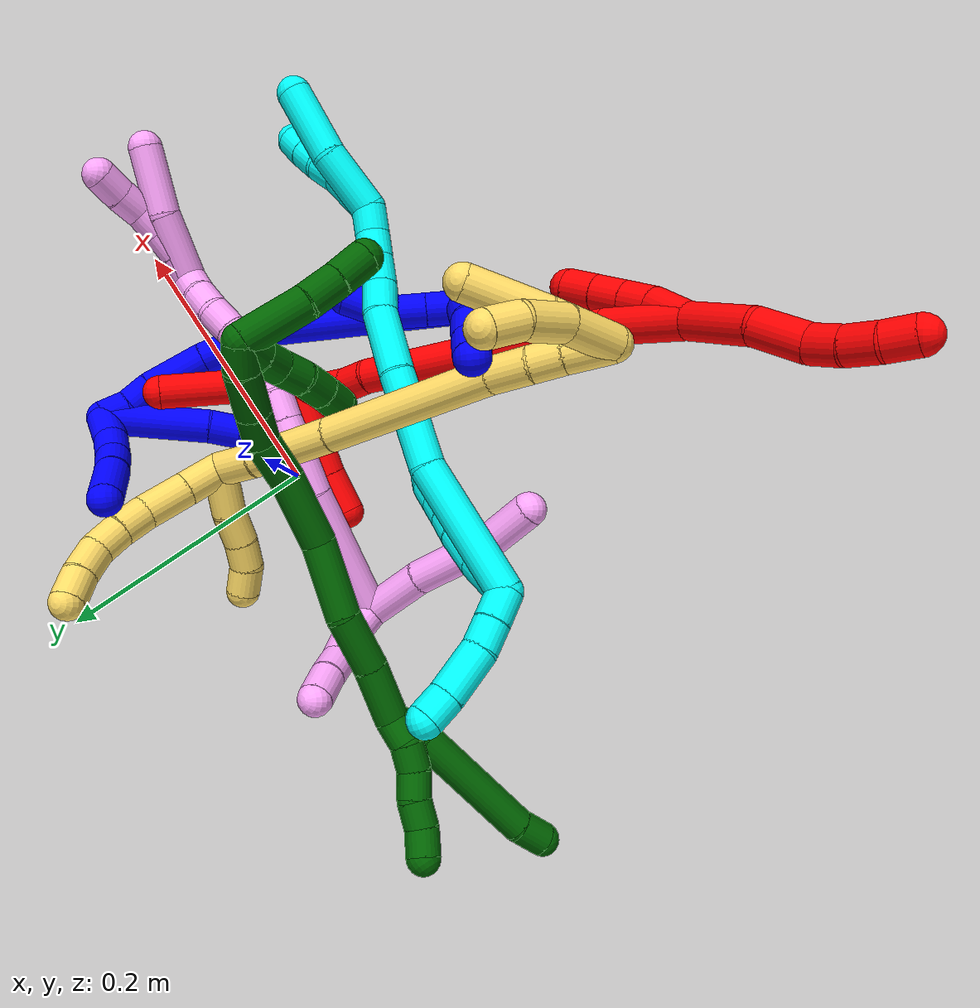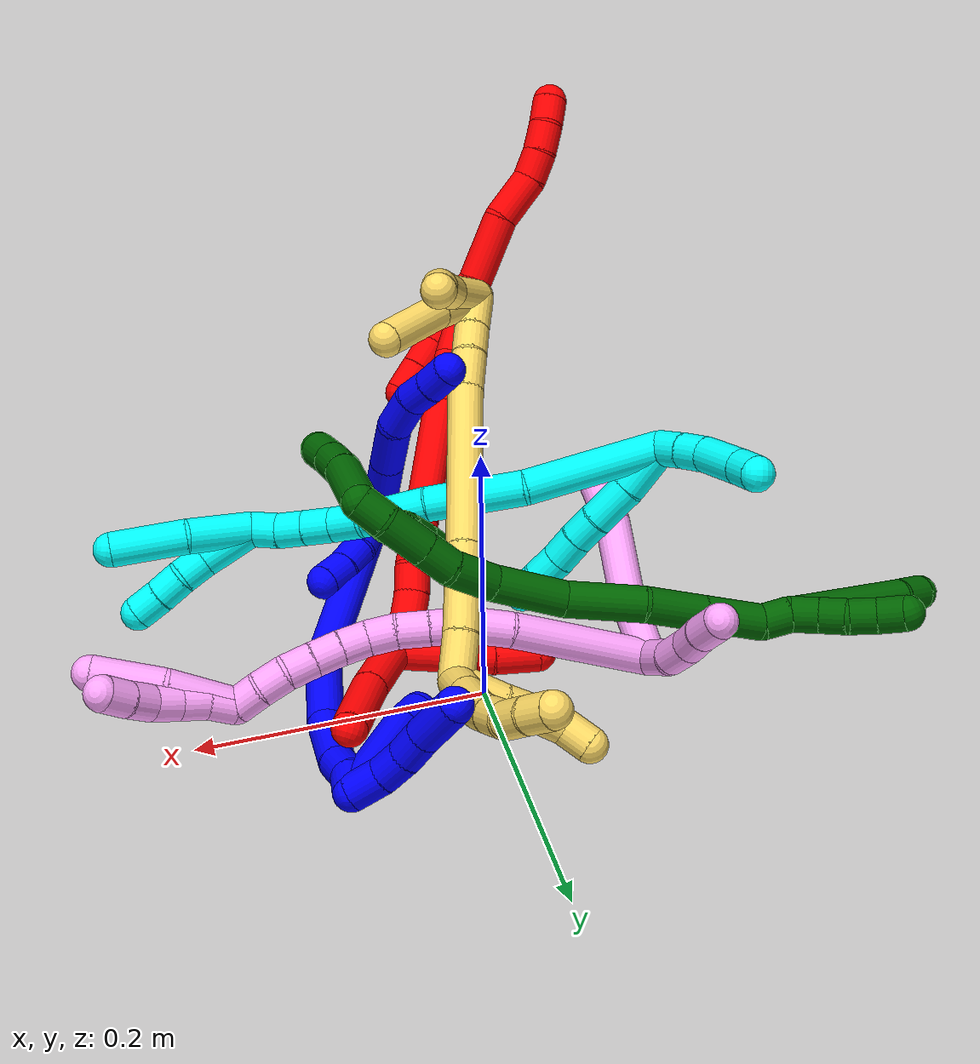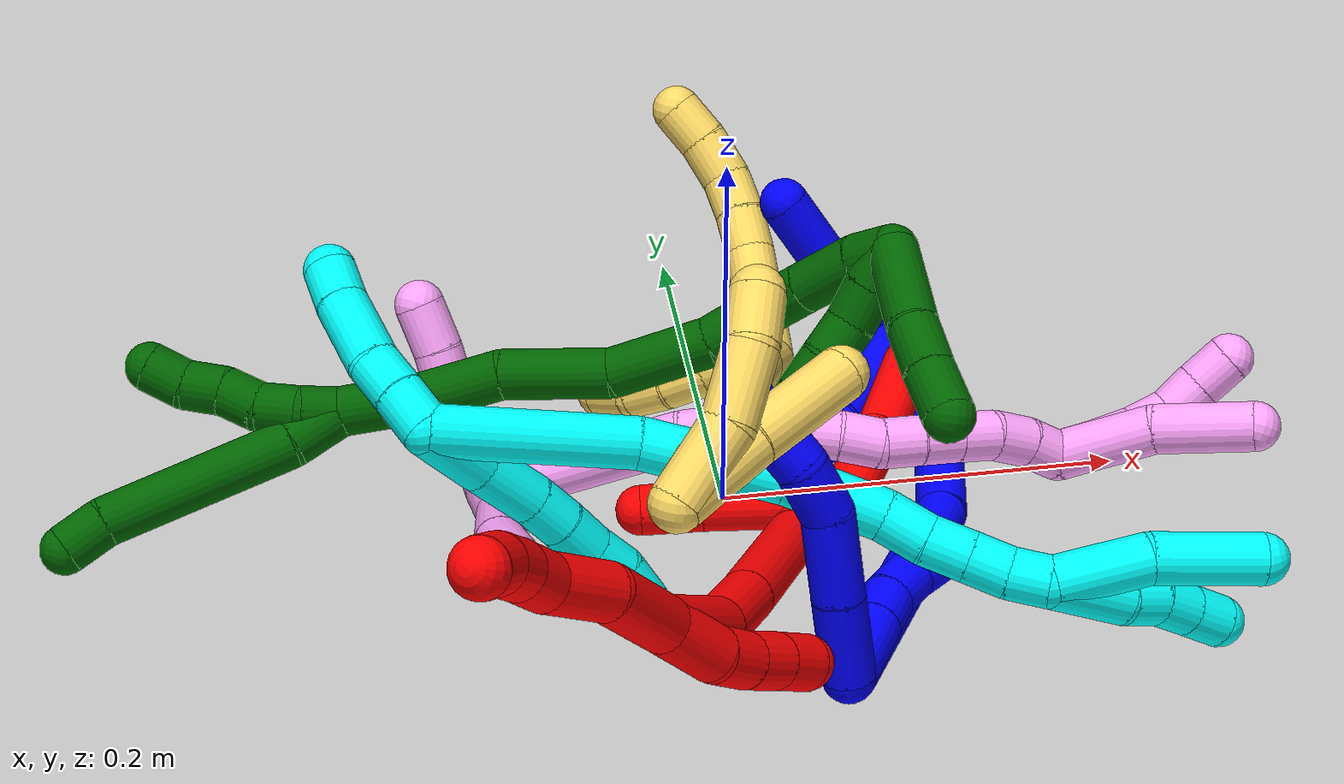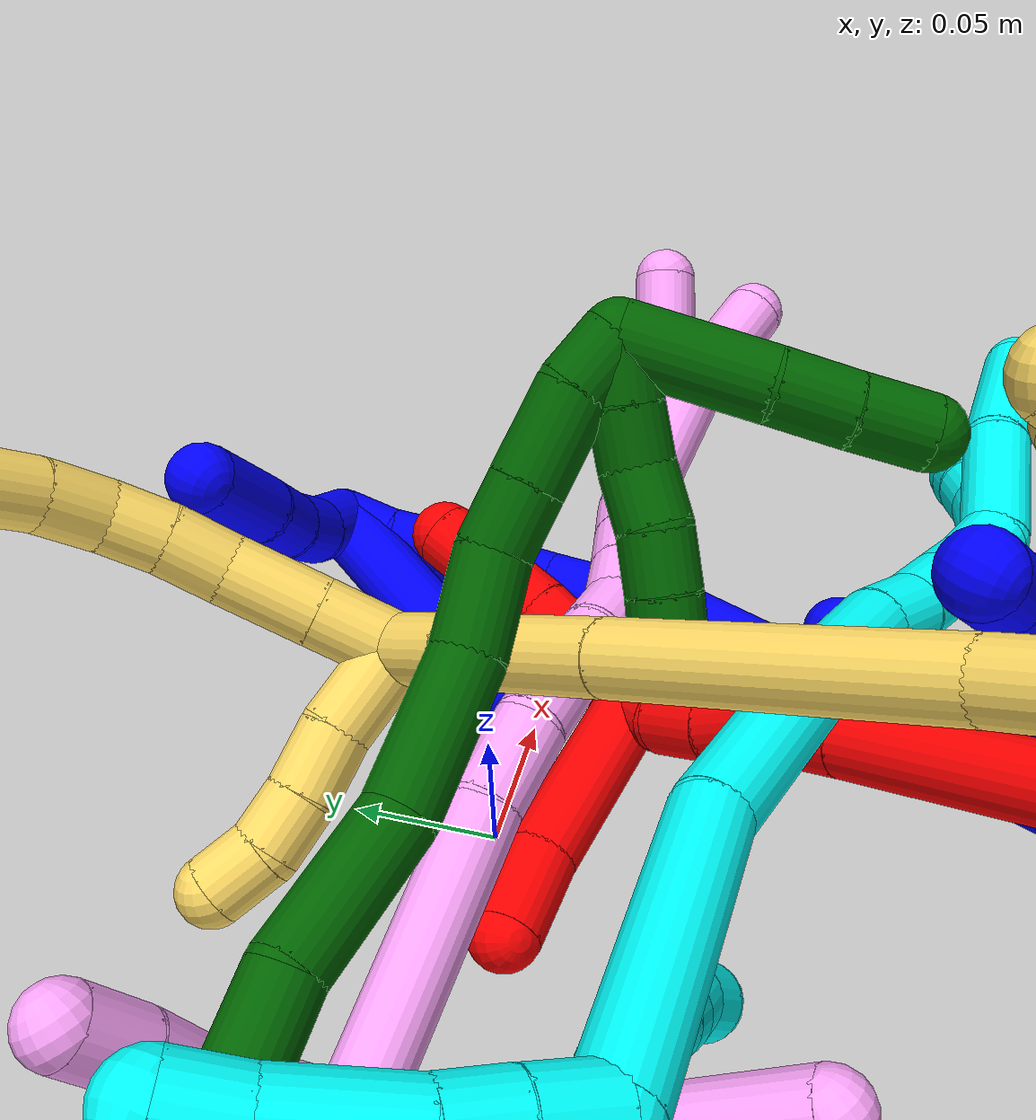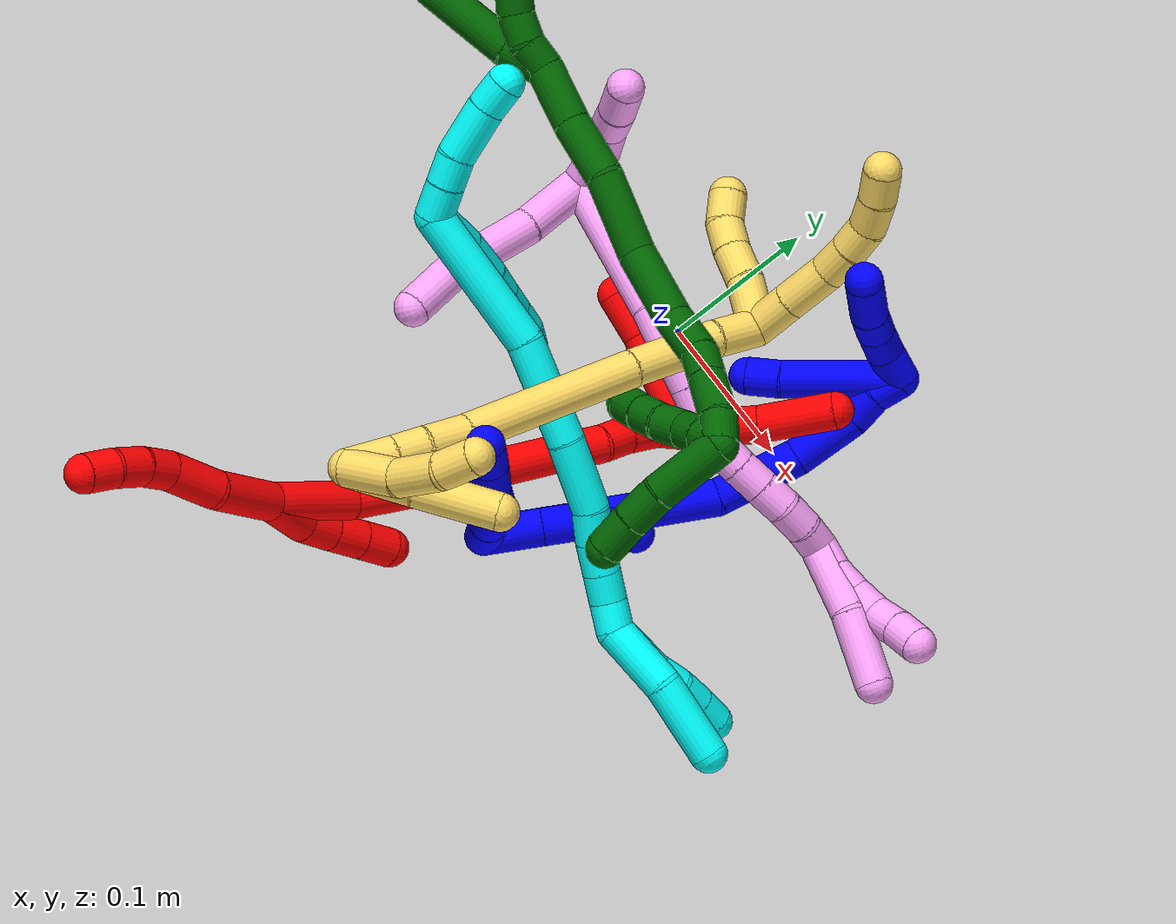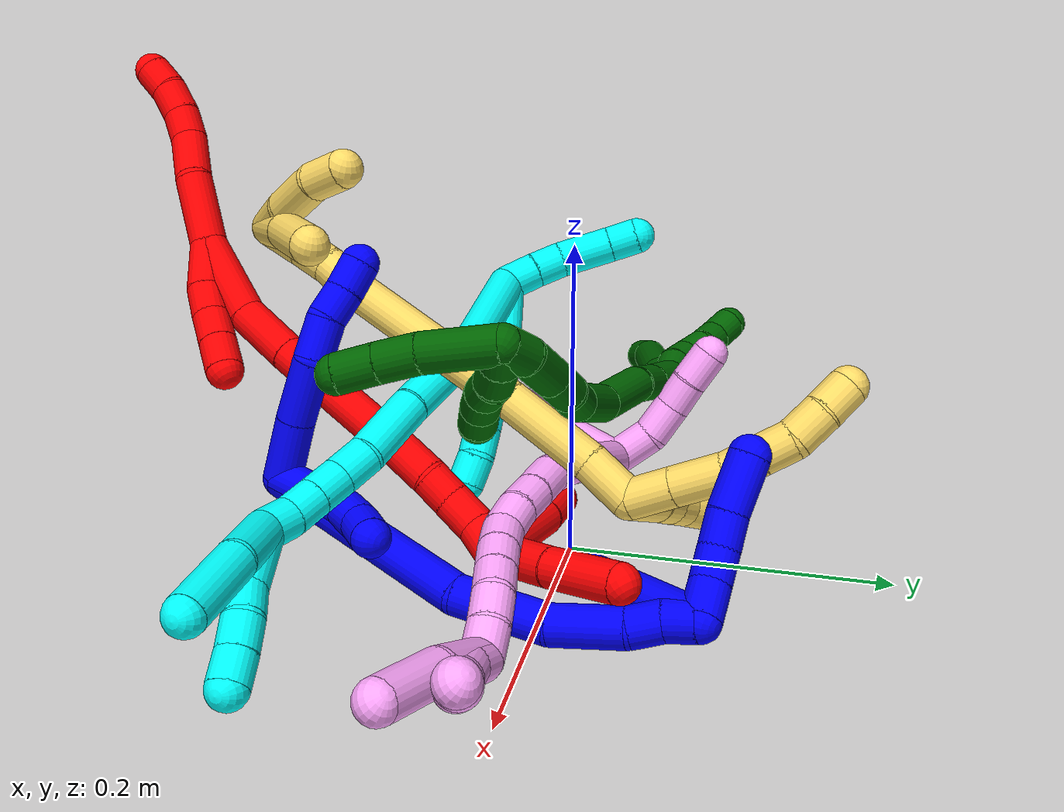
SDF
<sdf version="1.7">
 <world name="default">
  <plugin name="TubeGeneratorPlugin" filename="libtube_generator_plugin.so"/>
  <model name="photoneo_s_sensor">
   <static>1</static>
   <pose>0 0 2 1.57079 1.57079 3.14159</pose>
   <link name="link">
    <inertial><mass>0.1</mass></inertial>
    <sensor name="sensor" type="depth">
     <update_rate>30</update_rate>
     <camera>
      <horizontal_fov>1.22</horizontal_fov>
      <image><width>1920</width><height>1200</height><format>B8G8R8</format></image>
      <clip><near>0.1</near><far>4</far></clip>
      <depth_camera><output>points</output></depth_camera>
     </camera>
     <plugin name="camera_plugin" filename="libgazebo_ros_depth_camera.so">
      <baseline>0.2</baseline>
      <alwaysOn>1</alwaysOn>
      <updateRate>0.0</updateRate>
      <cameraName>camera_ir</cameraName>
      <imageTopicName>/camera/color/image_raw</imageTopicName>
      <cameraInfoTopicName>/camera/color/camera_info</cameraInfoTopicName>
      <depthImageTopicName>/camera/depth/image_raw</depthImageTopicName>
      <depthImageCameraInfoTopicName>/camera/depth/camera_info</depthImageCameraInfoTopicName>
      <pointCloudTopicName>/camera/depth/points</pointCloudTopicName>
      <frameName>fr_optical</frameName>
      <pointCloudCutoff>0.1</pointCloudCutoff>
      <pointCloudCutoffMax>2.0</pointCloudCutoffMax>
      <distortionK1>0</distortionK1>
      <distortionK2>0</distortionK2>
      <distortionK3>0</distortionK3>
      <distortionT1>0</distortionT1>
      <distortionT2>0</distortionT2>
      <CxPrime>0</CxPrime>
      <Cx>0</Cx>
      <Cy>0</Cy>
      <focalLength>0</focalLength>
      <hackBaseline>0</hackBaseline>
     </plugin>
    </sensor>
   </link>
  </model>
  <gravity>0 0 -9.8</gravity>
  <magnetic_field>6e-06 2.3e-05 -4.2e-05</magnetic_field>
  <atmosphere type="adiabatic"/>
  <physics name="default_physics" default="0" type="ode">
   <max_step_size>0.003</max_step_size>
   <real_time_factor>1</real_time_factor>
   <real_time_update_rate>1000</real_time_update_rate>
   <max_contacts>10000</max_contacts>
   <ode>
    <solver>
     <type>quick</type>
     <iters>100</iters>
     <sor>1.3</sor>
     <use_dynamic_moi_rescaling>0</use_dynamic_moi_rescaling>
    </solver>
    <constraints>
     <contact_max_correcting_vel>0</contact_max_correcting_vel>
     <contact_surface_layer>0.001</contact_surface_layer>
     <cfm>0</cfm>
     <erp>0.2</erp>
    </constraints>
   </ode>
  </physics>
  <scene><ambient>0.4 0.4 0.4 1</ambient><background>0.7 0.7 0.7 1</background><shadows>0</shadows></scene>
  <audio><device>default</device></audio>
  <spherical_coordinates>
   <surface_model>EARTH_WGS84</surface_model>
   <latitude_deg>0</latitude_deg>
   <longitude_deg>0</longitude_deg>
   <elevation>0</elevation>
   <heading_deg>0</heading_deg>
  </spherical_coordinates>
  <model name="bin">
   <static>1</static>
   <link name="bottom">
    <collision name="collision-bottom">
     <pose>0 0 -0.01 0 -0 0</pose>
     <geometry><box><size>0.8 0.6 0.02</size></box></geometry>
     <surface>
      <friction><ode><mu>100</mu><mu2>100</mu2></ode></friction>
      <contact><collide_bitmask>65535</collide_bitmask></contact>
     </surface>
    </collision>
   </link>
   <link name="west_wall">
    <collision name="collision-west_wall">
     <pose>-0.41 0 0.1 0 -0 0</pose>
     <geometry><box><size>0.02 0.6 0.2</size></box></geometry>
     <surface>
      <friction><ode><mu>100</mu><mu2>100</mu2></ode></friction>
      <contact><collide_bitmask>65535</collide_bitmask></contact>
     </surface>
    </collision>
   </link>
   <link name="east_wall">
    <collision name="collision-east_wall">
     <pose>0.41 0 0.1 0 -0 0</pose>
     <geometry><box><size>0.02 0.6 0.2</size></box></geometry>
     <surface>
      <friction><ode><mu>100</mu><mu2>100</mu2></ode></friction>
      <contact><collide_bitmask>65535</collide_bitmask></contact>
     </surface>
    </collision>
   </link>
   <link name="south_wall">
    <collision name="collision-south_wall">
     <pose>0 -0.31 0.1 0 -0 0</pose>
     <geometry><box><size>0.8 0.02 0.2</size></box></geometry>
     <surface>
      <friction><ode><mu>100</mu><mu2>100</mu2></ode></friction>
      <contact><collide_bitmask>65535</collide_bitmask></contact>
     </surface>
    </collision>
   </link>
   <link name="north_wall">
    <collision name="collision-north_wall">
     <pose>0 0.31 0.1 0 -0 0</pose>
     <geometry><box><size>0.8 0.02 0.2</size></box></geometry>
     <surface>
      <friction><ode><mu>100</mu><mu2>100</mu2></ode></friction>
      <contact><collide_bitmask>65535</collide_bitmask></contact>
     </surface>
    </collision>
   </link>
  </model>
  <model name="1">
   <static>0</static>
   <link name="1">
    <collision name="collision-cylinder-e_1_2_8">
     <pose>0.004787 -0.019817 -0.002743 1.70833 0.234888 0.269245</pose>
     <geometry><cylinder><radius>0.0125</radius><length>0.041141</length></cylinder></geometry>
     <surface>
      <friction><ode><mu>1.16</mu><mu2>1.16</mu2><slip1>0</slip1><slip2>0</slip2></ode></friction>
      <contact><ode><kp>1e+06</kp><kd>1</kd><max_vel>0</max_vel><min_depth>0.001</min_depth></ode></contact>
     </surface>
    </collision>
    <visual name="visual-cylinder-e_1_2_8">
     <pose>0.004787 -0.019817 -0.002743 1.70833 0.234888 0.269245</pose>
     <geometry><cylinder><radius>0.0125</radius><length>0.041141</length></cylinder></geometry>
     <material><ambient>0 0 1 1</ambient></material>
    </visual>
    <collision name="collision-cylinder-e_2_8_9">
     <pose>0.014733 -0.05925 -0.00943 1.7692 0.252291 0.307268</pose>
     <geometry><cylinder><radius>0.0125</radius><length>0.041328</length></cylinder></geometry>
     <surface>
      <friction><ode><mu>1.16</mu><mu2>1.16</mu2><slip1>0</slip1><slip2>0</slip2></ode></friction>
      <contact><ode><kp>1e+06</kp><kd>1</kd><max_vel>0</max_vel><min_depth>0.001</min_depth></ode></contact>
     </surface>
    </collision>
    <visual name="visual-cylinder-e_2_8_9">
     <pose>0.014733 -0.05925 -0.00943 1.7692 0.252291 0.307268</pose>
     <geometry><cylinder><radius>0.0125</radius><length>0.041328</length></cylinder></geometry>
     <material><ambient>0 0 1 1</ambient></material>
    </visual>
    <collision name="collision-cylinder-e_3_9_10">
     <pose>0.026624 -0.0906 -0.012927 1.53271 0.520671 0.502031</pose>
     <geometry><cylinder><radius>0.0125</radius><length>0.027069</length></cylinder></geometry>
     <surface>
      <friction><ode><mu>1.16</mu><mu2>1.16</mu2><slip1>0</slip1><slip2>0</slip2></ode></friction>
      <contact><ode><kp>1e+06</kp><kd>1</kd><max_vel>0</max_vel><min_depth>0.001</min_depth></ode></contact>
     </surface>
    </collision>
    <visual name="visual-cylinder-e_3_9_10">
     <pose>0.026624 -0.0906 -0.012927 1.53271 0.520671 0.502031</pose>
     <geometry><cylinder><radius>0.0125</radius><length>0.027069</length></cylinder></geometry>
     <material><ambient>0 0 1 1</ambient></material>
    </visual>
    <collision name="collision-cylinder-e_4_10_11">
     <pose>0.040709 -0.109262 -0.013082 1.65746 0.813072 0.877979</pose>
     <geometry><cylinder><radius>0.0125</radius><length>0.020241</length></cylinder></geometry>
     <surface>
      <friction><ode><mu>1.16</mu><mu2>1.16</mu2><slip1>0</slip1><slip2>0</slip2></ode></friction>
      <contact><ode><kp>1e+06</kp><kd>1</kd><max_vel>0</max_vel><min_depth>0.001</min_depth></ode></contact>
     </surface>
    </collision>
    <visual name="visual-cylinder-e_4_10_11">
     <pose>0.040709 -0.109262 -0.013082 1.65746 0.813072 0.877979</pose>
     <geometry><cylinder><radius>0.0125</radius><length>0.020241</length></cylinder></geometry>
     <material><ambient>0 0 1 1</ambient></material>
    </visual>
    <collision name="collision-cylinder-e_5_11_6">
     <pose>0.054942 -0.123596 -0.013895 1.59937 0.748619 0.768276</pose>
     <geometry><cylinder><radius>0.0125</radius><length>0.020221</length></cylinder></geometry>
     <surface>
      <friction><ode><mu>1.16</mu><mu2>1.16</mu2><slip1>0</slip1><slip2>0</slip2></ode></friction>
      <contact><ode><kp>1e+06</kp><kd>1</kd><max_vel>0</max_vel><min_depth>0.001</min_depth></ode></contact>
     </surface>
    </collision>
    <visual name="visual-cylinder-e_5_11_6">
     <pose>0.054942 -0.123596 -0.013895 1.59937 0.748619 0.768276</pose>
     <geometry><cylinder><radius>0.0125</radius><length>0.020221</length></cylinder></geometry>
     <material><ambient>0 0 1 1</ambient></material>
    </visual>
    <collision name="collision-cylinder-e_1_2_12">
     <pose>-0.000307 9.1e-05 -0.019431 -3.13691 -0.01582 2.56562</pose>
     <geometry><cylinder><radius>0.0125</radius><length>0.038868</length></cylinder></geometry>
     <surface>
      <friction><ode><mu>1.16</mu><mu2>1.16</mu2><slip1>0</slip1><slip2>0</slip2></ode></friction>
      <contact><ode><kp>1e+06</kp><kd>1</kd><max_vel>0</max_vel><min_depth>0.001</min_depth></ode></contact>
     </surface>
    </collision>
    <visual name="visual-cylinder-e_1_2_12">
     <pose>-0.000307 9.1e-05 -0.019431 -3.13691 -0.01582 2.56562</pose>
     <geometry><cylinder><radius>0.0125</radius><length>0.038868</length></cylinder></geometry>
     <material><ambient>0 0 1 1</ambient></material>
    </visual>
    <collision name="collision-cylinder-e_2_12_13">
     <pose>-0.000794 0.000221 -0.049072 -3.1378 -0.017573 2.71696</pose>
     <geometry><cylinder><radius>0.0125</radius><length>0.020422</length></cylinder></geometry>
     <surface>
      <friction><ode><mu>1.16</mu><mu2>1.16</mu2><slip1>0</slip1><slip2>0</slip2></ode></friction>
      <contact><ode><kp>1e+06</kp><kd>1</kd><max_vel>0</max_vel><min_depth>0.001</min_depth></ode></contact>
     </surface>
    </collision>
    <visual name="visual-cylinder-e_2_12_13">
     <pose>-0.000794 0.000221 -0.049072 -3.1378 -0.017573 2.71696</pose>
     <geometry><cylinder><radius>0.0125</radius><length>0.020422</length></cylinder></geometry>
     <material><ambient>0 0 1 1</ambient></material>
    </visual>
    <collision name="collision-cylinder-e_3_13_14">
     <pose>-0.00375 0.00043 -0.069183 -3.12437 -0.273331 3.01649</pose>
     <geometry><cylinder><radius>0.0125</radius><length>0.02057</length></cylinder></geometry>
     <surface>
      <friction><ode><mu>1.16</mu><mu2>1.16</mu2><slip1>0</slip1><slip2>0</slip2></ode></friction>
      <contact><ode><kp>1e+06</kp><kd>1</kd><max_vel>0</max_vel><min_depth>0.001</min_depth></ode></contact>
     </surface>
    </collision>
    <visual name="visual-cylinder-e_3_13_14">
     <pose>-0.00375 0.00043 -0.069183 -3.12437 -0.273331 3.01649</pose>
     <geometry><cylinder><radius>0.0125</radius><length>0.02057</length></cylinder></geometry>
     <material><ambient>0 0 1 1</ambient></material>
    </visual>
    <collision name="collision-cylinder-e_4_14_5">
     <pose>-0.010887 0.000157 -0.088151 3.09272 -0.447817 -2.92773</pose>
     <geometry><cylinder><radius>0.0125</radius><length>0.02014</length></cylinder></geometry>
     <surface>
      <friction><ode><mu>1.16</mu><mu2>1.16</mu2><slip1>0</slip1><slip2>0</slip2></ode></friction>
      <contact><ode><kp>1e+06</kp><kd>1</kd><max_vel>0</max_vel><min_depth>0.001</min_depth></ode></contact>
     </surface>
    </collision>
    <visual name="visual-cylinder-e_4_14_5">
     <pose>-0.010887 0.000157 -0.088151 3.09272 -0.447817 -2.92773</pose>
     <geometry><cylinder><radius>0.0125</radius><length>0.02014</length></cylinder></geometry>
     <material><ambient>0 0 1 1</ambient></material>
    </visual>
    <collision name="collision-cylinder-e_1_2_15">
     <pose>-0.001105 0.010851 -0.077009 -3.00161 -0.014209 0.201999</pose>
     <geometry><cylinder><radius>0.0125</radius><length>0.155556</length></cylinder></geometry>
     <surface>
      <friction><ode><mu>1.16</mu><mu2>1.16</mu2><slip1>0</slip1><slip2>0</slip2></ode></friction>
      <contact><ode><kp>1e+06</kp><kd>1</kd><max_vel>0</max_vel><min_depth>0.001</min_depth></ode></contact>
     </surface>
    </collision>
    <visual name="visual-cylinder-e_1_2_15">
     <pose>-0.001105 0.010851 -0.077009 -3.00161 -0.014209 0.201999</pose>
     <geometry><cylinder><radius>0.0125</radius><length>0.155556</length></cylinder></geometry>
     <material><ambient>0 0 1 1</ambient></material>
    </visual>
    <collision name="collision-cylinder-e_2_15_16">
     <pose>0.006124 0.024067 -0.181828 -3.05674 0.290176 -2.57608</pose>
     <geometry><cylinder><radius>0.0125</radius><length>0.058255</length></cylinder></geometry>
     <surface>
      <friction><ode><mu>1.16</mu><mu2>1.16</mu2><slip1>0</slip1><slip2>0</slip2></ode></friction>
      <contact><ode><kp>1e+06</kp><kd>1</kd><max_vel>0</max_vel><min_depth>0.001</min_depth></ode></contact>
     </surface>
    </collision>
    <visual name="visual-cylinder-e_2_15_16">
     <pose>0.006124 0.024067 -0.181828 -3.05674 0.290176 -2.57608</pose>
     <geometry><cylinder><radius>0.0125</radius><length>0.058255</length></cylinder></geometry>
     <material><ambient>0 0 1 1</ambient></material>
    </visual>
    <collision name="collision-cylinder-e_3_16_17">
     <pose>0.024255 0.023598 -0.229782 3.00184 0.44884 2.54655</pose>
     <geometry><cylinder><radius>0.0125</radius><length>0.045157</length></cylinder></geometry>
     <surface>
      <friction><ode><mu>1.16</mu><mu2>1.16</mu2><slip1>0</slip1><slip2>0</slip2></ode></friction>
      <contact><ode><kp>1e+06</kp><kd>1</kd><max_vel>0</max_vel><min_depth>0.001</min_depth></ode></contact>
     </surface>
    </collision>
    <visual name="visual-cylinder-e_3_16_17">
     <pose>0.024255 0.023598 -0.229782 3.00184 0.44884 2.54655</pose>
     <geometry><cylinder><radius>0.0125</radius><length>0.045157</length></cylinder></geometry>
     <material><ambient>0 0 1 1</ambient></material>
    </visual>
    <collision name="collision-cylinder-e_4_17_18">
     <pose>0.040412 0.018136 -0.257835 2.82074 0.651822 2.24849</pose>
     <geometry><cylinder><radius>0.0125</radius><length>0.020968</length></cylinder></geometry>
     <surface>
      <friction><ode><mu>1.16</mu><mu2>1.16</mu2><slip1>0</slip1><slip2>0</slip2></ode></friction>
      <contact><ode><kp>1e+06</kp><kd>1</kd><max_vel>0</max_vel><min_depth>0.001</min_depth></ode></contact>
     </surface>
    </collision>
    <visual name="visual-cylinder-e_4_17_18">
     <pose>0.040412 0.018136 -0.257835 2.82074 0.651822 2.24849</pose>
     <geometry><cylinder><radius>0.0125</radius><length>0.020968</length></cylinder></geometry>
     <material><ambient>0 0 1 1</ambient></material>
    </visual>
    <collision name="collision-cylinder-e_5_18_1">
     <pose>0.050272 0.013602 -0.27495 2.93747 0.356379 2.10745</pose>
     <geometry><cylinder><radius>0.0125</radius><length>0.020064</length></cylinder></geometry>
     <surface>
      <friction><ode><mu>1.16</mu><mu2>1.16</mu2><slip1>0</slip1><slip2>0</slip2></ode></friction>
      <contact><ode><kp>1e+06</kp><kd>1</kd><max_vel>0</max_vel><min_depth>0.001</min_depth></ode></contact>
     </surface>
    </collision>
    <visual name="visual-cylinder-e_5_18_1">
     <pose>0.050272 0.013602 -0.27495 2.93747 0.356379 2.10745</pose>
     <geometry><cylinder><radius>0.0125</radius><length>0.020064</length></cylinder></geometry>
     <material><ambient>0 0 1 1</ambient></material>
    </visual>
    <collision name="collision-cylinder-e_1_1_19">
     <pose>0.06022 0.01659 -0.246116 -0.127956 0.166563 -0.010696</pose>
     <geometry><cylinder><radius>0.0125</radius><length>0.077786</length></cylinder></geometry>
     <surface>
      <friction><ode><mu>1.16</mu><mu2>1.16</mu2><slip1>0</slip1><slip2>0</slip2></ode></friction>
      <contact><ode><kp>1e+06</kp><kd>1</kd><max_vel>0</max_vel><min_depth>0.001</min_depth></ode></contact>
     </surface>
    </collision>
    <visual name="visual-cylinder-e_1_1_19">
     <pose>0.06022 0.01659 -0.246116 -0.127956 0.166563 -0.010696</pose>
     <geometry><cylinder><radius>0.0125</radius><length>0.077786</length></cylinder></geometry>
     <material><ambient>0 0 1 1</ambient></material>
    </visual>
    <collision name="collision-cylinder-e_2_19_4">
     <pose>0.069533 0.024036 -0.197651 -0.240078 0.260831 -0.031638</pose>
     <geometry><cylinder><radius>0.0125</radius><length>0.022214</length></cylinder></geometry>
     <surface>
      <friction><ode><mu>1.16</mu><mu2>1.16</mu2><slip1>0</slip1><slip2>0</slip2></ode></friction>
      <contact><ode><kp>1e+06</kp><kd>1</kd><max_vel>0</max_vel><min_depth>0.001</min_depth></ode></contact>
     </surface>
    </collision>
    <visual name="visual-cylinder-e_2_19_4">
     <pose>0.069533 0.024036 -0.197651 -0.240078 0.260831 -0.031638</pose>
     <geometry><cylinder><radius>0.0125</radius><length>0.022214</length></cylinder></geometry>
     <material><ambient>0 0 1 1</ambient></material>
    </visual>
    <collision name="collision-cylinder-e_1_1_20">
     <pose>0.063409 0.005975 -0.280466 0.997913 0.955742 0.550156</pose>
     <geometry><cylinder><radius>0.0125</radius><length>0.023599</length></cylinder></geometry>
     <surface>
      <friction><ode><mu>1.16</mu><mu2>1.16</mu2><slip1>0</slip1><slip2>0</slip2></ode></friction>
      <contact><ode><kp>1e+06</kp><kd>1</kd><max_vel>0</max_vel><min_depth>0.001</min_depth></ode></contact>
     </surface>
    </collision>
    <visual name="visual-cylinder-e_1_1_20">
     <pose>0.063409 0.005975 -0.280466 0.997913 0.955742 0.550156</pose>
     <geometry><cylinder><radius>0.0125</radius><length>0.023599</length></cylinder></geometry>
     <material><ambient>0 0 1 1</ambient></material>
    </visual>
    <collision name="collision-cylinder-e_2_20_21">
     <pose>0.080239 -0.006958 -0.274491 1.26404 0.760187 0.569185</pose>
     <geometry><cylinder><radius>0.0125</radius><length>0.020876</length></cylinder></geometry>
     <surface>
      <friction><ode><mu>1.16</mu><mu2>1.16</mu2><slip1>0</slip1><slip2>0</slip2></ode></friction>
      <contact><ode><kp>1e+06</kp><kd>1</kd><max_vel>0</max_vel><min_depth>0.001</min_depth></ode></contact>
     </surface>
    </collision>
    <visual name="visual-cylinder-e_2_20_21">
     <pose>0.080239 -0.006958 -0.274491 1.26404 0.760187 0.569185</pose>
     <geometry><cylinder><radius>0.0125</radius><length>0.020876</length></cylinder></geometry>
     <material><ambient>0 0 1 1</ambient></material>
    </visual>
    <collision name="collision-cylinder-e_3_21_22">
     <pose>0.093502 -0.022529 -0.270614 1.38246 0.61965 0.517872</pose>
     <geometry><cylinder><radius>0.0125</radius><length>0.020907</length></cylinder></geometry>
     <surface>
      <friction><ode><mu>1.16</mu><mu2>1.16</mu2><slip1>0</slip1><slip2>0</slip2></ode></friction>
      <contact><ode><kp>1e+06</kp><kd>1</kd><max_vel>0</max_vel><min_depth>0.001</min_depth></ode></contact>
     </surface>
    </collision>
    <visual name="visual-cylinder-e_3_21_22">
     <pose>0.093502 -0.022529 -0.270614 1.38246 0.61965 0.517872</pose>
     <geometry><cylinder><radius>0.0125</radius><length>0.020907</length></cylinder></geometry>
     <material><ambient>0 0 1 1</ambient></material>
    </visual>
    <collision name="collision-cylinder-e_4_22_3">
     <pose>0.110248 -0.044499 -0.26838 1.52378 0.664577 0.636102</pose>
     <geometry><cylinder><radius>0.0125</radius><length>0.034618</length></cylinder></geometry>
     <surface>
      <friction><ode><mu>1.16</mu><mu2>1.16</mu2><slip1>0</slip1><slip2>0</slip2></ode></friction>
      <contact><ode><kp>1e+06</kp><kd>1</kd><max_vel>0</max_vel><min_depth>0.001</min_depth></ode></contact>
     </surface>
    </collision>
    <visual name="visual-cylinder-e_4_22_3">
     <pose>0.110248 -0.044499 -0.26838 1.52378 0.664577 0.636102</pose>
     <geometry><cylinder><radius>0.0125</radius><length>0.034618</length></cylinder></geometry>
     <material><ambient>0 0 1 1</ambient></material>
    </visual>
    <collision name="collision-sphere-3">
     <pose>0.120923 -0.058109 -0.26774 0 -0 0</pose>
     <geometry><sphere><radius>0.0125</radius></sphere></geometry>
     <surface>
      <friction><ode><mu>1.16</mu><mu2>1.16</mu2><slip1>0</slip1><slip2>0</slip2></ode></friction>
      <contact><ode><kp>1e+06</kp><kd>1</kd><max_vel>0</max_vel><min_depth>0.001</min_depth></ode></contact>
     </surface>
    </collision>
    <visual name="visual-sphere-3">
     <pose>0.120923 -0.058109 -0.26774 0 -0 0</pose>
     <geometry><sphere><radius>0.0125</radius></sphere></geometry>
     <material><ambient>0 0 1 1</ambient></material>
    </visual>
    <collision name="collision-sphere-22">
     <pose>0.099573 -0.030888 -0.269021 0 -0 0</pose>
     <geometry><sphere><radius>0.0125</radius></sphere></geometry>
     <surface>
      <friction><ode><mu>1.16</mu><mu2>1.16</mu2><slip1>0</slip1><slip2>0</slip2></ode></friction>
      <contact><ode><kp>1e+06</kp><kd>1</kd><max_vel>0</max_vel><min_depth>0.001</min_depth></ode></contact>
     </surface>
    </collision>
    <visual name="visual-sphere-22">
     <pose>0.099573 -0.030888 -0.269021 0 -0 0</pose>
     <geometry><sphere><radius>0.0125</radius></sphere></geometry>
     <material><ambient>0 0 1 1</ambient></material>
    </visual>
    <collision name="collision-sphere-21">
     <pose>0.087431 -0.014169 -0.272207 0 -0 0</pose>
     <geometry><sphere><radius>0.0125</radius></sphere></geometry>
     <surface>
      <friction><ode><mu>1.16</mu><mu2>1.16</mu2><slip1>0</slip1><slip2>0</slip2></ode></friction>
      <contact><ode><kp>1e+06</kp><kd>1</kd><max_vel>0</max_vel><min_depth>0.001</min_depth></ode></contact>
     </surface>
    </collision>
    <visual name="visual-sphere-21">
     <pose>0.087431 -0.014169 -0.272207 0 -0 0</pose>
     <geometry><sphere><radius>0.0125</radius></sphere></geometry>
     <material><ambient>0 0 1 1</ambient></material>
    </visual>
    <collision name="collision-sphere-20">
     <pose>0.073046 0.000254 -0.276776 0 -0 0</pose>
     <geometry><sphere><radius>0.0125</radius></sphere></geometry>
     <surface>
      <friction><ode><mu>1.16</mu><mu2>1.16</mu2><slip1>0</slip1><slip2>0</slip2></ode></friction>
      <contact><ode><kp>1e+06</kp><kd>1</kd><max_vel>0</max_vel><min_depth>0.001</min_depth></ode></contact>
     </surface>
    </collision>
    <visual name="visual-sphere-20">
     <pose>0.073046 0.000254 -0.276776 0 -0 0</pose>
     <geometry><sphere><radius>0.0125</radius></sphere></geometry>
     <material><ambient>0 0 1 1</ambient></material>
    </visual>
    <collision name="collision-sphere-4">
     <pose>0.072397 0.026588 -0.187227 0 -0 0</pose>
     <geometry><sphere><radius>0.0125</radius></sphere></geometry>
     <surface>
      <friction><ode><mu>1.16</mu><mu2>1.16</mu2><slip1>0</slip1><slip2>0</slip2></ode></friction>
      <contact><ode><kp>1e+06</kp><kd>1</kd><max_vel>0</max_vel><min_depth>0.001</min_depth></ode></contact>
     </surface>
    </collision>
    <visual name="visual-sphere-4">
     <pose>0.072397 0.026588 -0.187227 0 -0 0</pose>
     <geometry><sphere><radius>0.0125</radius></sphere></geometry>
     <material><ambient>0 0 1 1</ambient></material>
    </visual>
    <collision name="collision-sphere-6">
     <pose>0.061823 -0.131 -0.014107 0 -0 0</pose>
     <geometry><sphere><radius>0.0125</radius></sphere></geometry>
     <surface>
      <friction><ode><mu>1.16</mu><mu2>1.16</mu2><slip1>0</slip1><slip2>0</slip2></ode></friction>
      <contact><ode><kp>1e+06</kp><kd>1</kd><max_vel>0</max_vel><min_depth>0.001</min_depth></ode></contact>
     </surface>
    </collision>
    <visual name="visual-sphere-6">
     <pose>0.061823 -0.131 -0.014107 0 -0 0</pose>
     <geometry><sphere><radius>0.0125</radius></sphere></geometry>
     <material><ambient>0 0 1 1</ambient></material>
    </visual>
    <collision name="collision-sphere-11">
     <pose>0.04806 -0.116192 -0.013684 0 -0 0</pose>
     <geometry><sphere><radius>0.0125</radius></sphere></geometry>
     <surface>
      <friction><ode><mu>1.16</mu><mu2>1.16</mu2><slip1>0</slip1><slip2>0</slip2></ode></friction>
      <contact><ode><kp>1e+06</kp><kd>1</kd><max_vel>0</max_vel><min_depth>0.001</min_depth></ode></contact>
     </surface>
    </collision>
    <visual name="visual-sphere-11">
     <pose>0.04806 -0.116192 -0.013684 0 -0 0</pose>
     <geometry><sphere><radius>0.0125</radius></sphere></geometry>
     <material><ambient>0 0 1 1</ambient></material>
    </visual>
    <collision name="collision-sphere-10">
     <pose>0.033357 -0.102333 -0.01248 0 -0 0</pose>
     <geometry><sphere><radius>0.0125</radius></sphere></geometry>
     <surface>
      <friction><ode><mu>1.16</mu><mu2>1.16</mu2><slip1>0</slip1><slip2>0</slip2></ode></friction>
      <contact><ode><kp>1e+06</kp><kd>1</kd><max_vel>0</max_vel><min_depth>0.001</min_depth></ode></contact>
     </surface>
    </collision>
    <visual name="visual-sphere-10">
     <pose>0.033357 -0.102333 -0.01248 0 -0 0</pose>
     <geometry><sphere><radius>0.0125</radius></sphere></geometry>
     <material><ambient>0 0 1 1</ambient></material>
    </visual>
    <collision name="collision-sphere-9">
     <pose>0.019891 -0.078868 -0.013374 0 -0 0</pose>
     <geometry><sphere><radius>0.0125</radius></sphere></geometry>
     <surface>
      <friction><ode><mu>1.16</mu><mu2>1.16</mu2><slip1>0</slip1><slip2>0</slip2></ode></friction>
      <contact><ode><kp>1e+06</kp><kd>1</kd><max_vel>0</max_vel><min_depth>0.001</min_depth></ode></contact>
     </surface>
    </collision>
    <visual name="visual-sphere-9">
     <pose>0.019891 -0.078868 -0.013374 0 -0 0</pose>
     <geometry><sphere><radius>0.0125</radius></sphere></geometry>
     <material><ambient>0 0 1 1</ambient></material>
    </visual>
    <collision name="collision-sphere-2">
     <geometry><sphere><radius>0.0125</radius></sphere></geometry>
     <surface>
      <friction><ode><mu>1.16</mu><mu2>1.16</mu2><slip1>0</slip1><slip2>0</slip2></ode></friction>
      <contact><ode><kp>1e+06</kp><kd>1</kd><max_vel>0</max_vel><min_depth>0.001</min_depth></ode></contact>
     </surface>
    </collision>
    <visual name="visual-sphere-2">
     <geometry><sphere><radius>0.0125</radius></sphere></geometry>
     <material><ambient>0 0 1 1</ambient></material>
    </visual>
    <collision name="collision-sphere-19">
     <pose>0.066669 0.021485 -0.208075 0 -0 0</pose>
     <geometry><sphere><radius>0.0125</radius></sphere></geometry>
     <surface>
      <friction><ode><mu>1.16</mu><mu2>1.16</mu2><slip1>0</slip1><slip2>0</slip2></ode></friction>
      <contact><ode><kp>1e+06</kp><kd>1</kd><max_vel>0</max_vel><min_depth>0.001</min_depth></ode></contact>
     </surface>
    </collision>
    <visual name="visual-sphere-19">
     <pose>0.066669 0.021485 -0.208075 0 -0 0</pose>
     <geometry><sphere><radius>0.0125</radius></sphere></geometry>
     <material><ambient>0 0 1 1</ambient></material>
    </visual>
    <collision name="collision-sphere-8">
     <pose>0.009575 -0.039633 -0.005485 0 -0 0</pose>
     <geometry><sphere><radius>0.0125</radius></sphere></geometry>
     <surface>
      <friction><ode><mu>1.16</mu><mu2>1.16</mu2><slip1>0</slip1><slip2>0</slip2></ode></friction>
      <contact><ode><kp>1e+06</kp><kd>1</kd><max_vel>0</max_vel><min_depth>0.001</min_depth></ode></contact>
     </surface>
    </collision>
    <visual name="visual-sphere-8">
     <pose>0.009575 -0.039633 -0.005485 0 -0 0</pose>
     <geometry><sphere><radius>0.0125</radius></sphere></geometry>
     <material><ambient>0 0 1 1</ambient></material>
    </visual>
    <collision name="collision-sphere-12">
     <pose>-0.000615 0.000182 -0.038862 0 -0 0</pose>
     <geometry><sphere><radius>0.0125</radius></sphere></geometry>
     <surface>
      <friction><ode><mu>1.16</mu><mu2>1.16</mu2><slip1>0</slip1><slip2>0</slip2></ode></friction>
      <contact><ode><kp>1e+06</kp><kd>1</kd><max_vel>0</max_vel><min_depth>0.001</min_depth></ode></contact>
     </surface>
    </collision>
    <visual name="visual-sphere-12">
     <pose>-0.000615 0.000182 -0.038862 0 -0 0</pose>
     <geometry><sphere><radius>0.0125</radius></sphere></geometry>
     <material><ambient>0 0 1 1</ambient></material>
    </visual>
    <collision name="collision-sphere-13">
     <pose>-0.000974 0.000259 -0.059281 0 -0 0</pose>
     <geometry><sphere><radius>0.0125</radius></sphere></geometry>
     <surface>
      <friction><ode><mu>1.16</mu><mu2>1.16</mu2><slip1>0</slip1><slip2>0</slip2></ode></friction>
      <contact><ode><kp>1e+06</kp><kd>1</kd><max_vel>0</max_vel><min_depth>0.001</min_depth></ode></contact>
     </surface>
    </collision>
    <visual name="visual-sphere-13">
     <pose>-0.000974 0.000259 -0.059281 0 -0 0</pose>
     <geometry><sphere><radius>0.0125</radius></sphere></geometry>
     <material><ambient>0 0 1 1</ambient></material>
    </visual>
    <collision name="collision-sphere-14">
     <pose>-0.006526 0.000601 -0.079085 0 -0 0</pose>
     <geometry><sphere><radius>0.0125</radius></sphere></geometry>
     <surface>
      <friction><ode><mu>1.16</mu><mu2>1.16</mu2><slip1>0</slip1><slip2>0</slip2></ode></friction>
      <contact><ode><kp>1e+06</kp><kd>1</kd><max_vel>0</max_vel><min_depth>0.001</min_depth></ode></contact>
     </surface>
    </collision>
    <visual name="visual-sphere-14">
     <pose>-0.006526 0.000601 -0.079085 0 -0 0</pose>
     <geometry><sphere><radius>0.0125</radius></sphere></geometry>
     <material><ambient>0 0 1 1</ambient></material>
    </visual>
    <collision name="collision-sphere-5">
     <pose>-0.015247 -0.000286 -0.097217 0 -0 0</pose>
     <geometry><sphere><radius>0.0125</radius></sphere></geometry>
     <surface>
      <friction><ode><mu>1.16</mu><mu2>1.16</mu2><slip1>0</slip1><slip2>0</slip2></ode></friction>
      <contact><ode><kp>1e+06</kp><kd>1</kd><max_vel>0</max_vel><min_depth>0.001</min_depth></ode></contact>
     </surface>
    </collision>
    <visual name="visual-sphere-5">
     <pose>-0.015247 -0.000286 -0.097217 0 -0 0</pose>
     <geometry><sphere><radius>0.0125</radius></sphere></geometry>
     <material><ambient>0 0 1 1</ambient></material>
    </visual>
    <collision name="collision-sphere-15">
     <pose>-0.00221 0.021701 -0.154019 0 -0 0</pose>
     <geometry><sphere><radius>0.0125</radius></sphere></geometry>
     <surface>
      <friction><ode><mu>1.16</mu><mu2>1.16</mu2><slip1>0</slip1><slip2>0</slip2></ode></friction>
      <contact><ode><kp>1e+06</kp><kd>1</kd><max_vel>0</max_vel><min_depth>0.001</min_depth></ode></contact>
     </surface>
    </collision>
    <visual name="visual-sphere-15">
     <pose>-0.00221 0.021701 -0.154019 0 -0 0</pose>
     <geometry><sphere><radius>0.0125</radius></sphere></geometry>
     <material><ambient>0 0 1 1</ambient></material>
    </visual>
    <collision name="collision-sphere-16">
     <pose>0.014458 0.026432 -0.209638 0 -0 0</pose>
     <geometry><sphere><radius>0.0125</radius></sphere></geometry>
     <surface>
      <friction><ode><mu>1.16</mu><mu2>1.16</mu2><slip1>0</slip1><slip2>0</slip2></ode></friction>
      <contact><ode><kp>1e+06</kp><kd>1</kd><max_vel>0</max_vel><min_depth>0.001</min_depth></ode></contact>
     </surface>
    </collision>
    <visual name="visual-sphere-16">
     <pose>0.014458 0.026432 -0.209638 0 -0 0</pose>
     <geometry><sphere><radius>0.0125</radius></sphere></geometry>
     <material><ambient>0 0 1 1</ambient></material>
    </visual>
    <collision name="collision-sphere-17">
     <pose>0.034052 0.020765 -0.249925 0 -0 0</pose>
     <geometry><sphere><radius>0.0125</radius></sphere></geometry>
     <surface>
      <friction><ode><mu>1.16</mu><mu2>1.16</mu2><slip1>0</slip1><slip2>0</slip2></ode></friction>
      <contact><ode><kp>1e+06</kp><kd>1</kd><max_vel>0</max_vel><min_depth>0.001</min_depth></ode></contact>
     </surface>
    </collision>
    <visual name="visual-sphere-17">
     <pose>0.034052 0.020765 -0.249925 0 -0 0</pose>
     <geometry><sphere><radius>0.0125</radius></sphere></geometry>
     <material><ambient>0 0 1 1</ambient></material>
    </visual>
    <collision name="collision-sphere-18">
     <pose>0.046772 0.015508 -0.265744 0 -0 0</pose>
     <geometry><sphere><radius>0.0125</radius></sphere></geometry>
     <surface>
      <friction><ode><mu>1.16</mu><mu2>1.16</mu2><slip1>0</slip1><slip2>0</slip2></ode></friction>
      <contact><ode><kp>1e+06</kp><kd>1</kd><max_vel>0</max_vel><min_depth>0.001</min_depth></ode></contact>
     </surface>
    </collision>
    <visual name="visual-sphere-18">
     <pose>0.046772 0.015508 -0.265744 0 -0 0</pose>
     <geometry><sphere><radius>0.0125</radius></sphere></geometry>
     <material><ambient>0 0 1 1</ambient></material>
    </visual>
    <collision name="collision-sphere-1">
     <pose>0.053772 0.011696 -0.284157 0 -0 0</pose>
     <geometry><sphere><radius>0.0125</radius></sphere></geometry>
     <surface>
      <friction><ode><mu>1.16</mu><mu2>1.16</mu2><slip1>0</slip1><slip2>0</slip2></ode></friction>
      <contact><ode><kp>1e+06</kp><kd>1</kd><max_vel>0</max_vel><min_depth>0.001</min_depth></ode></contact>
     </surface>
    </collision>
    <visual name="visual-sphere-1">
     <pose>0.053772 0.011696 -0.284157 0 -0 0</pose>
     <geometry><sphere><radius>0.0125</radius></sphere></geometry>
     <material><ambient>0 0 1 1</ambient></material>
    </visual>
    <inertial>
     <pose>0.028593 -0.00772 -0.134743 0 -0 0</pose>
     <mass>0.75</mass>
     <inertia>
      <ixx>0.000437</ixx>
      <ixy>0</ixy>
      <ixz>0</ixz>
      <iyy>-0.000162</iyy>
      <iyz>0</iyz>
      <izz>-7.3e-05</izz>
     </inertia>
    </inertial>
   </link>
   <pose>0.027429 -0.181115 0.041562 -1.55099 -0.033523 2.6499</pose>
  </model>
  <model name="2">
   <static>0</static>
   <link name="2">
    <collision name="collision-cylinder-e_1_2_8">
     <pose>0.001265 0.006139 0.024321 -0.247232 0.050405 -0.006264</pose>
     <geometry><cylinder><radius>0.0125</radius><length>0.050232</length></cylinder></geometry>
     <surface>
      <friction><ode><mu>1.16</mu><mu2>1.16</mu2><slip1>0</slip1><slip2>0</slip2></ode></friction>
      <contact><ode><kp>1e+06</kp><kd>1</kd><max_vel>0</max_vel><min_depth>0.001</min_depth></ode></contact>
     </surface>
    </collision>
    <visual name="visual-cylinder-e_1_2_8">
     <pose>0.001265 0.006139 0.024321 -0.247232 0.050405 -0.006264</pose>
     <geometry><cylinder><radius>0.0125</radius><length>0.050232</length></cylinder></geometry>
     <material><ambient>1 0 0 1</ambient></material>
    </visual>
    <collision name="collision-cylinder-e_2_8_9">
     <pose>-0.001714 0.016416 0.065754 -0.237306 -0.236589 0.028335</pose>
     <geometry><cylinder><radius>0.0125</radius><length>0.036219</length></cylinder></geometry>
     <surface>
      <friction><ode><mu>1.16</mu><mu2>1.16</mu2><slip1>0</slip1><slip2>0</slip2></ode></friction>
      <contact><ode><kp>1e+06</kp><kd>1</kd><max_vel>0</max_vel><min_depth>0.001</min_depth></ode></contact>
     </surface>
    </collision>
    <visual name="visual-cylinder-e_2_8_9">
     <pose>-0.001714 0.016416 0.065754 -0.237306 -0.236589 0.028335</pose>
     <geometry><cylinder><radius>0.0125</radius><length>0.036219</length></cylinder></geometry>
     <material><ambient>1 0 0 1</ambient></material>
    </visual>
    <collision name="collision-cylinder-e_3_9_10">
     <pose>-0.00555 0.022514 0.093428 -0.18342 0.038003 -0.003495</pose>
     <geometry><cylinder><radius>0.0125</radius><length>0.0215</length></cylinder></geometry>
     <surface>
      <friction><ode><mu>1.16</mu><mu2>1.16</mu2><slip1>0</slip1><slip2>0</slip2></ode></friction>
      <contact><ode><kp>1e+06</kp><kd>1</kd><max_vel>0</max_vel><min_depth>0.001</min_depth></ode></contact>
     </surface>
    </collision>
    <visual name="visual-cylinder-e_3_9_10">
     <pose>-0.00555 0.022514 0.093428 -0.18342 0.038003 -0.003495</pose>
     <geometry><cylinder><radius>0.0125</radius><length>0.0215</length></cylinder></geometry>
     <material><ambient>1 0 0 1</ambient></material>
    </visual>
    <collision name="collision-cylinder-e_4_10_11">
     <pose>-0.003965 0.024786 0.114809 -0.02889 0.108295 -0.001566</pose>
     <geometry><cylinder><radius>0.0125</radius><length>0.021776</length></cylinder></geometry>
     <surface>
      <friction><ode><mu>1.16</mu><mu2>1.16</mu2><slip1>0</slip1><slip2>0</slip2></ode></friction>
      <contact><ode><kp>1e+06</kp><kd>1</kd><max_vel>0</max_vel><min_depth>0.001</min_depth></ode></contact>
     </surface>
    </collision>
    <visual name="visual-cylinder-e_4_10_11">
     <pose>-0.003965 0.024786 0.114809 -0.02889 0.108295 -0.001566</pose>
     <geometry><cylinder><radius>0.0125</radius><length>0.021776</length></cylinder></geometry>
     <material><ambient>1 0 0 1</ambient></material>
    </visual>
    <collision name="collision-cylinder-e_5_11_6">
     <pose>-0.002206 0.023379 0.135602 0.170775 0.057397 0.004914</pose>
     <geometry><cylinder><radius>0.0125</radius><length>0.020274</length></cylinder></geometry>
     <surface>
      <friction><ode><mu>1.16</mu><mu2>1.16</mu2><slip1>0</slip1><slip2>0</slip2></ode></friction>
      <contact><ode><kp>1e+06</kp><kd>1</kd><max_vel>0</max_vel><min_depth>0.001</min_depth></ode></contact>
     </surface>
    </collision>
    <visual name="visual-cylinder-e_5_11_6">
     <pose>-0.002206 0.023379 0.135602 0.170775 0.057397 0.004914</pose>
     <geometry><cylinder><radius>0.0125</radius><length>0.020274</length></cylinder></geometry>
     <material><ambient>1 0 0 1</ambient></material>
    </visual>
    <collision name="collision-cylinder-e_1_2_12">
     <pose>0.001522 -0.007551 -0.014632 2.66516 0.092159 0.375328</pose>
     <geometry><cylinder><radius>0.0125</radius><length>0.033072</length></cylinder></geometry>
     <surface>
      <friction><ode><mu>1.16</mu><mu2>1.16</mu2><slip1>0</slip1><slip2>0</slip2></ode></friction>
      <contact><ode><kp>1e+06</kp><kd>1</kd><max_vel>0</max_vel><min_depth>0.001</min_depth></ode></contact>
     </surface>
    </collision>
    <visual name="visual-cylinder-e_1_2_12">
     <pose>0.001522 -0.007551 -0.014632 2.66516 0.092159 0.375328</pose>
     <geometry><cylinder><radius>0.0125</radius><length>0.033072</length></cylinder></geometry>
     <material><ambient>1 0 0 1</ambient></material>
    </visual>
    <collision name="collision-cylinder-e_2_12_13">
     <pose>0.004649 -0.017328 -0.040078 2.93866 0.144363 1.23505</pose>
     <geometry><cylinder><radius>0.0125</radius><length>0.022313</length></cylinder></geometry>
     <surface>
      <friction><ode><mu>1.16</mu><mu2>1.16</mu2><slip1>0</slip1><slip2>0</slip2></ode></friction>
      <contact><ode><kp>1e+06</kp><kd>1</kd><max_vel>0</max_vel><min_depth>0.001</min_depth></ode></contact>
     </surface>
    </collision>
    <visual name="visual-cylinder-e_2_12_13">
     <pose>0.004649 -0.017328 -0.040078 2.93866 0.144363 1.23505</pose>
     <geometry><cylinder><radius>0.0125</radius><length>0.022313</length></cylinder></geometry>
     <material><ambient>1 0 0 1</ambient></material>
    </visual>
    <collision name="collision-cylinder-e_3_13_14">
     <pose>0.008585 -0.020935 -0.061605 3.01326 0.212531 2.05728</pose>
     <geometry><cylinder><radius>0.0125</radius><length>0.022102</length></cylinder></geometry>
     <surface>
      <friction><ode><mu>1.16</mu><mu2>1.16</mu2><slip1>0</slip1><slip2>0</slip2></ode></friction>
      <contact><ode><kp>1e+06</kp><kd>1</kd><max_vel>0</max_vel><min_depth>0.001</min_depth></ode></contact>
     </surface>
    </collision>
    <visual name="visual-cylinder-e_3_13_14">
     <pose>0.008585 -0.020935 -0.061605 3.01326 0.212531 2.05728</pose>
     <geometry><cylinder><radius>0.0125</radius><length>0.022102</length></cylinder></geometry>
     <material><ambient>1 0 0 1</ambient></material>
    </visual>
    <collision name="collision-cylinder-e_4_14_5">
     <pose>0.01314 -0.023887 -0.083241 2.99888 0.198888 1.89829</pose>
     <geometry><cylinder><radius>0.0125</radius><length>0.022513</length></cylinder></geometry>
     <surface>
      <friction><ode><mu>1.16</mu><mu2>1.16</mu2><slip1>0</slip1><slip2>0</slip2></ode></friction>
      <contact><ode><kp>1e+06</kp><kd>1</kd><max_vel>0</max_vel><min_depth>0.001</min_depth></ode></contact>
     </surface>
    </collision>
    <visual name="visual-cylinder-e_4_14_5">
     <pose>0.01314 -0.023887 -0.083241 2.99888 0.198888 1.89829</pose>
     <geometry><cylinder><radius>0.0125</radius><length>0.022513</length></cylinder></geometry>
     <material><ambient>1 0 0 1</ambient></material>
    </visual>
    <collision name="collision-cylinder-e_1_2_15">
     <pose>-0.000162 0.000559 -0.030176 -3.12307 -0.005376 0.564905</pose>
     <geometry><cylinder><radius>0.0125</radius><length>0.060362</length></cylinder></geometry>
     <surface>
      <friction><ode><mu>1.16</mu><mu2>1.16</mu2><slip1>0</slip1><slip2>0</slip2></ode></friction>
      <contact><ode><kp>1e+06</kp><kd>1</kd><max_vel>0</max_vel><min_depth>0.001</min_depth></ode></contact>
     </surface>
    </collision>
    <visual name="visual-cylinder-e_1_2_15">
     <pose>-0.000162 0.000559 -0.030176 -3.12307 -0.005376 0.564905</pose>
     <geometry><cylinder><radius>0.0125</radius><length>0.060362</length></cylinder></geometry>
     <material><ambient>1 0 0 1</ambient></material>
    </visual>
    <collision name="collision-cylinder-e_2_15_16">
     <pose>0.001242 0.007621 -0.081128 -2.83826 0.071815 -0.461688</pose>
     <geometry><cylinder><radius>0.0125</radius><length>0.043654</length></cylinder></geometry>
     <surface>
      <friction><ode><mu>1.16</mu><mu2>1.16</mu2><slip1>0</slip1><slip2>0</slip2></ode></friction>
      <contact><ode><kp>1e+06</kp><kd>1</kd><max_vel>0</max_vel><min_depth>0.001</min_depth></ode></contact>
     </surface>
    </collision>
    <visual name="visual-cylinder-e_2_15_16">
     <pose>0.001242 0.007621 -0.081128 -2.83826 0.071815 -0.461688</pose>
     <geometry><cylinder><radius>0.0125</radius><length>0.043654</length></cylinder></geometry>
     <material><ambient>1 0 0 1</ambient></material>
    </visual>
    <collision name="collision-cylinder-e_3_16_17">
     <pose>0.005138 0.030516 -0.147686 -2.79777 0.047885 -0.274124</pose>
     <geometry><cylinder><radius>0.0125</radius><length>0.097367</length></cylinder></geometry>
     <surface>
      <friction><ode><mu>1.16</mu><mu2>1.16</mu2><slip1>0</slip1><slip2>0</slip2></ode></friction>
      <contact><ode><kp>1e+06</kp><kd>1</kd><max_vel>0</max_vel><min_depth>0.001</min_depth></ode></contact>
     </surface>
    </collision>
    <visual name="visual-cylinder-e_3_16_17">
     <pose>0.005138 0.030516 -0.147686 -2.79777 0.047885 -0.274124</pose>
     <geometry><cylinder><radius>0.0125</radius><length>0.097367</length></cylinder></geometry>
     <material><ambient>1 0 0 1</ambient></material>
    </visual>
    <collision name="collision-cylinder-e_4_17_18">
     <pose>0.008026 0.052059 -0.210042 -2.8402 0.03212 -0.210764</pose>
     <geometry><cylinder><radius>0.0125</radius><length>0.034729</length></cylinder></geometry>
     <surface>
      <friction><ode><mu>1.16</mu><mu2>1.16</mu2><slip1>0</slip1><slip2>0</slip2></ode></friction>
      <contact><ode><kp>1e+06</kp><kd>1</kd><max_vel>0</max_vel><min_depth>0.001</min_depth></ode></contact>
     </surface>
    </collision>
    <visual name="visual-cylinder-e_4_17_18">
     <pose>0.008026 0.052059 -0.210042 -2.8402 0.03212 -0.210764</pose>
     <geometry><cylinder><radius>0.0125</radius><length>0.034729</length></cylinder></geometry>
     <material><ambient>1 0 0 1</ambient></material>
    </visual>
    <collision name="collision-cylinder-e_5_18_19">
     <pose>0.006835 0.059564 -0.236188 -2.90067 -0.175597 1.25747</pose>
     <geometry><cylinder><radius>0.0125</radius><length>0.020023</length></cylinder></geometry>
     <surface>
      <friction><ode><mu>1.16</mu><mu2>1.16</mu2><slip1>0</slip1><slip2>0</slip2></ode></friction>
      <contact><ode><kp>1e+06</kp><kd>1</kd><max_vel>0</max_vel><min_depth>0.001</min_depth></ode></contact>
     </surface>
    </collision>
    <visual name="visual-cylinder-e_5_18_19">
     <pose>0.006835 0.059564 -0.236188 -2.90067 -0.175597 1.25747</pose>
     <geometry><cylinder><radius>0.0125</radius><length>0.020023</length></cylinder></geometry>
     <material><ambient>1 0 0 1</ambient></material>
    </visual>
    <collision name="collision-cylinder-e_6_19_20">
     <pose>0.00497 0.064834 -0.257314 -2.89414 -0.009684 0.077829</pose>
     <geometry><cylinder><radius>0.0125</radius><length>0.023834</length></cylinder></geometry>
     <surface>
      <friction><ode><mu>1.16</mu><mu2>1.16</mu2><slip1>0</slip1><slip2>0</slip2></ode></friction>
      <contact><ode><kp>1e+06</kp><kd>1</kd><max_vel>0</max_vel><min_depth>0.001</min_depth></ode></contact>
     </surface>
    </collision>
    <visual name="visual-cylinder-e_6_19_20">
     <pose>0.00497 0.064834 -0.257314 -2.89414 -0.009684 0.077829</pose>
     <geometry><cylinder><radius>0.0125</radius><length>0.023834</length></cylinder></geometry>
     <material><ambient>1 0 0 1</ambient></material>
    </visual>
    <collision name="collision-cylinder-e_7_20_1">
     <pose>0.007142 0.068825 -0.278559 -3.03146 0.230411 -2.25251</pose>
     <geometry><cylinder><radius>0.0125</radius><length>0.02003</length></cylinder></geometry>
     <surface>
      <friction><ode><mu>1.16</mu><mu2>1.16</mu2><slip1>0</slip1><slip2>0</slip2></ode></friction>
      <contact><ode><kp>1e+06</kp><kd>1</kd><max_vel>0</max_vel><min_depth>0.001</min_depth></ode></contact>
     </surface>
    </collision>
    <visual name="visual-cylinder-e_7_20_1">
     <pose>0.007142 0.068825 -0.278559 -3.03146 0.230411 -2.25251</pose>
     <geometry><cylinder><radius>0.0125</radius><length>0.02003</length></cylinder></geometry>
     <material><ambient>1 0 0 1</ambient></material>
    </visual>
    <collision name="collision-cylinder-e_1_1_21">
     <pose>-0.020013 0.08558 -0.279529 -1.06331 -1.02342 0.638046</pose>
     <geometry><cylinder><radius>0.0125</radius><length>0.06896</length></cylinder></geometry>
     <surface>
      <friction><ode><mu>1.16</mu><mu2>1.16</mu2><slip1>0</slip1><slip2>0</slip2></ode></friction>
      <contact><ode><kp>1e+06</kp><kd>1</kd><max_vel>0</max_vel><min_depth>0.001</min_depth></ode></contact>
     </surface>
    </collision>
    <visual name="visual-cylinder-e_1_1_21">
     <pose>-0.020013 0.08558 -0.279529 -1.06331 -1.02342 0.638046</pose>
     <geometry><cylinder><radius>0.0125</radius><length>0.06896</length></cylinder></geometry>
     <material><ambient>1 0 0 1</ambient></material>
    </visual>
    <collision name="collision-cylinder-e_2_21_4">
     <pose>-0.062437 0.107426 -0.264948 -0.81053 -0.990813 0.45559</pose>
     <geometry><cylinder><radius>0.0125</radius><length>0.03104</length></cylinder></geometry>
     <surface>
      <friction><ode><mu>1.16</mu><mu2>1.16</mu2><slip1>0</slip1><slip2>0</slip2></ode></friction>
      <contact><ode><kp>1e+06</kp><kd>1</kd><max_vel>0</max_vel><min_depth>0.001</min_depth></ode></contact>
     </surface>
    </collision>
    <visual name="visual-cylinder-e_2_21_4">
     <pose>-0.062437 0.107426 -0.264948 -0.81053 -0.990813 0.45559</pose>
     <geometry><cylinder><radius>0.0125</radius><length>0.03104</length></cylinder></geometry>
     <material><ambient>1 0 0 1</ambient></material>
    </visual>
    <collision name="collision-cylinder-e_1_1_22">
     <pose>0.022082 0.08386 -0.304579 -2.4341 0.532216 -1.27171</pose>
     <geometry><cylinder><radius>0.0125</radius><length>0.049868</length></cylinder></geometry>
     <surface>
      <friction><ode><mu>1.16</mu><mu2>1.16</mu2><slip1>0</slip1><slip2>0</slip2></ode></friction>
      <contact><ode><kp>1e+06</kp><kd>1</kd><max_vel>0</max_vel><min_depth>0.001</min_depth></ode></contact>
     </surface>
    </collision>
    <visual name="visual-cylinder-e_1_1_22">
     <pose>0.022082 0.08386 -0.304579 -2.4341 0.532216 -1.27171</pose>
     <geometry><cylinder><radius>0.0125</radius><length>0.049868</length></cylinder></geometry>
     <material><ambient>1 0 0 1</ambient></material>
    </visual>
    <collision name="collision-cylinder-e_2_22_3">
     <pose>0.045738 0.11331 -0.33726 -2.3834 0.45446 -1.05182</pose>
     <geometry><cylinder><radius>0.0125</radius><length>0.050132</length></cylinder></geometry>
     <surface>
      <friction><ode><mu>1.16</mu><mu2>1.16</mu2><slip1>0</slip1><slip2>0</slip2></ode></friction>
      <contact><ode><kp>1e+06</kp><kd>1</kd><max_vel>0</max_vel><min_depth>0.001</min_depth></ode></contact>
     </surface>
    </collision>
    <visual name="visual-cylinder-e_2_22_3">
     <pose>0.045738 0.11331 -0.33726 -2.3834 0.45446 -1.05182</pose>
     <geometry><cylinder><radius>0.0125</radius><length>0.050132</length></cylinder></geometry>
     <material><ambient>1 0 0 1</ambient></material>
    </visual>
    <collision name="collision-sphere-3">
     <pose>0.056741 0.128796 -0.353613 0 -0 0</pose>
     <geometry><sphere><radius>0.0125</radius></sphere></geometry>
     <surface>
      <friction><ode><mu>1.16</mu><mu2>1.16</mu2><slip1>0</slip1><slip2>0</slip2></ode></friction>
      <contact><ode><kp>1e+06</kp><kd>1</kd><max_vel>0</max_vel><min_depth>0.001</min_depth></ode></contact>
     </surface>
    </collision>
    <visual name="visual-sphere-3">
     <pose>0.056741 0.128796 -0.353613 0 -0 0</pose>
     <geometry><sphere><radius>0.0125</radius></sphere></geometry>
     <material><ambient>1 0 0 1</ambient></material>
    </visual>
    <collision name="collision-sphere-22">
     <pose>0.034734 0.097824 -0.320908 0 -0 0</pose>
     <geometry><sphere><radius>0.0125</radius></sphere></geometry>
     <surface>
      <friction><ode><mu>1.16</mu><mu2>1.16</mu2><slip1>0</slip1><slip2>0</slip2></ode></friction>
      <contact><ode><kp>1e+06</kp><kd>1</kd><max_vel>0</max_vel><min_depth>0.001</min_depth></ode></contact>
     </surface>
    </collision>
    <visual name="visual-sphere-22">
     <pose>0.034734 0.097824 -0.320908 0 -0 0</pose>
     <geometry><sphere><radius>0.0125</radius></sphere></geometry>
     <material><ambient>1 0 0 1</ambient></material>
    </visual>
    <collision name="collision-sphere-4">
     <pose>-0.075419 0.11359 -0.259087 0 -0 0</pose>
     <geometry><sphere><radius>0.0125</radius></sphere></geometry>
     <surface>
      <friction><ode><mu>1.16</mu><mu2>1.16</mu2><slip1>0</slip1><slip2>0</slip2></ode></friction>
      <contact><ode><kp>1e+06</kp><kd>1</kd><max_vel>0</max_vel><min_depth>0.001</min_depth></ode></contact>
     </surface>
    </collision>
    <visual name="visual-sphere-4">
     <pose>-0.075419 0.11359 -0.259087 0 -0 0</pose>
     <geometry><sphere><radius>0.0125</radius></sphere></geometry>
     <material><ambient>1 0 0 1</ambient></material>
    </visual>
    <collision name="collision-sphere-21">
     <pose>-0.049455 0.101263 -0.270808 0 -0 0</pose>
     <geometry><sphere><radius>0.0125</radius></sphere></geometry>
     <surface>
      <friction><ode><mu>1.16</mu><mu2>1.16</mu2><slip1>0</slip1><slip2>0</slip2></ode></friction>
      <contact><ode><kp>1e+06</kp><kd>1</kd><max_vel>0</max_vel><min_depth>0.001</min_depth></ode></contact>
     </surface>
    </collision>
    <visual name="visual-sphere-21">
     <pose>-0.049455 0.101263 -0.270808 0 -0 0</pose>
     <geometry><sphere><radius>0.0125</radius></sphere></geometry>
     <material><ambient>1 0 0 1</ambient></material>
    </visual>
    <collision name="collision-sphere-1">
     <pose>0.009429 0.069896 -0.28825 0 -0 0</pose>
     <geometry><sphere><radius>0.0125</radius></sphere></geometry>
     <surface>
      <friction><ode><mu>1.16</mu><mu2>1.16</mu2><slip1>0</slip1><slip2>0</slip2></ode></friction>
      <contact><ode><kp>1e+06</kp><kd>1</kd><max_vel>0</max_vel><min_depth>0.001</min_depth></ode></contact>
     </surface>
    </collision>
    <visual name="visual-sphere-1">
     <pose>0.009429 0.069896 -0.28825 0 -0 0</pose>
     <geometry><sphere><radius>0.0125</radius></sphere></geometry>
     <material><ambient>1 0 0 1</ambient></material>
    </visual>
    <collision name="collision-sphere-6">
     <pose>-0.001625 0.021659 0.145575 0 -0 0</pose>
     <geometry><sphere><radius>0.0125</radius></sphere></geometry>
     <surface>
      <friction><ode><mu>1.16</mu><mu2>1.16</mu2><slip1>0</slip1><slip2>0</slip2></ode></friction>
      <contact><ode><kp>1e+06</kp><kd>1</kd><max_vel>0</max_vel><min_depth>0.001</min_depth></ode></contact>
     </surface>
    </collision>
    <visual name="visual-sphere-6">
     <pose>-0.001625 0.021659 0.145575 0 -0 0</pose>
     <geometry><sphere><radius>0.0125</radius></sphere></geometry>
     <material><ambient>1 0 0 1</ambient></material>
    </visual>
    <collision name="collision-sphere-11">
     <pose>-0.002788 0.025098 0.125629 0 -0 0</pose>
     <geometry><sphere><radius>0.0125</radius></sphere></geometry>
     <surface>
      <friction><ode><mu>1.16</mu><mu2>1.16</mu2><slip1>0</slip1><slip2>0</slip2></ode></friction>
      <contact><ode><kp>1e+06</kp><kd>1</kd><max_vel>0</max_vel><min_depth>0.001</min_depth></ode></contact>
     </surface>
    </collision>
    <visual name="visual-sphere-11">
     <pose>-0.002788 0.025098 0.125629 0 -0 0</pose>
     <geometry><sphere><radius>0.0125</radius></sphere></geometry>
     <material><ambient>1 0 0 1</ambient></material>
    </visual>
    <collision name="collision-sphere-10">
     <pose>-0.005142 0.024473 0.10399 0 -0 0</pose>
     <geometry><sphere><radius>0.0125</radius></sphere></geometry>
     <surface>
      <friction><ode><mu>1.16</mu><mu2>1.16</mu2><slip1>0</slip1><slip2>0</slip2></ode></friction>
      <contact><ode><kp>1e+06</kp><kd>1</kd><max_vel>0</max_vel><min_depth>0.001</min_depth></ode></contact>
     </surface>
    </collision>
    <visual name="visual-sphere-10">
     <pose>-0.005142 0.024473 0.10399 0 -0 0</pose>
     <geometry><sphere><radius>0.0125</radius></sphere></geometry>
     <material><ambient>1 0 0 1</ambient></material>
    </visual>
    <collision name="collision-sphere-9">
     <pose>-0.005958 0.020555 0.082866 0 -0 0</pose>
     <geometry><sphere><radius>0.0125</radius></sphere></geometry>
     <surface>
      <friction><ode><mu>1.16</mu><mu2>1.16</mu2><slip1>0</slip1><slip2>0</slip2></ode></friction>
      <contact><ode><kp>1e+06</kp><kd>1</kd><max_vel>0</max_vel><min_depth>0.001</min_depth></ode></contact>
     </surface>
    </collision>
    <visual name="visual-sphere-9">
     <pose>-0.005958 0.020555 0.082866 0 -0 0</pose>
     <geometry><sphere><radius>0.0125</radius></sphere></geometry>
     <material><ambient>1 0 0 1</ambient></material>
    </visual>
    <collision name="collision-sphere-2">
     <geometry><sphere><radius>0.0125</radius></sphere></geometry>
     <surface>
      <friction><ode><mu>1.16</mu><mu2>1.16</mu2><slip1>0</slip1><slip2>0</slip2></ode></friction>
      <contact><ode><kp>1e+06</kp><kd>1</kd><max_vel>0</max_vel><min_depth>0.001</min_depth></ode></contact>
     </surface>
    </collision>
    <visual name="visual-sphere-2">
     <geometry><sphere><radius>0.0125</radius></sphere></geometry>
     <material><ambient>1 0 0 1</ambient></material>
    </visual>
    <collision name="collision-sphere-19">
     <pose>0.005086 0.061916 -0.245761 0 -0 0</pose>
     <geometry><sphere><radius>0.0125</radius></sphere></geometry>
     <surface>
      <friction><ode><mu>1.16</mu><mu2>1.16</mu2><slip1>0</slip1><slip2>0</slip2></ode></friction>
      <contact><ode><kp>1e+06</kp><kd>1</kd><max_vel>0</max_vel><min_depth>0.001</min_depth></ode></contact>
     </surface>
    </collision>
    <visual name="visual-sphere-19">
     <pose>0.005086 0.061916 -0.245761 0 -0 0</pose>
     <geometry><sphere><radius>0.0125</radius></sphere></geometry>
     <material><ambient>1 0 0 1</ambient></material>
    </visual>
    <collision name="collision-sphere-8">
     <pose>0.002531 0.012277 0.048642 0 -0 0</pose>
     <geometry><sphere><radius>0.0125</radius></sphere></geometry>
     <surface>
      <friction><ode><mu>1.16</mu><mu2>1.16</mu2><slip1>0</slip1><slip2>0</slip2></ode></friction>
      <contact><ode><kp>1e+06</kp><kd>1</kd><max_vel>0</max_vel><min_depth>0.001</min_depth></ode></contact>
     </surface>
    </collision>
    <visual name="visual-sphere-8">
     <pose>0.002531 0.012277 0.048642 0 -0 0</pose>
     <geometry><sphere><radius>0.0125</radius></sphere></geometry>
     <material><ambient>1 0 0 1</ambient></material>
    </visual>
    <collision name="collision-sphere-12">
     <pose>0.003044 -0.015103 -0.029264 0 -0 0</pose>
     <geometry><sphere><radius>0.0125</radius></sphere></geometry>
     <surface>
      <friction><ode><mu>1.16</mu><mu2>1.16</mu2><slip1>0</slip1><slip2>0</slip2></ode></friction>
      <contact><ode><kp>1e+06</kp><kd>1</kd><max_vel>0</max_vel><min_depth>0.001</min_depth></ode></contact>
     </surface>
    </collision>
    <visual name="visual-sphere-12">
     <pose>0.003044 -0.015103 -0.029264 0 -0 0</pose>
     <geometry><sphere><radius>0.0125</radius></sphere></geometry>
     <material><ambient>1 0 0 1</ambient></material>
    </visual>
    <collision name="collision-sphere-13">
     <pose>0.006254 -0.019553 -0.050892 0 -0 0</pose>
     <geometry><sphere><radius>0.0125</radius></sphere></geometry>
     <surface>
      <friction><ode><mu>1.16</mu><mu2>1.16</mu2><slip1>0</slip1><slip2>0</slip2></ode></friction>
      <contact><ode><kp>1e+06</kp><kd>1</kd><max_vel>0</max_vel><min_depth>0.001</min_depth></ode></contact>
     </surface>
    </collision>
    <visual name="visual-sphere-13">
     <pose>0.006254 -0.019553 -0.050892 0 -0 0</pose>
     <geometry><sphere><radius>0.0125</radius></sphere></geometry>
     <material><ambient>1 0 0 1</ambient></material>
    </visual>
    <collision name="collision-sphere-14">
     <pose>0.010916 -0.022318 -0.072319 0 -0 0</pose>
     <geometry><sphere><radius>0.0125</radius></sphere></geometry>
     <surface>
      <friction><ode><mu>1.16</mu><mu2>1.16</mu2><slip1>0</slip1><slip2>0</slip2></ode></friction>
      <contact><ode><kp>1e+06</kp><kd>1</kd><max_vel>0</max_vel><min_depth>0.001</min_depth></ode></contact>
     </surface>
    </collision>
    <visual name="visual-sphere-14">
     <pose>0.010916 -0.022318 -0.072319 0 -0 0</pose>
     <geometry><sphere><radius>0.0125</radius></sphere></geometry>
     <material><ambient>1 0 0 1</ambient></material>
    </visual>
    <collision name="collision-sphere-5">
     <pose>0.015364 -0.025457 -0.094164 0 -0 0</pose>
     <geometry><sphere><radius>0.0125</radius></sphere></geometry>
     <surface>
      <friction><ode><mu>1.16</mu><mu2>1.16</mu2><slip1>0</slip1><slip2>0</slip2></ode></friction>
      <contact><ode><kp>1e+06</kp><kd>1</kd><max_vel>0</max_vel><min_depth>0.001</min_depth></ode></contact>
     </surface>
    </collision>
    <visual name="visual-sphere-5">
     <pose>0.015364 -0.025457 -0.094164 0 -0 0</pose>
     <geometry><sphere><radius>0.0125</radius></sphere></geometry>
     <material><ambient>1 0 0 1</ambient></material>
    </visual>
    <collision name="collision-sphere-15">
     <pose>-0.000325 0.001118 -0.060351 0 -0 0</pose>
     <geometry><sphere><radius>0.0125</radius></sphere></geometry>
     <surface>
      <friction><ode><mu>1.16</mu><mu2>1.16</mu2><slip1>0</slip1><slip2>0</slip2></ode></friction>
      <contact><ode><kp>1e+06</kp><kd>1</kd><max_vel>0</max_vel><min_depth>0.001</min_depth></ode></contact>
     </surface>
    </collision>
    <visual name="visual-sphere-15">
     <pose>-0.000325 0.001118 -0.060351 0 -0 0</pose>
     <geometry><sphere><radius>0.0125</radius></sphere></geometry>
     <material><ambient>1 0 0 1</ambient></material>
    </visual>
    <collision name="collision-sphere-16">
     <pose>0.002808 0.014124 -0.101905 0 -0 0</pose>
     <geometry><sphere><radius>0.0125</radius></sphere></geometry>
     <surface>
      <friction><ode><mu>1.16</mu><mu2>1.16</mu2><slip1>0</slip1><slip2>0</slip2></ode></friction>
      <contact><ode><kp>1e+06</kp><kd>1</kd><max_vel>0</max_vel><min_depth>0.001</min_depth></ode></contact>
     </surface>
    </collision>
    <visual name="visual-sphere-16">
     <pose>0.002808 0.014124 -0.101905 0 -0 0</pose>
     <geometry><sphere><radius>0.0125</radius></sphere></geometry>
     <material><ambient>1 0 0 1</ambient></material>
    </visual>
    <collision name="collision-sphere-17">
     <pose>0.007468 0.046907 -0.193468 0 -0 0</pose>
     <geometry><sphere><radius>0.0125</radius></sphere></geometry>
     <surface>
      <friction><ode><mu>1.16</mu><mu2>1.16</mu2><slip1>0</slip1><slip2>0</slip2></ode></friction>
      <contact><ode><kp>1e+06</kp><kd>1</kd><max_vel>0</max_vel><min_depth>0.001</min_depth></ode></contact>
     </surface>
    </collision>
    <visual name="visual-sphere-17">
     <pose>0.007468 0.046907 -0.193468 0 -0 0</pose>
     <geometry><sphere><radius>0.0125</radius></sphere></geometry>
     <material><ambient>1 0 0 1</ambient></material>
    </visual>
    <collision name="collision-sphere-18">
     <pose>0.008584 0.057212 -0.226615 0 -0 0</pose>
     <geometry><sphere><radius>0.0125</radius></sphere></geometry>
     <surface>
      <friction><ode><mu>1.16</mu><mu2>1.16</mu2><slip1>0</slip1><slip2>0</slip2></ode></friction>
      <contact><ode><kp>1e+06</kp><kd>1</kd><max_vel>0</max_vel><min_depth>0.001</min_depth></ode></contact>
     </surface>
    </collision>
    <visual name="visual-sphere-18">
     <pose>0.008584 0.057212 -0.226615 0 -0 0</pose>
     <geometry><sphere><radius>0.0125</radius></sphere></geometry>
     <material><ambient>1 0 0 1</ambient></material>
    </visual>
    <collision name="collision-sphere-20">
     <pose>0.004855 0.067753 -0.268868 0 -0 0</pose>
     <geometry><sphere><radius>0.0125</radius></sphere></geometry>
     <surface>
      <friction><ode><mu>1.16</mu><mu2>1.16</mu2><slip1>0</slip1><slip2>0</slip2></ode></friction>
      <contact><ode><kp>1e+06</kp><kd>1</kd><max_vel>0</max_vel><min_depth>0.001</min_depth></ode></contact>
     </surface>
    </collision>
    <visual name="visual-sphere-20">
     <pose>0.004855 0.067753 -0.268868 0 -0 0</pose>
     <geometry><sphere><radius>0.0125</radius></sphere></geometry>
     <material><ambient>1 0 0 1</ambient></material>
    </visual>
    <inertial>
     <pose>0.002251 0.038833 -0.129104 0 -0 0</pose>
     <mass>0.75</mass>
     <inertia>
      <ixx>0.000139</ixx>
      <ixy>0</ixy>
      <ixz>0</ixz>
      <iyy>-6.1e-05</iyy>
      <iyz>0</iyz>
      <izz>-7.4e-05</izz>
     </inertia>
    </inertial>
   </link>
   <pose>-0.069852 -0.266618 0.162137 0.67658 -0.629252 -0.040049</pose>
  </model>
  <model name="3">
   <static>0</static>
   <link name="3">
    <collision name="collision-cylinder-e_1_2_8">
     <pose>0.012709 0.009566 0.008769 -0.828827 0.774953 -0.35526</pose>
     <geometry><cylinder><radius>0.0125</radius><length>0.036327</length></cylinder></geometry>
     <surface>
      <friction><ode><mu>1.16</mu><mu2>1.16</mu2><slip1>0</slip1><slip2>0</slip2></ode></friction>
      <contact><ode><kp>1e+06</kp><kd>1</kd><max_vel>0</max_vel><min_depth>0.001</min_depth></ode></contact>
     </surface>
    </collision>
    <visual name="visual-cylinder-e_1_2_8">
     <pose>0.012709 0.009566 0.008769 -0.828827 0.774953 -0.35526</pose>
     <geometry><cylinder><radius>0.0125</radius><length>0.036327</length></cylinder></geometry>
     <material><ambient>0.003922 1 0.996078 1</ambient></material>
    </visual>
    <collision name="collision-cylinder-e_2_8_9">
     <pose>0.036829 0.026009 0.026573 -0.650671 0.787899 -0.278619</pose>
     <geometry><cylinder><radius>0.0125</radius><length>0.032196</length></cylinder></geometry>
     <surface>
      <friction><ode><mu>1.16</mu><mu2>1.16</mu2><slip1>0</slip1><slip2>0</slip2></ode></friction>
      <contact><ode><kp>1e+06</kp><kd>1</kd><max_vel>0</max_vel><min_depth>0.001</min_depth></ode></contact>
     </surface>
    </collision>
    <visual name="visual-cylinder-e_2_8_9">
     <pose>0.036829 0.026009 0.026573 -0.650671 0.787899 -0.278619</pose>
     <geometry><cylinder><radius>0.0125</radius><length>0.032196</length></cylinder></geometry>
     <material><ambient>0.003922 1 0.996078 1</ambient></material>
    </visual>
    <collision name="collision-cylinder-e_3_9_10">
     <pose>0.05612 0.036651 0.040888 -0.619153 0.882158 -0.299747</pose>
     <geometry><cylinder><radius>0.0125</radius><length>0.02041</length></cylinder></geometry>
     <surface>
      <friction><ode><mu>1.16</mu><mu2>1.16</mu2><slip1>0</slip1><slip2>0</slip2></ode></friction>
      <contact><ode><kp>1e+06</kp><kd>1</kd><max_vel>0</max_vel><min_depth>0.001</min_depth></ode></contact>
     </surface>
    </collision>
    <visual name="visual-cylinder-e_3_9_10">
     <pose>0.05612 0.036651 0.040888 -0.619153 0.882158 -0.299747</pose>
     <geometry><cylinder><radius>0.0125</radius><length>0.02041</length></cylinder></geometry>
     <material><ambient>0.003922 1 0.996078 1</ambient></material>
    </visual>
    <collision name="collision-cylinder-e_4_10_11">
     <pose>0.072333 0.044596 0.050905 -0.72349 0.922148 -0.371628</pose>
     <geometry><cylinder><radius>0.0125</radius><length>0.020915</length></cylinder></geometry>
     <surface>
      <friction><ode><mu>1.16</mu><mu2>1.16</mu2><slip1>0</slip1><slip2>0</slip2></ode></friction>
      <contact><ode><kp>1e+06</kp><kd>1</kd><max_vel>0</max_vel><min_depth>0.001</min_depth></ode></contact>
     </surface>
    </collision>
    <visual name="visual-cylinder-e_4_10_11">
     <pose>0.072333 0.044596 0.050905 -0.72349 0.922148 -0.371628</pose>
     <geometry><cylinder><radius>0.0125</radius><length>0.020915</length></cylinder></geometry>
     <material><ambient>0.003922 1 0.996078 1</ambient></material>
    </visual>
    <collision name="collision-cylinder-e_5_11_12">
     <pose>0.088146 0.05261 0.061127 -0.60947 0.840878 -0.279422</pose>
     <geometry><cylinder><radius>0.0125</radius><length>0.020072</length></cylinder></geometry>
     <surface>
      <friction><ode><mu>1.16</mu><mu2>1.16</mu2><slip1>0</slip1><slip2>0</slip2></ode></friction>
      <contact><ode><kp>1e+06</kp><kd>1</kd><max_vel>0</max_vel><min_depth>0.001</min_depth></ode></contact>
     </surface>
    </collision>
    <visual name="visual-cylinder-e_5_11_12">
     <pose>0.088146 0.05261 0.061127 -0.60947 0.840878 -0.279422</pose>
     <geometry><cylinder><radius>0.0125</radius><length>0.020072</length></cylinder></geometry>
     <material><ambient>0.003922 1 0.996078 1</ambient></material>
    </visual>
    <collision name="collision-cylinder-e_6_12_6">
     <pose>0.104656 0.058655 0.070399 -0.529325 1.11879 -0.336174</pose>
     <geometry><cylinder><radius>0.0125</radius><length>0.02008</length></cylinder></geometry>
     <surface>
      <friction><ode><mu>1.16</mu><mu2>1.16</mu2><slip1>0</slip1><slip2>0</slip2></ode></friction>
      <contact><ode><kp>1e+06</kp><kd>1</kd><max_vel>0</max_vel><min_depth>0.001</min_depth></ode></contact>
     </surface>
    </collision>
    <visual name="visual-cylinder-e_6_12_6">
     <pose>0.104656 0.058655 0.070399 -0.529325 1.11879 -0.336174</pose>
     <geometry><cylinder><radius>0.0125</radius><length>0.02008</length></cylinder></geometry>
     <material><ambient>0.003922 1 0.996078 1</ambient></material>
    </visual>
    <collision name="collision-cylinder-e_1_2_13">
     <pose>-0.008311 0.005442 -0.005623 -2.37256 -0.8155 1.63604</pose>
     <geometry><cylinder><radius>0.0125</radius><length>0.022829</length></cylinder></geometry>
     <surface>
      <friction><ode><mu>1.16</mu><mu2>1.16</mu2><slip1>0</slip1><slip2>0</slip2></ode></friction>
      <contact><ode><kp>1e+06</kp><kd>1</kd><max_vel>0</max_vel><min_depth>0.001</min_depth></ode></contact>
     </surface>
    </collision>
    <visual name="visual-cylinder-e_1_2_13">
     <pose>-0.008311 0.005442 -0.005623 -2.37256 -0.8155 1.63604</pose>
     <geometry><cylinder><radius>0.0125</radius><length>0.022829</length></cylinder></geometry>
     <material><ambient>0.003922 1 0.996078 1</ambient></material>
    </visual>
    <collision name="collision-cylinder-e_2_13_14">
     <pose>-0.023723 0.016065 -0.016424 -2.35585 -0.769861 1.54816</pose>
     <geometry><cylinder><radius>0.0125</radius><length>0.020406</length></cylinder></geometry>
     <surface>
      <friction><ode><mu>1.16</mu><mu2>1.16</mu2><slip1>0</slip1><slip2>0</slip2></ode></friction>
      <contact><ode><kp>1e+06</kp><kd>1</kd><max_vel>0</max_vel><min_depth>0.001</min_depth></ode></contact>
     </surface>
    </collision>
    <visual name="visual-cylinder-e_2_13_14">
     <pose>-0.023723 0.016065 -0.016424 -2.35585 -0.769861 1.54816</pose>
     <geometry><cylinder><radius>0.0125</radius><length>0.020406</length></cylinder></geometry>
     <material><ambient>0.003922 1 0.996078 1</ambient></material>
    </visual>
    <collision name="collision-cylinder-e_3_14_15">
     <pose>-0.043548 0.032839 -0.028017 -2.07626 -0.765169 1.19794</pose>
     <geometry><cylinder><radius>0.0125</radius><length>0.036737</length></cylinder></geometry>
     <surface>
      <friction><ode><mu>1.16</mu><mu2>1.16</mu2><slip1>0</slip1><slip2>0</slip2></ode></friction>
      <contact><ode><kp>1e+06</kp><kd>1</kd><max_vel>0</max_vel><min_depth>0.001</min_depth></ode></contact>
     </surface>
    </collision>
    <visual name="visual-cylinder-e_3_14_15">
     <pose>-0.043548 0.032839 -0.028017 -2.07626 -0.765169 1.19794</pose>
     <geometry><cylinder><radius>0.0125</radius><length>0.036737</length></cylinder></geometry>
     <material><ambient>0.003922 1 0.996078 1</ambient></material>
    </visual>
    <collision name="collision-cylinder-e_4_15_5">
     <pose>-0.063524 0.0509 -0.036844 -1.92767 -0.810054 1.10624</pose>
     <geometry><cylinder><radius>0.0125</radius><length>0.020028</length></cylinder></geometry>
     <surface>
      <friction><ode><mu>1.16</mu><mu2>1.16</mu2><slip1>0</slip1><slip2>0</slip2></ode></friction>
      <contact><ode><kp>1e+06</kp><kd>1</kd><max_vel>0</max_vel><min_depth>0.001</min_depth></ode></contact>
     </surface>
    </collision>
    <visual name="visual-cylinder-e_4_15_5">
     <pose>-0.063524 0.0509 -0.036844 -1.92767 -0.810054 1.10624</pose>
     <geometry><cylinder><radius>0.0125</radius><length>0.020028</length></cylinder></geometry>
     <material><ambient>0.003922 1 0.996078 1</ambient></material>
    </visual>
    <collision name="collision-cylinder-e_1_2_16">
     <pose>0.01402 0.011108 0.045668 -0.238591 0.28989 -0.034989</pose>
     <geometry><cylinder><radius>0.0125</radius><length>0.098092</length></cylinder></geometry>
     <surface>
      <friction><ode><mu>1.16</mu><mu2>1.16</mu2><slip1>0</slip1><slip2>0</slip2></ode></friction>
      <contact><ode><kp>1e+06</kp><kd>1</kd><max_vel>0</max_vel><min_depth>0.001</min_depth></ode></contact>
     </surface>
    </collision>
    <visual name="visual-cylinder-e_1_2_16">
     <pose>0.01402 0.011108 0.045668 -0.238591 0.28989 -0.034989</pose>
     <geometry><cylinder><radius>0.0125</radius><length>0.098092</length></cylinder></geometry>
     <material><ambient>0.003922 1 0.996078 1</ambient></material>
    </visual>
    <collision name="collision-cylinder-e_2_16_17">
     <pose>0.042491 0.022985 0.122966 -0.02432 0.428468 -0.005292</pose>
     <geometry><cylinder><radius>0.0125</radius><length>0.069567</length></cylinder></geometry>
     <surface>
      <friction><ode><mu>1.16</mu><mu2>1.16</mu2><slip1>0</slip1><slip2>0</slip2></ode></friction>
      <contact><ode><kp>1e+06</kp><kd>1</kd><max_vel>0</max_vel><min_depth>0.001</min_depth></ode></contact>
     </surface>
    </collision>
    <visual name="visual-cylinder-e_2_16_17">
     <pose>0.042491 0.022985 0.122966 -0.02432 0.428468 -0.005292</pose>
     <geometry><cylinder><radius>0.0125</radius><length>0.069567</length></cylinder></geometry>
     <material><ambient>0.003922 1 0.996078 1</ambient></material>
    </visual>
    <collision name="collision-cylinder-e_3_17_18">
     <pose>0.069664 0.024653 0.175164 -0.0437 0.553468 -0.012414</pose>
     <geometry><cylinder><radius>0.0125</radius><length>0.048401</length></cylinder></geometry>
     <surface>
      <friction><ode><mu>1.16</mu><mu2>1.16</mu2><slip1>0</slip1><slip2>0</slip2></ode></friction>
      <contact><ode><kp>1e+06</kp><kd>1</kd><max_vel>0</max_vel><min_depth>0.001</min_depth></ode></contact>
     </surface>
    </collision>
    <visual name="visual-cylinder-e_3_17_18">
     <pose>0.069664 0.024653 0.175164 -0.0437 0.553468 -0.012414</pose>
     <geometry><cylinder><radius>0.0125</radius><length>0.048401</length></cylinder></geometry>
     <material><ambient>0.003922 1 0.996078 1</ambient></material>
    </visual>
    <collision name="collision-cylinder-e_4_18_19">
     <pose>0.089474 0.023987 0.204426 0.178235 0.676325 0.062826</pose>
     <geometry><cylinder><radius>0.0125</radius><length>0.022653</length></cylinder></geometry>
     <surface>
      <friction><ode><mu>1.16</mu><mu2>1.16</mu2><slip1>0</slip1><slip2>0</slip2></ode></friction>
      <contact><ode><kp>1e+06</kp><kd>1</kd><max_vel>0</max_vel><min_depth>0.001</min_depth></ode></contact>
     </surface>
    </collision>
    <visual name="visual-cylinder-e_4_18_19">
     <pose>0.089474 0.023987 0.204426 0.178235 0.676325 0.062826</pose>
     <geometry><cylinder><radius>0.0125</radius><length>0.022653</length></cylinder></geometry>
     <material><ambient>0.003922 1 0.996078 1</ambient></material>
    </visual>
    <collision name="collision-cylinder-e_5_19_20">
     <pose>0.101991 0.021388 0.222122 0.114165 0.539577 0.031602</pose>
     <geometry><cylinder><radius>0.0125</radius><length>0.021125</length></cylinder></geometry>
     <surface>
      <friction><ode><mu>1.16</mu><mu2>1.16</mu2><slip1>0</slip1><slip2>0</slip2></ode></friction>
      <contact><ode><kp>1e+06</kp><kd>1</kd><max_vel>0</max_vel><min_depth>0.001</min_depth></ode></contact>
     </surface>
    </collision>
    <visual name="visual-cylinder-e_5_19_20">
     <pose>0.101991 0.021388 0.222122 0.114165 0.539577 0.031602</pose>
     <geometry><cylinder><radius>0.0125</radius><length>0.021125</length></cylinder></geometry>
     <material><ambient>0.003922 1 0.996078 1</ambient></material>
    </visual>
    <collision name="collision-cylinder-e_6_20_21">
     <pose>0.112599 0.019313 0.239674 0.121419 0.541609 0.033747</pose>
     <geometry><cylinder><radius>0.0125</radius><length>0.020103</length></cylinder></geometry>
     <surface>
      <friction><ode><mu>1.16</mu><mu2>1.16</mu2><slip1>0</slip1><slip2>0</slip2></ode></friction>
      <contact><ode><kp>1e+06</kp><kd>1</kd><max_vel>0</max_vel><min_depth>0.001</min_depth></ode></contact>
     </surface>
    </collision>
    <visual name="visual-cylinder-e_6_20_21">
     <pose>0.112599 0.019313 0.239674 0.121419 0.541609 0.033747</pose>
     <geometry><cylinder><radius>0.0125</radius><length>0.020103</length></cylinder></geometry>
     <material><ambient>0.003922 1 0.996078 1</ambient></material>
    </visual>
    <collision name="collision-cylinder-e_7_21_1">
     <pose>0.121111 0.016354 0.257488 0.203883 0.33848 0.034956</pose>
     <geometry><cylinder><radius>0.0125</radius><length>0.020058</length></cylinder></geometry>
     <surface>
      <friction><ode><mu>1.16</mu><mu2>1.16</mu2><slip1>0</slip1><slip2>0</slip2></ode></friction>
      <contact><ode><kp>1e+06</kp><kd>1</kd><max_vel>0</max_vel><min_depth>0.001</min_depth></ode></contact>
     </surface>
    </collision>
    <visual name="visual-cylinder-e_7_21_1">
     <pose>0.121111 0.016354 0.257488 0.203883 0.33848 0.034956</pose>
     <geometry><cylinder><radius>0.0125</radius><length>0.020058</length></cylinder></geometry>
     <material><ambient>0.003922 1 0.996078 1</ambient></material>
    </visual>
    <collision name="collision-cylinder-e_1_1_22">
     <pose>0.133727 0.022918 0.282263 -0.500283 0.483665 -0.125873</pose>
     <geometry><cylinder><radius>0.0125</radius><length>0.039934</length></cylinder></geometry>
     <surface>
      <friction><ode><mu>1.16</mu><mu2>1.16</mu2><slip1>0</slip1><slip2>0</slip2></ode></friction>
      <contact><ode><kp>1e+06</kp><kd>1</kd><max_vel>0</max_vel><min_depth>0.001</min_depth></ode></contact>
     </surface>
    </collision>
    <visual name="visual-cylinder-e_1_1_22">
     <pose>0.133727 0.022918 0.282263 -0.500283 0.483665 -0.125873</pose>
     <geometry><cylinder><radius>0.0125</radius><length>0.039934</length></cylinder></geometry>
     <material><ambient>0.003922 1 0.996078 1</ambient></material>
    </visual>
    <collision name="collision-cylinder-e_2_22_23">
     <pose>0.14614 0.037073 0.305407 -0.639327 0.317717 -0.105964</pose>
     <geometry><cylinder><radius>0.0125</radius><length>0.020027</length></cylinder></geometry>
     <surface>
      <friction><ode><mu>1.16</mu><mu2>1.16</mu2><slip1>0</slip1><slip2>0</slip2></ode></friction>
      <contact><ode><kp>1e+06</kp><kd>1</kd><max_vel>0</max_vel><min_depth>0.001</min_depth></ode></contact>
     </surface>
    </collision>
    <visual name="visual-cylinder-e_2_22_23">
     <pose>0.14614 0.037073 0.305407 -0.639327 0.317717 -0.105964</pose>
     <geometry><cylinder><radius>0.0125</radius><length>0.020027</length></cylinder></geometry>
     <material><ambient>0.003922 1 0.996078 1</ambient></material>
    </visual>
    <collision name="collision-cylinder-e_3_23_24">
     <pose>0.154594 0.047748 0.319896 -0.630119 0.560476 -0.187057</pose>
     <geometry><cylinder><radius>0.0125</radius><length>0.020037</length></cylinder></geometry>
     <surface>
      <friction><ode><mu>1.16</mu><mu2>1.16</mu2><slip1>0</slip1><slip2>0</slip2></ode></friction>
      <contact><ode><kp>1e+06</kp><kd>1</kd><max_vel>0</max_vel><min_depth>0.001</min_depth></ode></contact>
     </surface>
    </collision>
    <visual name="visual-cylinder-e_3_23_24">
     <pose>0.154594 0.047748 0.319896 -0.630119 0.560476 -0.187057</pose>
     <geometry><cylinder><radius>0.0125</radius><length>0.020037</length></cylinder></geometry>
     <material><ambient>0.003922 1 0.996078 1</ambient></material>
    </visual>
    <collision name="collision-cylinder-e_4_24_4">
     <pose>0.165398 0.057223 0.333822 -0.564241 0.579754 -0.172484</pose>
     <geometry><cylinder><radius>0.0125</radius><length>0.020002</length></cylinder></geometry>
     <surface>
      <friction><ode><mu>1.16</mu><mu2>1.16</mu2><slip1>0</slip1><slip2>0</slip2></ode></friction>
      <contact><ode><kp>1e+06</kp><kd>1</kd><max_vel>0</max_vel><min_depth>0.001</min_depth></ode></contact>
     </surface>
    </collision>
    <visual name="visual-cylinder-e_4_24_4">
     <pose>0.165398 0.057223 0.333822 -0.564241 0.579754 -0.172484</pose>
     <geometry><cylinder><radius>0.0125</radius><length>0.020002</length></cylinder></geometry>
     <material><ambient>0.003922 1 0.996078 1</ambient></material>
    </visual>
    <collision name="collision-cylinder-e_1_1_25">
     <pose>0.123979 0.019022 0.289588 -0.198077 -0.019861 0.001974</pose>
     <geometry><cylinder><radius>0.0125</radius><length>0.046592</length></cylinder></geometry>
     <surface>
      <friction><ode><mu>1.16</mu><mu2>1.16</mu2><slip1>0</slip1><slip2>0</slip2></ode></friction>
      <contact><ode><kp>1e+06</kp><kd>1</kd><max_vel>0</max_vel><min_depth>0.001</min_depth></ode></contact>
     </surface>
    </collision>
    <visual name="visual-cylinder-e_1_1_25">
     <pose>0.123979 0.019022 0.289588 -0.198077 -0.019861 0.001974</pose>
     <geometry><cylinder><radius>0.0125</radius><length>0.046592</length></cylinder></geometry>
     <material><ambient>0.003922 1 0.996078 1</ambient></material>
    </visual>
    <collision name="collision-cylinder-e_2_25_3">
     <pose>0.12932 0.027373 0.338216 -0.145063 0.219079 -0.015982</pose>
     <geometry><cylinder><radius>0.0125</radius><length>0.053408</length></cylinder></geometry>
     <surface>
      <friction><ode><mu>1.16</mu><mu2>1.16</mu2><slip1>0</slip1><slip2>0</slip2></ode></friction>
      <contact><ode><kp>1e+06</kp><kd>1</kd><max_vel>0</max_vel><min_depth>0.001</min_depth></ode></contact>
     </surface>
    </collision>
    <visual name="visual-cylinder-e_2_25_3">
     <pose>0.12932 0.027373 0.338216 -0.145063 0.219079 -0.015982</pose>
     <geometry><cylinder><radius>0.0125</radius><length>0.053408</length></cylinder></geometry>
     <material><ambient>0.003922 1 0.996078 1</ambient></material>
    </visual>
    <collision name="collision-sphere-3">
     <pose>0.135123 0.031141 0.364008 0 -0 0</pose>
     <geometry><sphere><radius>0.0125</radius></sphere></geometry>
     <surface>
      <friction><ode><mu>1.16</mu><mu2>1.16</mu2><slip1>0</slip1><slip2>0</slip2></ode></friction>
      <contact><ode><kp>1e+06</kp><kd>1</kd><max_vel>0</max_vel><min_depth>0.001</min_depth></ode></contact>
     </surface>
    </collision>
    <visual name="visual-sphere-3">
     <pose>0.135123 0.031141 0.364008 0 -0 0</pose>
     <geometry><sphere><radius>0.0125</radius></sphere></geometry>
     <material><ambient>0.003922 1 0.996078 1</ambient></material>
    </visual>
    <collision name="collision-sphere-25">
     <pose>0.123516 0.023605 0.312424 0 -0 0</pose>
     <geometry><sphere><radius>0.0125</radius></sphere></geometry>
     <surface>
      <friction><ode><mu>1.16</mu><mu2>1.16</mu2><slip1>0</slip1><slip2>0</slip2></ode></friction>
      <contact><ode><kp>1e+06</kp><kd>1</kd><max_vel>0</max_vel><min_depth>0.001</min_depth></ode></contact>
     </surface>
    </collision>
    <visual name="visual-sphere-25">
     <pose>0.123516 0.023605 0.312424 0 -0 0</pose>
     <geometry><sphere><radius>0.0125</radius></sphere></geometry>
     <material><ambient>0.003922 1 0.996078 1</ambient></material>
    </visual>
    <collision name="collision-sphere-4">
     <pose>0.170877 0.061697 0.340892 0 -0 0</pose>
     <geometry><sphere><radius>0.0125</radius></sphere></geometry>
     <surface>
      <friction><ode><mu>1.16</mu><mu2>1.16</mu2><slip1>0</slip1><slip2>0</slip2></ode></friction>
      <contact><ode><kp>1e+06</kp><kd>1</kd><max_vel>0</max_vel><min_depth>0.001</min_depth></ode></contact>
     </surface>
    </collision>
    <visual name="visual-sphere-4">
     <pose>0.170877 0.061697 0.340892 0 -0 0</pose>
     <geometry><sphere><radius>0.0125</radius></sphere></geometry>
     <material><ambient>0.003922 1 0.996078 1</ambient></material>
    </visual>
    <collision name="collision-sphere-24">
     <pose>0.15992 0.052748 0.326752 0 -0 0</pose>
     <geometry><sphere><radius>0.0125</radius></sphere></geometry>
     <surface>
      <friction><ode><mu>1.16</mu><mu2>1.16</mu2><slip1>0</slip1><slip2>0</slip2></ode></friction>
      <contact><ode><kp>1e+06</kp><kd>1</kd><max_vel>0</max_vel><min_depth>0.001</min_depth></ode></contact>
     </surface>
    </collision>
    <visual name="visual-sphere-24">
     <pose>0.15992 0.052748 0.326752 0 -0 0</pose>
     <geometry><sphere><radius>0.0125</radius></sphere></geometry>
     <material><ambient>0.003922 1 0.996078 1</ambient></material>
    </visual>
    <collision name="collision-sphere-23">
     <pose>0.149268 0.042748 0.31304 0 -0 0</pose>
     <geometry><sphere><radius>0.0125</radius></sphere></geometry>
     <surface>
      <friction><ode><mu>1.16</mu><mu2>1.16</mu2><slip1>0</slip1><slip2>0</slip2></ode></friction>
      <contact><ode><kp>1e+06</kp><kd>1</kd><max_vel>0</max_vel><min_depth>0.001</min_depth></ode></contact>
     </surface>
    </collision>
    <visual name="visual-sphere-23">
     <pose>0.149268 0.042748 0.31304 0 -0 0</pose>
     <geometry><sphere><radius>0.0125</radius></sphere></geometry>
     <material><ambient>0.003922 1 0.996078 1</ambient></material>
    </visual>
    <collision name="collision-sphere-22">
     <pose>0.143012 0.031397 0.297773 0 -0 0</pose>
     <geometry><sphere><radius>0.0125</radius></sphere></geometry>
     <surface>
      <friction><ode><mu>1.16</mu><mu2>1.16</mu2><slip1>0</slip1><slip2>0</slip2></ode></friction>
      <contact><ode><kp>1e+06</kp><kd>1</kd><max_vel>0</max_vel><min_depth>0.001</min_depth></ode></contact>
     </surface>
    </collision>
    <visual name="visual-sphere-22">
     <pose>0.143012 0.031397 0.297773 0 -0 0</pose>
     <geometry><sphere><radius>0.0125</radius></sphere></geometry>
     <material><ambient>0.003922 1 0.996078 1</ambient></material>
    </visual>
    <collision name="collision-sphere-1">
     <pose>0.124441 0.014439 0.266752 0 -0 0</pose>
     <geometry><sphere><radius>0.0125</radius></sphere></geometry>
     <surface>
      <friction><ode><mu>1.16</mu><mu2>1.16</mu2><slip1>0</slip1><slip2>0</slip2></ode></friction>
      <contact><ode><kp>1e+06</kp><kd>1</kd><max_vel>0</max_vel><min_depth>0.001</min_depth></ode></contact>
     </surface>
    </collision>
    <visual name="visual-sphere-1">
     <pose>0.124441 0.014439 0.266752 0 -0 0</pose>
     <geometry><sphere><radius>0.0125</radius></sphere></geometry>
     <material><ambient>0.003922 1 0.996078 1</ambient></material>
    </visual>
    <collision name="collision-sphere-21">
     <pose>0.117781 0.01827 0.248224 0 -0 0</pose>
     <geometry><sphere><radius>0.0125</radius></sphere></geometry>
     <surface>
      <friction><ode><mu>1.16</mu><mu2>1.16</mu2><slip1>0</slip1><slip2>0</slip2></ode></friction>
      <contact><ode><kp>1e+06</kp><kd>1</kd><max_vel>0</max_vel><min_depth>0.001</min_depth></ode></contact>
     </surface>
    </collision>
    <visual name="visual-sphere-21">
     <pose>0.117781 0.01827 0.248224 0 -0 0</pose>
     <geometry><sphere><radius>0.0125</radius></sphere></geometry>
     <material><ambient>0.003922 1 0.996078 1</ambient></material>
    </visual>
    <collision name="collision-sphere-12">
     <pose>0.095625 0.05644 0.066614 0 -0 0</pose>
     <geometry><sphere><radius>0.0125</radius></sphere></geometry>
     <surface>
      <friction><ode><mu>1.16</mu><mu2>1.16</mu2><slip1>0</slip1><slip2>0</slip2></ode></friction>
      <contact><ode><kp>1e+06</kp><kd>1</kd><max_vel>0</max_vel><min_depth>0.001</min_depth></ode></contact>
     </surface>
    </collision>
    <visual name="visual-sphere-12">
     <pose>0.095625 0.05644 0.066614 0 -0 0</pose>
     <geometry><sphere><radius>0.0125</radius></sphere></geometry>
     <material><ambient>0.003922 1 0.996078 1</ambient></material>
    </visual>
    <collision name="collision-sphere-11">
     <pose>0.080666 0.048779 0.05564 0 -0 0</pose>
     <geometry><sphere><radius>0.0125</radius></sphere></geometry>
     <surface>
      <friction><ode><mu>1.16</mu><mu2>1.16</mu2><slip1>0</slip1><slip2>0</slip2></ode></friction>
      <contact><ode><kp>1e+06</kp><kd>1</kd><max_vel>0</max_vel><min_depth>0.001</min_depth></ode></contact>
     </surface>
    </collision>
    <visual name="visual-sphere-11">
     <pose>0.080666 0.048779 0.05564 0 -0 0</pose>
     <geometry><sphere><radius>0.0125</radius></sphere></geometry>
     <material><ambient>0.003922 1 0.996078 1</ambient></material>
    </visual>
    <collision name="collision-sphere-10">
     <pose>0.063999 0.040414 0.04617 0 -0 0</pose>
     <geometry><sphere><radius>0.0125</radius></sphere></geometry>
     <surface>
      <friction><ode><mu>1.16</mu><mu2>1.16</mu2><slip1>0</slip1><slip2>0</slip2></ode></friction>
      <contact><ode><kp>1e+06</kp><kd>1</kd><max_vel>0</max_vel><min_depth>0.001</min_depth></ode></contact>
     </surface>
    </collision>
    <visual name="visual-sphere-10">
     <pose>0.063999 0.040414 0.04617 0 -0 0</pose>
     <geometry><sphere><radius>0.0125</radius></sphere></geometry>
     <material><ambient>0.003922 1 0.996078 1</ambient></material>
    </visual>
    <collision name="collision-sphere-9">
     <pose>0.04824 0.032887 0.035607 0 -0 0</pose>
     <geometry><sphere><radius>0.0125</radius></sphere></geometry>
     <surface>
      <friction><ode><mu>1.16</mu><mu2>1.16</mu2><slip1>0</slip1><slip2>0</slip2></ode></friction>
      <contact><ode><kp>1e+06</kp><kd>1</kd><max_vel>0</max_vel><min_depth>0.001</min_depth></ode></contact>
     </surface>
    </collision>
    <visual name="visual-sphere-9">
     <pose>0.04824 0.032887 0.035607 0 -0 0</pose>
     <geometry><sphere><radius>0.0125</radius></sphere></geometry>
     <material><ambient>0.003922 1 0.996078 1</ambient></material>
    </visual>
    <collision name="collision-sphere-2">
     <geometry><sphere><radius>0.0125</radius></sphere></geometry>
     <surface>
      <friction><ode><mu>1.16</mu><mu2>1.16</mu2><slip1>0</slip1><slip2>0</slip2></ode></friction>
      <contact><ode><kp>1e+06</kp><kd>1</kd><max_vel>0</max_vel><min_depth>0.001</min_depth></ode></contact>
     </surface>
    </collision>
    <visual name="visual-sphere-2">
     <geometry><sphere><radius>0.0125</radius></sphere></geometry>
     <material><ambient>0.003922 1 0.996078 1</ambient></material>
    </visual>
    <collision name="collision-sphere-19">
     <pose>0.096564 0.022421 0.213119 0 -0 0</pose>
     <geometry><sphere><radius>0.0125</radius></sphere></geometry>
     <surface>
      <friction><ode><mu>1.16</mu><mu2>1.16</mu2><slip1>0</slip1><slip2>0</slip2></ode></friction>
      <contact><ode><kp>1e+06</kp><kd>1</kd><max_vel>0</max_vel><min_depth>0.001</min_depth></ode></contact>
     </surface>
    </collision>
    <visual name="visual-sphere-19">
     <pose>0.096564 0.022421 0.213119 0 -0 0</pose>
     <geometry><sphere><radius>0.0125</radius></sphere></geometry>
     <material><ambient>0.003922 1 0.996078 1</ambient></material>
    </visual>
    <collision name="collision-sphere-8">
     <pose>0.025418 0.019132 0.017538 0 -0 0</pose>
     <geometry><sphere><radius>0.0125</radius></sphere></geometry>
     <surface>
      <friction><ode><mu>1.16</mu><mu2>1.16</mu2><slip1>0</slip1><slip2>0</slip2></ode></friction>
      <contact><ode><kp>1e+06</kp><kd>1</kd><max_vel>0</max_vel><min_depth>0.001</min_depth></ode></contact>
     </surface>
    </collision>
    <visual name="visual-sphere-8">
     <pose>0.025418 0.019132 0.017538 0 -0 0</pose>
     <geometry><sphere><radius>0.0125</radius></sphere></geometry>
     <material><ambient>0.003922 1 0.996078 1</ambient></material>
    </visual>
    <collision name="collision-sphere-6">
     <pose>0.113688 0.060869 0.074184 0 -0 0</pose>
     <geometry><sphere><radius>0.0125</radius></sphere></geometry>
     <surface>
      <friction><ode><mu>1.16</mu><mu2>1.16</mu2><slip1>0</slip1><slip2>0</slip2></ode></friction>
      <contact><ode><kp>1e+06</kp><kd>1</kd><max_vel>0</max_vel><min_depth>0.001</min_depth></ode></contact>
     </surface>
    </collision>
    <visual name="visual-sphere-6">
     <pose>0.113688 0.060869 0.074184 0 -0 0</pose>
     <geometry><sphere><radius>0.0125</radius></sphere></geometry>
     <material><ambient>0.003922 1 0.996078 1</ambient></material>
    </visual>
    <collision name="collision-sphere-13">
     <pose>-0.016621 0.010883 -0.011246 0 -0 0</pose>
     <geometry><sphere><radius>0.0125</radius></sphere></geometry>
     <surface>
      <friction><ode><mu>1.16</mu><mu2>1.16</mu2><slip1>0</slip1><slip2>0</slip2></ode></friction>
      <contact><ode><kp>1e+06</kp><kd>1</kd><max_vel>0</max_vel><min_depth>0.001</min_depth></ode></contact>
     </surface>
    </collision>
    <visual name="visual-sphere-13">
     <pose>-0.016621 0.010883 -0.011246 0 -0 0</pose>
     <geometry><sphere><radius>0.0125</radius></sphere></geometry>
     <material><ambient>0.003922 1 0.996078 1</ambient></material>
    </visual>
    <collision name="collision-sphere-14">
     <pose>-0.030824 0.021247 -0.021602 0 -0 0</pose>
     <geometry><sphere><radius>0.0125</radius></sphere></geometry>
     <surface>
      <friction><ode><mu>1.16</mu><mu2>1.16</mu2><slip1>0</slip1><slip2>0</slip2></ode></friction>
      <contact><ode><kp>1e+06</kp><kd>1</kd><max_vel>0</max_vel><min_depth>0.001</min_depth></ode></contact>
     </surface>
    </collision>
    <visual name="visual-sphere-14">
     <pose>-0.030824 0.021247 -0.021602 0 -0 0</pose>
     <geometry><sphere><radius>0.0125</radius></sphere></geometry>
     <material><ambient>0.003922 1 0.996078 1</ambient></material>
    </visual>
    <collision name="collision-sphere-15">
     <pose>-0.056271 0.044431 -0.034432 0 -0 0</pose>
     <geometry><sphere><radius>0.0125</radius></sphere></geometry>
     <surface>
      <friction><ode><mu>1.16</mu><mu2>1.16</mu2><slip1>0</slip1><slip2>0</slip2></ode></friction>
      <contact><ode><kp>1e+06</kp><kd>1</kd><max_vel>0</max_vel><min_depth>0.001</min_depth></ode></contact>
     </surface>
    </collision>
    <visual name="visual-sphere-15">
     <pose>-0.056271 0.044431 -0.034432 0 -0 0</pose>
     <geometry><sphere><radius>0.0125</radius></sphere></geometry>
     <material><ambient>0.003922 1 0.996078 1</ambient></material>
    </visual>
    <collision name="collision-sphere-5">
     <pose>-0.070777 0.057369 -0.039256 0 -0 0</pose>
     <geometry><sphere><radius>0.0125</radius></sphere></geometry>
     <surface>
      <friction><ode><mu>1.16</mu><mu2>1.16</mu2><slip1>0</slip1><slip2>0</slip2></ode></friction>
      <contact><ode><kp>1e+06</kp><kd>1</kd><max_vel>0</max_vel><min_depth>0.001</min_depth></ode></contact>
     </surface>
    </collision>
    <visual name="visual-sphere-5">
     <pose>-0.070777 0.057369 -0.039256 0 -0 0</pose>
     <geometry><sphere><radius>0.0125</radius></sphere></geometry>
     <material><ambient>0.003922 1 0.996078 1</ambient></material>
    </visual>
    <collision name="collision-sphere-16">
     <pose>0.028039 0.022215 0.091336 0 -0 0</pose>
     <geometry><sphere><radius>0.0125</radius></sphere></geometry>
     <surface>
      <friction><ode><mu>1.16</mu><mu2>1.16</mu2><slip1>0</slip1><slip2>0</slip2></ode></friction>
      <contact><ode><kp>1e+06</kp><kd>1</kd><max_vel>0</max_vel><min_depth>0.001</min_depth></ode></contact>
     </surface>
    </collision>
    <visual name="visual-sphere-16">
     <pose>0.028039 0.022215 0.091336 0 -0 0</pose>
     <geometry><sphere><radius>0.0125</radius></sphere></geometry>
     <material><ambient>0.003922 1 0.996078 1</ambient></material>
    </visual>
    <collision name="collision-sphere-17">
     <pose>0.056943 0.023754 0.154596 0 -0 0</pose>
     <geometry><sphere><radius>0.0125</radius></sphere></geometry>
     <surface>
      <friction><ode><mu>1.16</mu><mu2>1.16</mu2><slip1>0</slip1><slip2>0</slip2></ode></friction>
      <contact><ode><kp>1e+06</kp><kd>1</kd><max_vel>0</max_vel><min_depth>0.001</min_depth></ode></contact>
     </surface>
    </collision>
    <visual name="visual-sphere-17">
     <pose>0.056943 0.023754 0.154596 0 -0 0</pose>
     <geometry><sphere><radius>0.0125</radius></sphere></geometry>
     <material><ambient>0.003922 1 0.996078 1</ambient></material>
    </visual>
    <collision name="collision-sphere-18">
     <pose>0.082385 0.025553 0.195732 0 -0 0</pose>
     <geometry><sphere><radius>0.0125</radius></sphere></geometry>
     <surface>
      <friction><ode><mu>1.16</mu><mu2>1.16</mu2><slip1>0</slip1><slip2>0</slip2></ode></friction>
      <contact><ode><kp>1e+06</kp><kd>1</kd><max_vel>0</max_vel><min_depth>0.001</min_depth></ode></contact>
     </surface>
    </collision>
    <visual name="visual-sphere-18">
     <pose>0.082385 0.025553 0.195732 0 -0 0</pose>
     <geometry><sphere><radius>0.0125</radius></sphere></geometry>
     <material><ambient>0.003922 1 0.996078 1</ambient></material>
    </visual>
    <collision name="collision-sphere-20">
     <pose>0.107417 0.020356 0.231125 0 -0 0</pose>
     <geometry><sphere><radius>0.0125</radius></sphere></geometry>
     <surface>
      <friction><ode><mu>1.16</mu><mu2>1.16</mu2><slip1>0</slip1><slip2>0</slip2></ode></friction>
      <contact><ode><kp>1e+06</kp><kd>1</kd><max_vel>0</max_vel><min_depth>0.001</min_depth></ode></contact>
     </surface>
    </collision>
    <visual name="visual-sphere-20">
     <pose>0.107417 0.020356 0.231125 0 -0 0</pose>
     <geometry><sphere><radius>0.0125</radius></sphere></geometry>
     <material><ambient>0.003922 1 0.996078 1</ambient></material>
    </visual>
    <inertial>
     <pose>0.064752 0.02597 0.141777 0 -0 0</pose>
     <mass>0.75</mass>
     <inertia>
      <ixx>0.000185</ixx>
      <ixy>0</ixy>
      <ixz>0</ixz>
      <iyy>0.000196</iyy>
      <iyz>0</iyz>
      <izz>-6.2e-05</izz>
     </inertia>
    </inertial>
   </link>
   <pose>-0.150156 -0.077879 0.123348 -1.13392 1.0924 -1.29697</pose>
  </model>
  <model name="4">
   <static>0</static>
   <link name="4">
    <collision name="collision-cylinder-e_1_2_8">
     <pose>0.00024 -0.023753 -0.005178 1.78545 0.00986 0.012241</pose>
     <geometry><cylinder><radius>0.0125</radius><length>0.048624</length></cylinder></geometry>
     <surface>
      <friction><ode><mu>1.16</mu><mu2>1.16</mu2><slip1>0</slip1><slip2>0</slip2></ode></friction>
      <contact><ode><kp>1e+06</kp><kd>1</kd><max_vel>0</max_vel><min_depth>0.001</min_depth></ode></contact>
     </surface>
    </collision>
    <visual name="visual-cylinder-e_1_2_8">
     <pose>0.00024 -0.023753 -0.005178 1.78545 0.00986 0.012241</pose>
     <geometry><cylinder><radius>0.0125</radius><length>0.048624</length></cylinder></geometry>
     <material><ambient>1 0.65098 0.996078 1</ambient></material>
    </visual>
    <collision name="collision-cylinder-e_2_8_9">
     <pose>-0.003039 -0.075374 -0.017384 1.81782 -0.121808 -0.156214</pose>
     <geometry><cylinder><radius>0.0125</radius><length>0.057909</length></cylinder></geometry>
     <surface>
      <friction><ode><mu>1.16</mu><mu2>1.16</mu2><slip1>0</slip1><slip2>0</slip2></ode></friction>
      <contact><ode><kp>1e+06</kp><kd>1</kd><max_vel>0</max_vel><min_depth>0.001</min_depth></ode></contact>
     </surface>
    </collision>
    <visual name="visual-cylinder-e_2_8_9">
     <pose>-0.003039 -0.075374 -0.017384 1.81782 -0.121808 -0.156214</pose>
     <geometry><cylinder><radius>0.0125</radius><length>0.057909</length></cylinder></geometry>
     <material><ambient>1 0.65098 0.996078 1</ambient></material>
    </visual>
    <collision name="collision-cylinder-e_3_9_6">
     <pose>-0.005264 -0.124625 -0.028071 1.74028 0.05951 0.07055</pose>
     <geometry><cylinder><radius>0.0125</radius><length>0.043466</length></cylinder></geometry>
     <surface>
      <friction><ode><mu>1.16</mu><mu2>1.16</mu2><slip1>0</slip1><slip2>0</slip2></ode></friction>
      <contact><ode><kp>1e+06</kp><kd>1</kd><max_vel>0</max_vel><min_depth>0.001</min_depth></ode></contact>
     </surface>
    </collision>
    <visual name="visual-cylinder-e_3_9_6">
     <pose>-0.005264 -0.124625 -0.028071 1.74028 0.05951 0.07055</pose>
     <geometry><cylinder><radius>0.0125</radius><length>0.043466</length></cylinder></geometry>
     <material><ambient>1 0.65098 0.996078 1</ambient></material>
    </visual>
    <collision name="collision-cylinder-e_1_2_10">
     <pose>-0.008075 0.004359 0.012011 -0.348154 -0.563574 0.10173</pose>
     <geometry><cylinder><radius>0.0125</radius><length>0.03023</length></cylinder></geometry>
     <surface>
      <friction><ode><mu>1.16</mu><mu2>1.16</mu2><slip1>0</slip1><slip2>0</slip2></ode></friction>
      <contact><ode><kp>1e+06</kp><kd>1</kd><max_vel>0</max_vel><min_depth>0.001</min_depth></ode></contact>
     </surface>
    </collision>
    <visual name="visual-cylinder-e_1_2_10">
     <pose>-0.008075 0.004359 0.012011 -0.348154 -0.563574 0.10173</pose>
     <geometry><cylinder><radius>0.0125</radius><length>0.03023</length></cylinder></geometry>
     <material><ambient>1 0.65098 0.996078 1</ambient></material>
    </visual>
    <collision name="collision-cylinder-e_2_10_11">
     <pose>-0.024342 0.00843 0.033259 0.031254 -0.725311 -0.01186</pose>
     <geometry><cylinder><radius>0.0125</radius><length>0.024701</length></cylinder></geometry>
     <surface>
      <friction><ode><mu>1.16</mu><mu2>1.16</mu2><slip1>0</slip1><slip2>0</slip2></ode></friction>
      <contact><ode><kp>1e+06</kp><kd>1</kd><max_vel>0</max_vel><min_depth>0.001</min_depth></ode></contact>
     </surface>
    </collision>
    <visual name="visual-cylinder-e_2_10_11">
     <pose>-0.024342 0.00843 0.033259 0.031254 -0.725311 -0.01186</pose>
     <geometry><cylinder><radius>0.0125</radius><length>0.024701</length></cylinder></geometry>
     <material><ambient>1 0.65098 0.996078 1</ambient></material>
    </visual>
    <collision name="collision-cylinder-e_3_11_12">
     <pose>-0.03849 0.007172 0.051086 0.112294 -0.603218 -0.034968</pose>
     <geometry><cylinder><radius>0.0125</radius><length>0.020993</length></cylinder></geometry>
     <surface>
      <friction><ode><mu>1.16</mu><mu2>1.16</mu2><slip1>0</slip1><slip2>0</slip2></ode></friction>
      <contact><ode><kp>1e+06</kp><kd>1</kd><max_vel>0</max_vel><min_depth>0.001</min_depth></ode></contact>
     </surface>
    </collision>
    <visual name="visual-cylinder-e_3_11_12">
     <pose>-0.03849 0.007172 0.051086 0.112294 -0.603218 -0.034968</pose>
     <geometry><cylinder><radius>0.0125</radius><length>0.020993</length></cylinder></geometry>
     <material><ambient>1 0.65098 0.996078 1</ambient></material>
    </visual>
    <collision name="collision-cylinder-e_4_12_5">
     <pose>-0.052133 0.005867 0.068932 0.036351 -0.692837 -0.013123</pose>
     <geometry><cylinder><radius>0.0125</radius><length>0.024076</length></cylinder></geometry>
     <surface>
      <friction><ode><mu>1.16</mu><mu2>1.16</mu2><slip1>0</slip1><slip2>0</slip2></ode></friction>
      <contact><ode><kp>1e+06</kp><kd>1</kd><max_vel>0</max_vel><min_depth>0.001</min_depth></ode></contact>
     </surface>
    </collision>
    <visual name="visual-cylinder-e_4_12_5">
     <pose>-0.052133 0.005867 0.068932 0.036351 -0.692837 -0.013123</pose>
     <geometry><cylinder><radius>0.0125</radius><length>0.024076</length></cylinder></geometry>
     <material><ambient>1 0.65098 0.996078 1</ambient></material>
    </visual>
    <collision name="collision-cylinder-e_1_2_13">
     <pose>0.038071 -0.021357 0.025794 0.691575 0.849361 0.322982</pose>
     <geometry><cylinder><radius>0.0125</radius><length>0.101407</length></cylinder></geometry>
     <surface>
      <friction><ode><mu>1.16</mu><mu2>1.16</mu2><slip1>0</slip1><slip2>0</slip2></ode></friction>
      <contact><ode><kp>1e+06</kp><kd>1</kd><max_vel>0</max_vel><min_depth>0.001</min_depth></ode></contact>
     </surface>
    </collision>
    <visual name="visual-cylinder-e_1_2_13">
     <pose>0.038071 -0.021357 0.025794 0.691575 0.849361 0.322982</pose>
     <geometry><cylinder><radius>0.0125</radius><length>0.101407</length></cylinder></geometry>
     <material><ambient>1 0.65098 0.996078 1</ambient></material>
    </visual>
    <collision name="collision-cylinder-e_2_13_14">
     <pose>0.089033 -0.048807 0.057434 0.806058 0.990873 0.452908</pose>
     <geometry><cylinder><radius>0.0125</radius><length>0.030822</length></cylinder></geometry>
     <surface>
      <friction><ode><mu>1.16</mu><mu2>1.16</mu2><slip1>0</slip1><slip2>0</slip2></ode></friction>
      <contact><ode><kp>1e+06</kp><kd>1</kd><max_vel>0</max_vel><min_depth>0.001</min_depth></ode></contact>
     </surface>
    </collision>
    <visual name="visual-cylinder-e_2_13_14">
     <pose>0.089033 -0.048807 0.057434 0.806058 0.990873 0.452908</pose>
     <geometry><cylinder><radius>0.0125</radius><length>0.030822</length></cylinder></geometry>
     <material><ambient>1 0.65098 0.996078 1</ambient></material>
    </visual>
    <collision name="collision-cylinder-e_3_14_15">
     <pose>0.11386 -0.057723 0.066016 0.801122 1.25263 0.594572</pose>
     <geometry><cylinder><radius>0.0125</radius><length>0.025131</length></cylinder></geometry>
     <surface>
      <friction><ode><mu>1.16</mu><mu2>1.16</mu2><slip1>0</slip1><slip2>0</slip2></ode></friction>
      <contact><ode><kp>1e+06</kp><kd>1</kd><max_vel>0</max_vel><min_depth>0.001</min_depth></ode></contact>
     </surface>
    </collision>
    <visual name="visual-cylinder-e_3_14_15">
     <pose>0.11386 -0.057723 0.066016 0.801122 1.25263 0.594572</pose>
     <geometry><cylinder><radius>0.0125</radius><length>0.025131</length></cylinder></geometry>
     <material><ambient>1 0.65098 0.996078 1</ambient></material>
    </visual>
    <collision name="collision-cylinder-e_4_15_16">
     <pose>0.136251 -0.063208 0.070709 0.936622 1.26472 0.709898</pose>
     <geometry><cylinder><radius>0.0125</radius><length>0.021931</length></cylinder></geometry>
     <surface>
      <friction><ode><mu>1.16</mu><mu2>1.16</mu2><slip1>0</slip1><slip2>0</slip2></ode></friction>
      <contact><ode><kp>1e+06</kp><kd>1</kd><max_vel>0</max_vel><min_depth>0.001</min_depth></ode></contact>
     </surface>
    </collision>
    <visual name="visual-cylinder-e_4_15_16">
     <pose>0.136251 -0.063208 0.070709 0.936622 1.26472 0.709898</pose>
     <geometry><cylinder><radius>0.0125</radius><length>0.021931</length></cylinder></geometry>
     <material><ambient>1 0.65098 0.996078 1</ambient></material>
    </visual>
    <collision name="collision-cylinder-e_5_16_17">
     <pose>0.156869 -0.06702 0.073688 0.845116 1.42054 0.737964</pose>
     <geometry><cylinder><radius>0.0125</radius><length>0.020556</length></cylinder></geometry>
     <surface>
      <friction><ode><mu>1.16</mu><mu2>1.16</mu2><slip1>0</slip1><slip2>0</slip2></ode></friction>
      <contact><ode><kp>1e+06</kp><kd>1</kd><max_vel>0</max_vel><min_depth>0.001</min_depth></ode></contact>
     </surface>
    </collision>
    <visual name="visual-cylinder-e_5_16_17">
     <pose>0.156869 -0.06702 0.073688 0.845116 1.42054 0.737964</pose>
     <geometry><cylinder><radius>0.0125</radius><length>0.020556</length></cylinder></geometry>
     <material><ambient>1 0.65098 0.996078 1</ambient></material>
    </visual>
    <collision name="collision-cylinder-e_6_17_18">
     <pose>0.176369 -0.067653 0.078306 -0.143145 1.19967 -0.097985</pose>
     <geometry><cylinder><radius>0.0125</radius><length>0.02004</length></cylinder></geometry>
     <surface>
      <friction><ode><mu>1.16</mu><mu2>1.16</mu2><slip1>0</slip1><slip2>0</slip2></ode></friction>
      <contact><ode><kp>1e+06</kp><kd>1</kd><max_vel>0</max_vel><min_depth>0.001</min_depth></ode></contact>
     </surface>
    </collision>
    <visual name="visual-cylinder-e_6_17_18">
     <pose>0.176369 -0.067653 0.078306 -0.143145 1.19967 -0.097985</pose>
     <geometry><cylinder><radius>0.0125</radius><length>0.02004</length></cylinder></geometry>
     <material><ambient>1 0.65098 0.996078 1</ambient></material>
    </visual>
    <collision name="collision-cylinder-e_7_18_19">
     <pose>0.194987 -0.065972 0.08546 -0.31584 1.18748 -0.214156</pose>
     <geometry><cylinder><radius>0.0125</radius><length>0.020014</length></cylinder></geometry>
     <surface>
      <friction><ode><mu>1.16</mu><mu2>1.16</mu2><slip1>0</slip1><slip2>0</slip2></ode></friction>
      <contact><ode><kp>1e+06</kp><kd>1</kd><max_vel>0</max_vel><min_depth>0.001</min_depth></ode></contact>
     </surface>
    </collision>
    <visual name="visual-cylinder-e_7_18_19">
     <pose>0.194987 -0.065972 0.08546 -0.31584 1.18748 -0.214156</pose>
     <geometry><cylinder><radius>0.0125</radius><length>0.020014</length></cylinder></geometry>
     <material><ambient>1 0.65098 0.996078 1</ambient></material>
    </visual>
    <collision name="collision-cylinder-e_8_19_20">
     <pose>0.213615 -0.063384 0.092411 -0.397667 1.19562 -0.272707</pose>
     <geometry><cylinder><radius>0.0125</radius><length>0.020091</length></cylinder></geometry>
     <surface>
      <friction><ode><mu>1.16</mu><mu2>1.16</mu2><slip1>0</slip1><slip2>0</slip2></ode></friction>
      <contact><ode><kp>1e+06</kp><kd>1</kd><max_vel>0</max_vel><min_depth>0.001</min_depth></ode></contact>
     </surface>
    </collision>
    <visual name="visual-cylinder-e_8_19_20">
     <pose>0.213615 -0.063384 0.092411 -0.397667 1.19562 -0.272707</pose>
     <geometry><cylinder><radius>0.0125</radius><length>0.020091</length></cylinder></geometry>
     <material><ambient>1 0.65098 0.996078 1</ambient></material>
    </visual>
    <collision name="collision-cylinder-e_9_20_21">
     <pose>0.232636 -0.059669 0.096894 -1.12678 1.31447 -0.907129</pose>
     <geometry><cylinder><radius>0.0125</radius><length>0.020002</length></cylinder></geometry>
     <surface>
      <friction><ode><mu>1.16</mu><mu2>1.16</mu2><slip1>0</slip1><slip2>0</slip2></ode></friction>
      <contact><ode><kp>1e+06</kp><kd>1</kd><max_vel>0</max_vel><min_depth>0.001</min_depth></ode></contact>
     </surface>
    </collision>
    <visual name="visual-cylinder-e_9_20_21">
     <pose>0.232636 -0.059669 0.096894 -1.12678 1.31447 -0.907129</pose>
     <geometry><cylinder><radius>0.0125</radius><length>0.020002</length></cylinder></geometry>
     <material><ambient>1 0.65098 0.996078 1</ambient></material>
    </visual>
    <collision name="collision-cylinder-e_10_21_1">
     <pose>0.251988 -0.054954 0.097255 -1.8625 1.31487 -1.60795</pose>
     <geometry><cylinder><radius>0.0125</radius><length>0.020006</length></cylinder></geometry>
     <surface>
      <friction><ode><mu>1.16</mu><mu2>1.16</mu2><slip1>0</slip1><slip2>0</slip2></ode></friction>
      <contact><ode><kp>1e+06</kp><kd>1</kd><max_vel>0</max_vel><min_depth>0.001</min_depth></ode></contact>
     </surface>
    </collision>
    <visual name="visual-cylinder-e_10_21_1">
     <pose>0.251988 -0.054954 0.097255 -1.8625 1.31487 -1.60795</pose>
     <geometry><cylinder><radius>0.0125</radius><length>0.020006</length></cylinder></geometry>
     <material><ambient>1 0.65098 0.996078 1</ambient></material>
    </visual>
    <collision name="collision-cylinder-e_1_1_22">
     <pose>0.279614 -0.065092 0.108908 0.792692 0.794123 0.347438</pose>
     <geometry><cylinder><radius>0.0125</radius><length>0.05033</length></cylinder></geometry>
     <surface>
      <friction><ode><mu>1.16</mu><mu2>1.16</mu2><slip1>0</slip1><slip2>0</slip2></ode></friction>
      <contact><ode><kp>1e+06</kp><kd>1</kd><max_vel>0</max_vel><min_depth>0.001</min_depth></ode></contact>
     </surface>
    </collision>
    <visual name="visual-cylinder-e_1_1_22">
     <pose>0.279614 -0.065092 0.108908 0.792692 0.794123 0.347438</pose>
     <geometry><cylinder><radius>0.0125</radius><length>0.05033</length></cylinder></geometry>
     <material><ambient>1 0.65098 0.996078 1</ambient></material>
    </visual>
    <collision name="collision-cylinder-e_2_22_4">
     <pose>0.318365 -0.08929 0.128265 1.03068 0.992888 0.595388</pose>
     <geometry><cylinder><radius>0.0125</radius><length>0.04967</length></cylinder></geometry>
     <surface>
      <friction><ode><mu>1.16</mu><mu2>1.16</mu2><slip1>0</slip1><slip2>0</slip2></ode></friction>
      <contact><ode><kp>1e+06</kp><kd>1</kd><max_vel>0</max_vel><min_depth>0.001</min_depth></ode></contact>
     </surface>
    </collision>
    <visual name="visual-cylinder-e_2_22_4">
     <pose>0.318365 -0.08929 0.128265 1.03068 0.992888 0.595388</pose>
     <geometry><cylinder><radius>0.0125</radius><length>0.04967</length></cylinder></geometry>
     <material><ambient>1 0.65098 0.996078 1</ambient></material>
    </visual>
    <collision name="collision-cylinder-e_1_1_23">
     <pose>0.269138 -0.056705 0.101695 0.679729 0.84404 0.314889</pose>
     <geometry><cylinder><radius>0.0125</radius><length>0.02</length></cylinder></geometry>
     <surface>
      <friction><ode><mu>1.16</mu><mu2>1.16</mu2><slip1>0</slip1><slip2>0</slip2></ode></friction>
      <contact><ode><kp>1e+06</kp><kd>1</kd><max_vel>0</max_vel><min_depth>0.001</min_depth></ode></contact>
     </surface>
    </collision>
    <visual name="visual-cylinder-e_1_1_23">
     <pose>0.269138 -0.056705 0.101695 0.679729 0.84404 0.314889</pose>
     <geometry><cylinder><radius>0.0125</radius><length>0.02</length></cylinder></geometry>
     <material><ambient>1 0.65098 0.996078 1</ambient></material>
    </visual>
    <collision name="collision-cylinder-e_2_23_24">
     <pose>0.284506 -0.062758 0.112707 0.310676 0.9099 0.15291</pose>
     <geometry><cylinder><radius>0.0125</radius><length>0.02</length></cylinder></geometry>
     <surface>
      <friction><ode><mu>1.16</mu><mu2>1.16</mu2><slip1>0</slip1><slip2>0</slip2></ode></friction>
      <contact><ode><kp>1e+06</kp><kd>1</kd><max_vel>0</max_vel><min_depth>0.001</min_depth></ode></contact>
     </surface>
    </collision>
    <visual name="visual-cylinder-e_2_23_24">
     <pose>0.284506 -0.062758 0.112707 0.310676 0.9099 0.15291</pose>
     <geometry><cylinder><radius>0.0125</radius><length>0.02</length></cylinder></geometry>
     <material><ambient>1 0.65098 0.996078 1</ambient></material>
    </visual>
    <collision name="collision-cylinder-e_3_24_25">
     <pose>0.299453 -0.066469 0.125399 0.261707 0.782765 0.108513</pose>
     <geometry><cylinder><radius>0.0125</radius><length>0.02</length></cylinder></geometry>
     <surface>
      <friction><ode><mu>1.16</mu><mu2>1.16</mu2><slip1>0</slip1><slip2>0</slip2></ode></friction>
      <contact><ode><kp>1e+06</kp><kd>1</kd><max_vel>0</max_vel><min_depth>0.001</min_depth></ode></contact>
     </surface>
    </collision>
    <visual name="visual-cylinder-e_3_24_25">
     <pose>0.299453 -0.066469 0.125399 0.261707 0.782765 0.108513</pose>
     <geometry><cylinder><radius>0.0125</radius><length>0.02</length></cylinder></geometry>
     <material><ambient>1 0.65098 0.996078 1</ambient></material>
    </visual>
    <collision name="collision-cylinder-e_4_25_26">
     <pose>0.311009 -0.070457 0.140912 0.243546 0.467266 0.058231</pose>
     <geometry><cylinder><radius>0.0125</radius><length>0.02</length></cylinder></geometry>
     <surface>
      <friction><ode><mu>1.16</mu><mu2>1.16</mu2><slip1>0</slip1><slip2>0</slip2></ode></friction>
      <contact><ode><kp>1e+06</kp><kd>1</kd><max_vel>0</max_vel><min_depth>0.001</min_depth></ode></contact>
     </surface>
    </collision>
    <visual name="visual-cylinder-e_4_25_26">
     <pose>0.311009 -0.070457 0.140912 0.243546 0.467266 0.058231</pose>
     <geometry><cylinder><radius>0.0125</radius><length>0.02</length></cylinder></geometry>
     <material><ambient>1 0.65098 0.996078 1</ambient></material>
    </visual>
    <collision name="collision-cylinder-e_5_26_3">
     <pose>0.320187 -0.075657 0.157876 0.351894 0.486262 0.088138</pose>
     <geometry><cylinder><radius>0.0125</radius><length>0.02</length></cylinder></geometry>
     <surface>
      <friction><ode><mu>1.16</mu><mu2>1.16</mu2><slip1>0</slip1><slip2>0</slip2></ode></friction>
      <contact><ode><kp>1e+06</kp><kd>1</kd><max_vel>0</max_vel><min_depth>0.001</min_depth></ode></contact>
     </surface>
    </collision>
    <visual name="visual-cylinder-e_5_26_3">
     <pose>0.320187 -0.075657 0.157876 0.351894 0.486262 0.088138</pose>
     <geometry><cylinder><radius>0.0125</radius><length>0.02</length></cylinder></geometry>
     <material><ambient>1 0.65098 0.996078 1</ambient></material>
    </visual>
    <collision name="collision-sphere-3">
     <pose>0.32486 -0.078704 0.166175 0 -0 0</pose>
     <geometry><sphere><radius>0.0125</radius></sphere></geometry>
     <surface>
      <friction><ode><mu>1.16</mu><mu2>1.16</mu2><slip1>0</slip1><slip2>0</slip2></ode></friction>
      <contact><ode><kp>1e+06</kp><kd>1</kd><max_vel>0</max_vel><min_depth>0.001</min_depth></ode></contact>
     </surface>
    </collision>
    <visual name="visual-sphere-3">
     <pose>0.32486 -0.078704 0.166175 0 -0 0</pose>
     <geometry><sphere><radius>0.0125</radius></sphere></geometry>
     <material><ambient>1 0.65098 0.996078 1</ambient></material>
    </visual>
    <collision name="collision-sphere-26">
     <pose>0.315514 -0.072609 0.149577 0 -0 0</pose>
     <geometry><sphere><radius>0.0125</radius></sphere></geometry>
     <surface>
      <friction><ode><mu>1.16</mu><mu2>1.16</mu2><slip1>0</slip1><slip2>0</slip2></ode></friction>
      <contact><ode><kp>1e+06</kp><kd>1</kd><max_vel>0</max_vel><min_depth>0.001</min_depth></ode></contact>
     </surface>
    </collision>
    <visual name="visual-sphere-26">
     <pose>0.315514 -0.072609 0.149577 0 -0 0</pose>
     <geometry><sphere><radius>0.0125</radius></sphere></geometry>
     <material><ambient>1 0.65098 0.996078 1</ambient></material>
    </visual>
    <collision name="collision-sphere-25">
     <pose>0.306505 -0.068304 0.132248 0 -0 0</pose>
     <geometry><sphere><radius>0.0125</radius></sphere></geometry>
     <surface>
      <friction><ode><mu>1.16</mu><mu2>1.16</mu2><slip1>0</slip1><slip2>0</slip2></ode></friction>
      <contact><ode><kp>1e+06</kp><kd>1</kd><max_vel>0</max_vel><min_depth>0.001</min_depth></ode></contact>
     </surface>
    </collision>
    <visual name="visual-sphere-25">
     <pose>0.306505 -0.068304 0.132248 0 -0 0</pose>
     <geometry><sphere><radius>0.0125</radius></sphere></geometry>
     <material><ambient>1 0.65098 0.996078 1</ambient></material>
    </visual>
    <collision name="collision-sphere-24">
     <pose>0.2924 -0.064635 0.118551 0 -0 0</pose>
     <geometry><sphere><radius>0.0125</radius></sphere></geometry>
     <surface>
      <friction><ode><mu>1.16</mu><mu2>1.16</mu2><slip1>0</slip1><slip2>0</slip2></ode></friction>
      <contact><ode><kp>1e+06</kp><kd>1</kd><max_vel>0</max_vel><min_depth>0.001</min_depth></ode></contact>
     </surface>
    </collision>
    <visual name="visual-sphere-24">
     <pose>0.2924 -0.064635 0.118551 0 -0 0</pose>
     <geometry><sphere><radius>0.0125</radius></sphere></geometry>
     <material><ambient>1 0.65098 0.996078 1</ambient></material>
    </visual>
    <collision name="collision-sphere-23">
     <pose>0.276611 -0.060882 0.106862 0 -0 0</pose>
     <geometry><sphere><radius>0.0125</radius></sphere></geometry>
     <surface>
      <friction><ode><mu>1.16</mu><mu2>1.16</mu2><slip1>0</slip1><slip2>0</slip2></ode></friction>
      <contact><ode><kp>1e+06</kp><kd>1</kd><max_vel>0</max_vel><min_depth>0.001</min_depth></ode></contact>
     </surface>
    </collision>
    <visual name="visual-sphere-23">
     <pose>0.276611 -0.060882 0.106862 0 -0 0</pose>
     <geometry><sphere><radius>0.0125</radius></sphere></geometry>
     <material><ambient>1 0.65098 0.996078 1</ambient></material>
    </visual>
    <collision name="collision-sphere-4">
     <pose>0.339166 -0.100926 0.135242 0 -0 0</pose>
     <geometry><sphere><radius>0.0125</radius></sphere></geometry>
     <surface>
      <friction><ode><mu>1.16</mu><mu2>1.16</mu2><slip1>0</slip1><slip2>0</slip2></ode></friction>
      <contact><ode><kp>1e+06</kp><kd>1</kd><max_vel>0</max_vel><min_depth>0.001</min_depth></ode></contact>
     </surface>
    </collision>
    <visual name="visual-sphere-4">
     <pose>0.339166 -0.100926 0.135242 0 -0 0</pose>
     <geometry><sphere><radius>0.0125</radius></sphere></geometry>
     <material><ambient>1 0.65098 0.996078 1</ambient></material>
    </visual>
    <collision name="collision-sphere-22">
     <pose>0.297563 -0.077655 0.121289 0 -0 0</pose>
     <geometry><sphere><radius>0.0125</radius></sphere></geometry>
     <surface>
      <friction><ode><mu>1.16</mu><mu2>1.16</mu2><slip1>0</slip1><slip2>0</slip2></ode></friction>
      <contact><ode><kp>1e+06</kp><kd>1</kd><max_vel>0</max_vel><min_depth>0.001</min_depth></ode></contact>
     </surface>
    </collision>
    <visual name="visual-sphere-22">
     <pose>0.297563 -0.077655 0.121289 0 -0 0</pose>
     <geometry><sphere><radius>0.0125</radius></sphere></geometry>
     <material><ambient>1 0.65098 0.996078 1</ambient></material>
    </visual>
    <collision name="collision-sphere-1">
     <pose>0.261665 -0.052529 0.096527 0 -0 0</pose>
     <geometry><sphere><radius>0.0125</radius></sphere></geometry>
     <surface>
      <friction><ode><mu>1.16</mu><mu2>1.16</mu2><slip1>0</slip1><slip2>0</slip2></ode></friction>
      <contact><ode><kp>1e+06</kp><kd>1</kd><max_vel>0</max_vel><min_depth>0.001</min_depth></ode></contact>
     </surface>
    </collision>
    <visual name="visual-sphere-1">
     <pose>0.261665 -0.052529 0.096527 0 -0 0</pose>
     <geometry><sphere><radius>0.0125</radius></sphere></geometry>
     <material><ambient>1 0.65098 0.996078 1</ambient></material>
    </visual>
    <collision name="collision-sphere-21">
     <pose>0.24231 -0.057379 0.097983 0 -0 0</pose>
     <geometry><sphere><radius>0.0125</radius></sphere></geometry>
     <surface>
      <friction><ode><mu>1.16</mu><mu2>1.16</mu2><slip1>0</slip1><slip2>0</slip2></ode></friction>
      <contact><ode><kp>1e+06</kp><kd>1</kd><max_vel>0</max_vel><min_depth>0.001</min_depth></ode></contact>
     </surface>
    </collision>
    <visual name="visual-sphere-21">
     <pose>0.24231 -0.057379 0.097983 0 -0 0</pose>
     <geometry><sphere><radius>0.0125</radius></sphere></geometry>
     <material><ambient>1 0.65098 0.996078 1</ambient></material>
    </visual>
    <collision name="collision-sphere-11">
     <pose>-0.032535 0.008141 0.042497 0 -0 0</pose>
     <geometry><sphere><radius>0.0125</radius></sphere></geometry>
     <surface>
      <friction><ode><mu>1.16</mu><mu2>1.16</mu2><slip1>0</slip1><slip2>0</slip2></ode></friction>
      <contact><ode><kp>1e+06</kp><kd>1</kd><max_vel>0</max_vel><min_depth>0.001</min_depth></ode></contact>
     </surface>
    </collision>
    <visual name="visual-sphere-11">
     <pose>-0.032535 0.008141 0.042497 0 -0 0</pose>
     <geometry><sphere><radius>0.0125</radius></sphere></geometry>
     <material><ambient>1 0.65098 0.996078 1</ambient></material>
    </visual>
    <collision name="collision-sphere-10">
     <pose>-0.016149 0.008718 0.024022 0 -0 0</pose>
     <geometry><sphere><radius>0.0125</radius></sphere></geometry>
     <surface>
      <friction><ode><mu>1.16</mu><mu2>1.16</mu2><slip1>0</slip1><slip2>0</slip2></ode></friction>
      <contact><ode><kp>1e+06</kp><kd>1</kd><max_vel>0</max_vel><min_depth>0.001</min_depth></ode></contact>
     </surface>
    </collision>
    <visual name="visual-sphere-10">
     <pose>-0.016149 0.008718 0.024022 0 -0 0</pose>
     <geometry><sphere><radius>0.0125</radius></sphere></geometry>
     <material><ambient>1 0.65098 0.996078 1</ambient></material>
    </visual>
    <collision name="collision-sphere-6">
     <pose>-0.003972 -0.146009 -0.03173 0 -0 0</pose>
     <geometry><sphere><radius>0.0125</radius></sphere></geometry>
     <surface>
      <friction><ode><mu>1.16</mu><mu2>1.16</mu2><slip1>0</slip1><slip2>0</slip2></ode></friction>
      <contact><ode><kp>1e+06</kp><kd>1</kd><max_vel>0</max_vel><min_depth>0.001</min_depth></ode></contact>
     </surface>
    </collision>
    <visual name="visual-sphere-6">
     <pose>-0.003972 -0.146009 -0.03173 0 -0 0</pose>
     <geometry><sphere><radius>0.0125</radius></sphere></geometry>
     <material><ambient>1 0.65098 0.996078 1</ambient></material>
    </visual>
    <collision name="collision-sphere-9">
     <pose>-0.006557 -0.103242 -0.024412 0 -0 0</pose>
     <geometry><sphere><radius>0.0125</radius></sphere></geometry>
     <surface>
      <friction><ode><mu>1.16</mu><mu2>1.16</mu2><slip1>0</slip1><slip2>0</slip2></ode></friction>
      <contact><ode><kp>1e+06</kp><kd>1</kd><max_vel>0</max_vel><min_depth>0.001</min_depth></ode></contact>
     </surface>
    </collision>
    <visual name="visual-sphere-9">
     <pose>-0.006557 -0.103242 -0.024412 0 -0 0</pose>
     <geometry><sphere><radius>0.0125</radius></sphere></geometry>
     <material><ambient>1 0.65098 0.996078 1</ambient></material>
    </visual>
    <collision name="collision-sphere-2">
     <geometry><sphere><radius>0.0125</radius></sphere></geometry>
     <surface>
      <friction><ode><mu>1.16</mu><mu2>1.16</mu2><slip1>0</slip1><slip2>0</slip2></ode></friction>
      <contact><ode><kp>1e+06</kp><kd>1</kd><max_vel>0</max_vel><min_depth>0.001</min_depth></ode></contact>
     </surface>
    </collision>
    <visual name="visual-sphere-2">
     <geometry><sphere><radius>0.0125</radius></sphere></geometry>
     <material><ambient>1 0.65098 0.996078 1</ambient></material>
    </visual>
    <collision name="collision-sphere-19">
     <pose>0.204268 -0.06481 0.089017 0 -0 0</pose>
     <geometry><sphere><radius>0.0125</radius></sphere></geometry>
     <surface>
      <friction><ode><mu>1.16</mu><mu2>1.16</mu2><slip1>0</slip1><slip2>0</slip2></ode></friction>
      <contact><ode><kp>1e+06</kp><kd>1</kd><max_vel>0</max_vel><min_depth>0.001</min_depth></ode></contact>
     </surface>
    </collision>
    <visual name="visual-sphere-19">
     <pose>0.204268 -0.06481 0.089017 0 -0 0</pose>
     <geometry><sphere><radius>0.0125</radius></sphere></geometry>
     <material><ambient>1 0.65098 0.996078 1</ambient></material>
    </visual>
    <collision name="collision-sphere-8">
     <pose>0.000479 -0.047506 -0.010357 0 -0 0</pose>
     <geometry><sphere><radius>0.0125</radius></sphere></geometry>
     <surface>
      <friction><ode><mu>1.16</mu><mu2>1.16</mu2><slip1>0</slip1><slip2>0</slip2></ode></friction>
      <contact><ode><kp>1e+06</kp><kd>1</kd><max_vel>0</max_vel><min_depth>0.001</min_depth></ode></contact>
     </surface>
    </collision>
    <visual name="visual-sphere-8">
     <pose>0.000479 -0.047506 -0.010357 0 -0 0</pose>
     <geometry><sphere><radius>0.0125</radius></sphere></geometry>
     <material><ambient>1 0.65098 0.996078 1</ambient></material>
    </visual>
    <collision name="collision-sphere-12">
     <pose>-0.044444 0.006204 0.059676 0 -0 0</pose>
     <geometry><sphere><radius>0.0125</radius></sphere></geometry>
     <surface>
      <friction><ode><mu>1.16</mu><mu2>1.16</mu2><slip1>0</slip1><slip2>0</slip2></ode></friction>
      <contact><ode><kp>1e+06</kp><kd>1</kd><max_vel>0</max_vel><min_depth>0.001</min_depth></ode></contact>
     </surface>
    </collision>
    <visual name="visual-sphere-12">
     <pose>-0.044444 0.006204 0.059676 0 -0 0</pose>
     <geometry><sphere><radius>0.0125</radius></sphere></geometry>
     <material><ambient>1 0.65098 0.996078 1</ambient></material>
    </visual>
    <collision name="collision-sphere-5">
     <pose>-0.059822 0.00553 0.078188 0 -0 0</pose>
     <geometry><sphere><radius>0.0125</radius></sphere></geometry>
     <surface>
      <friction><ode><mu>1.16</mu><mu2>1.16</mu2><slip1>0</slip1><slip2>0</slip2></ode></friction>
      <contact><ode><kp>1e+06</kp><kd>1</kd><max_vel>0</max_vel><min_depth>0.001</min_depth></ode></contact>
     </surface>
    </collision>
    <visual name="visual-sphere-5">
     <pose>-0.059822 0.00553 0.078188 0 -0 0</pose>
     <geometry><sphere><radius>0.0125</radius></sphere></geometry>
     <material><ambient>1 0.65098 0.996078 1</ambient></material>
    </visual>
    <collision name="collision-sphere-13">
     <pose>0.076142 -0.042714 0.051587 0 -0 0</pose>
     <geometry><sphere><radius>0.0125</radius></sphere></geometry>
     <surface>
      <friction><ode><mu>1.16</mu><mu2>1.16</mu2><slip1>0</slip1><slip2>0</slip2></ode></friction>
      <contact><ode><kp>1e+06</kp><kd>1</kd><max_vel>0</max_vel><min_depth>0.001</min_depth></ode></contact>
     </surface>
    </collision>
    <visual name="visual-sphere-13">
     <pose>0.076142 -0.042714 0.051587 0 -0 0</pose>
     <geometry><sphere><radius>0.0125</radius></sphere></geometry>
     <material><ambient>1 0.65098 0.996078 1</ambient></material>
    </visual>
    <collision name="collision-sphere-14">
     <pose>0.101925 -0.0549 0.063281 0 -0 0</pose>
     <geometry><sphere><radius>0.0125</radius></sphere></geometry>
     <surface>
      <friction><ode><mu>1.16</mu><mu2>1.16</mu2><slip1>0</slip1><slip2>0</slip2></ode></friction>
      <contact><ode><kp>1e+06</kp><kd>1</kd><max_vel>0</max_vel><min_depth>0.001</min_depth></ode></contact>
     </surface>
    </collision>
    <visual name="visual-sphere-14">
     <pose>0.101925 -0.0549 0.063281 0 -0 0</pose>
     <geometry><sphere><radius>0.0125</radius></sphere></geometry>
     <material><ambient>1 0.65098 0.996078 1</ambient></material>
    </visual>
    <collision name="collision-sphere-15">
     <pose>0.125795 -0.060546 0.068751 0 -0 0</pose>
     <geometry><sphere><radius>0.0125</radius></sphere></geometry>
     <surface>
      <friction><ode><mu>1.16</mu><mu2>1.16</mu2><slip1>0</slip1><slip2>0</slip2></ode></friction>
      <contact><ode><kp>1e+06</kp><kd>1</kd><max_vel>0</max_vel><min_depth>0.001</min_depth></ode></contact>
     </surface>
    </collision>
    <visual name="visual-sphere-15">
     <pose>0.125795 -0.060546 0.068751 0 -0 0</pose>
     <geometry><sphere><radius>0.0125</radius></sphere></geometry>
     <material><ambient>1 0.65098 0.996078 1</ambient></material>
    </visual>
    <collision name="collision-sphere-16">
     <pose>0.146707 -0.06587 0.072667 0 -0 0</pose>
     <geometry><sphere><radius>0.0125</radius></sphere></geometry>
     <surface>
      <friction><ode><mu>1.16</mu><mu2>1.16</mu2><slip1>0</slip1><slip2>0</slip2></ode></friction>
      <contact><ode><kp>1e+06</kp><kd>1</kd><max_vel>0</max_vel><min_depth>0.001</min_depth></ode></contact>
     </surface>
    </collision>
    <visual name="visual-sphere-16">
     <pose>0.146707 -0.06587 0.072667 0 -0 0</pose>
     <geometry><sphere><radius>0.0125</radius></sphere></geometry>
     <material><ambient>1 0.65098 0.996078 1</ambient></material>
    </visual>
    <collision name="collision-sphere-17">
     <pose>0.167031 -0.068171 0.074709 0 -0 0</pose>
     <geometry><sphere><radius>0.0125</radius></sphere></geometry>
     <surface>
      <friction><ode><mu>1.16</mu><mu2>1.16</mu2><slip1>0</slip1><slip2>0</slip2></ode></friction>
      <contact><ode><kp>1e+06</kp><kd>1</kd><max_vel>0</max_vel><min_depth>0.001</min_depth></ode></contact>
     </surface>
    </collision>
    <visual name="visual-sphere-17">
     <pose>0.167031 -0.068171 0.074709 0 -0 0</pose>
     <geometry><sphere><radius>0.0125</radius></sphere></geometry>
     <material><ambient>1 0.65098 0.996078 1</ambient></material>
    </visual>
    <collision name="collision-sphere-18">
     <pose>0.185707 -0.067134 0.081903 0 -0 0</pose>
     <geometry><sphere><radius>0.0125</radius></sphere></geometry>
     <surface>
      <friction><ode><mu>1.16</mu><mu2>1.16</mu2><slip1>0</slip1><slip2>0</slip2></ode></friction>
      <contact><ode><kp>1e+06</kp><kd>1</kd><max_vel>0</max_vel><min_depth>0.001</min_depth></ode></contact>
     </surface>
    </collision>
    <visual name="visual-sphere-18">
     <pose>0.185707 -0.067134 0.081903 0 -0 0</pose>
     <geometry><sphere><radius>0.0125</radius></sphere></geometry>
     <material><ambient>1 0.65098 0.996078 1</ambient></material>
    </visual>
    <collision name="collision-sphere-20">
     <pose>0.222962 -0.061958 0.095805 0 -0 0</pose>
     <geometry><sphere><radius>0.0125</radius></sphere></geometry>
     <surface>
      <friction><ode><mu>1.16</mu><mu2>1.16</mu2><slip1>0</slip1><slip2>0</slip2></ode></friction>
      <contact><ode><kp>1e+06</kp><kd>1</kd><max_vel>0</max_vel><min_depth>0.001</min_depth></ode></contact>
     </surface>
    </collision>
    <visual name="visual-sphere-20">
     <pose>0.222962 -0.061958 0.095805 0 -0 0</pose>
     <geometry><sphere><radius>0.0125</radius></sphere></geometry>
     <material><ambient>1 0.65098 0.996078 1</ambient></material>
    </visual>
    <inertial>
     <pose>0.124496 -0.051712 0.058923 0 -0 0</pose>
     <mass>0.75</mass>
     <inertia><ixx>0.000178</ixx><ixy>0</ixy><ixz>0</ixz><iyy>0.000129</iyy><iyz>0</iyz><izz>1e-05</izz></inertia>
    </inertial>
   </link>
   <pose>-0.11548 0.009019 0.012327 -0.702378 0.366189 -0.161021</pose>
  </model>
  <model name="5">
   <static>0</static>
   <link name="5">
    <collision name="collision-cylinder-e_1_2_8">
     <pose>-0.003847 0.010294 0.009465 -0.827285 -0.268438 0.11841</pose>
     <geometry><cylinder><radius>0.0125</radius><length>0.029007</length></cylinder></geometry>
     <surface>
      <friction><ode><mu>1.16</mu><mu2>1.16</mu2><slip1>0</slip1><slip2>0</slip2></ode></friction>
      <contact><ode><kp>1e+06</kp><kd>1</kd><max_vel>0</max_vel><min_depth>0.001</min_depth></ode></contact>
     </surface>
    </collision>
    <visual name="visual-cylinder-e_1_2_8">
     <pose>-0.003847 0.010294 0.009465 -0.827285 -0.268438 0.11841</pose>
     <geometry><cylinder><radius>0.0125</radius><length>0.029007</length></cylinder></geometry>
     <material><ambient>1 0.858824 0.4 1</ambient></material>
    </visual>
    <collision name="collision-cylinder-e_2_8_9">
     <pose>-0.012025 0.032488 0.029749 -0.833037 -0.263058 0.11692</pose>
     <geometry><cylinder><radius>0.0125</radius><length>0.033312</length></cylinder></geometry>
     <surface>
      <friction><ode><mu>1.16</mu><mu2>1.16</mu2><slip1>0</slip1><slip2>0</slip2></ode></friction>
      <contact><ode><kp>1e+06</kp><kd>1</kd><max_vel>0</max_vel><min_depth>0.001</min_depth></ode></contact>
     </surface>
    </collision>
    <visual name="visual-cylinder-e_2_8_9">
     <pose>-0.012025 0.032488 0.029749 -0.833037 -0.263058 0.11692</pose>
     <geometry><cylinder><radius>0.0125</radius><length>0.033312</length></cylinder></geometry>
     <material><ambient>1 0.858824 0.4 1</ambient></material>
    </visual>
    <collision name="collision-cylinder-e_3_9_10">
     <pose>-0.020349 0.050843 0.048805 -0.664521 -0.364538 0.127025</pose>
     <geometry><cylinder><radius>0.0125</radius><length>0.022401</length></cylinder></geometry>
     <surface>
      <friction><ode><mu>1.16</mu><mu2>1.16</mu2><slip1>0</slip1><slip2>0</slip2></ode></friction>
      <contact><ode><kp>1e+06</kp><kd>1</kd><max_vel>0</max_vel><min_depth>0.001</min_depth></ode></contact>
     </surface>
    </collision>
    <visual name="visual-cylinder-e_3_9_10">
     <pose>-0.020349 0.050843 0.048805 -0.664521 -0.364538 0.127025</pose>
     <geometry><cylinder><radius>0.0125</radius><length>0.022401</length></cylinder></geometry>
     <material><ambient>1 0.858824 0.4 1</ambient></material>
    </visual>
    <collision name="collision-cylinder-e_4_10_11">
     <pose>-0.029009 0.063325 0.064172 -0.701973 -0.463567 0.172411</pose>
     <geometry><cylinder><radius>0.0125</radius><length>0.020876</length></cylinder></geometry>
     <surface>
      <friction><ode><mu>1.16</mu><mu2>1.16</mu2><slip1>0</slip1><slip2>0</slip2></ode></friction>
      <contact><ode><kp>1e+06</kp><kd>1</kd><max_vel>0</max_vel><min_depth>0.001</min_depth></ode></contact>
     </surface>
    </collision>
    <visual name="visual-cylinder-e_4_10_11">
     <pose>-0.029009 0.063325 0.064172 -0.701973 -0.463567 0.172411</pose>
     <geometry><cylinder><radius>0.0125</radius><length>0.020876</length></cylinder></geometry>
     <material><ambient>1 0.858824 0.4 1</ambient></material>
    </visual>
    <collision name="collision-cylinder-e_5_11_12">
     <pose>-0.041065 0.072842 0.079548 -0.400202 -0.689809 0.145471</pose>
     <geometry><cylinder><radius>0.0125</radius><length>0.023219</length></cylinder></geometry>
     <surface>
      <friction><ode><mu>1.16</mu><mu2>1.16</mu2><slip1>0</slip1><slip2>0</slip2></ode></friction>
      <contact><ode><kp>1e+06</kp><kd>1</kd><max_vel>0</max_vel><min_depth>0.001</min_depth></ode></contact>
     </surface>
    </collision>
    <visual name="visual-cylinder-e_5_11_12">
     <pose>-0.041065 0.072842 0.079548 -0.400202 -0.689809 0.145471</pose>
     <geometry><cylinder><radius>0.0125</radius><length>0.023219</length></cylinder></geometry>
     <material><ambient>1 0.858824 0.4 1</ambient></material>
    </visual>
    <collision name="collision-cylinder-e_6_12_6">
     <pose>-0.056354 0.078978 0.094335 -0.384611 -0.841933 0.173918</pose>
     <geometry><cylinder><radius>0.0125</radius><length>0.021185</length></cylinder></geometry>
     <surface>
      <friction><ode><mu>1.16</mu><mu2>1.16</mu2><slip1>0</slip1><slip2>0</slip2></ode></friction>
      <contact><ode><kp>1e+06</kp><kd>1</kd><max_vel>0</max_vel><min_depth>0.001</min_depth></ode></contact>
     </surface>
    </collision>
    <visual name="visual-cylinder-e_6_12_6">
     <pose>-0.056354 0.078978 0.094335 -0.384611 -0.841933 0.173918</pose>
     <geometry><cylinder><radius>0.0125</radius><length>0.021185</length></cylinder></geometry>
     <material><ambient>1 0.858824 0.4 1</ambient></material>
    </visual>
    <collision name="collision-cylinder-e_1_2_13">
     <pose>-0.014411 0.005677 -0.006998 -2.46003 -1.01201 2.00304</pose>
     <geometry><cylinder><radius>0.0125</radius><length>0.033993</length></cylinder></geometry>
     <surface>
      <friction><ode><mu>1.16</mu><mu2>1.16</mu2><slip1>0</slip1><slip2>0</slip2></ode></friction>
      <contact><ode><kp>1e+06</kp><kd>1</kd><max_vel>0</max_vel><min_depth>0.001</min_depth></ode></contact>
     </surface>
    </collision>
    <visual name="visual-cylinder-e_1_2_13">
     <pose>-0.014411 0.005677 -0.006998 -2.46003 -1.01201 2.00304</pose>
     <geometry><cylinder><radius>0.0125</radius><length>0.033993</length></cylinder></geometry>
     <material><ambient>1 0.858824 0.4 1</ambient></material>
    </visual>
    <collision name="collision-cylinder-e_2_13_14">
     <pose>-0.03897 0.013832 -0.020206 -2.76187 -0.988077 2.45612</pose>
     <geometry><cylinder><radius>0.0125</radius><length>0.024305</length></cylinder></geometry>
     <surface>
      <friction><ode><mu>1.16</mu><mu2>1.16</mu2><slip1>0</slip1><slip2>0</slip2></ode></friction>
      <contact><ode><kp>1e+06</kp><kd>1</kd><max_vel>0</max_vel><min_depth>0.001</min_depth></ode></contact>
     </surface>
    </collision>
    <visual name="visual-cylinder-e_2_13_14">
     <pose>-0.03897 0.013832 -0.020206 -2.76187 -0.988077 2.45612</pose>
     <geometry><cylinder><radius>0.0125</radius><length>0.024305</length></cylinder></geometry>
     <material><ambient>1 0.858824 0.4 1</ambient></material>
    </visual>
    <collision name="collision-cylinder-e_3_14_15">
     <pose>-0.057796 0.019599 -0.031078 -2.52721 -0.989456 2.07843</pose>
     <geometry><cylinder><radius>0.0125</radius><length>0.020771</length></cylinder></geometry>
     <surface>
      <friction><ode><mu>1.16</mu><mu2>1.16</mu2><slip1>0</slip1><slip2>0</slip2></ode></friction>
      <contact><ode><kp>1e+06</kp><kd>1</kd><max_vel>0</max_vel><min_depth>0.001</min_depth></ode></contact>
     </surface>
    </collision>
    <visual name="visual-cylinder-e_3_14_15">
     <pose>-0.057796 0.019599 -0.031078 -2.52721 -0.989456 2.07843</pose>
     <geometry><cylinder><radius>0.0125</radius><length>0.020771</length></cylinder></geometry>
     <material><ambient>1 0.858824 0.4 1</ambient></material>
    </visual>
    <collision name="collision-cylinder-e_4_15_5">
     <pose>-0.074299 0.029205 -0.038635 -2.00069 -0.844374 1.22161</pose>
     <geometry><cylinder><radius>0.0125</radius><length>0.020931</length></cylinder></geometry>
     <surface>
      <friction><ode><mu>1.16</mu><mu2>1.16</mu2><slip1>0</slip1><slip2>0</slip2></ode></friction>
      <contact><ode><kp>1e+06</kp><kd>1</kd><max_vel>0</max_vel><min_depth>0.001</min_depth></ode></contact>
     </surface>
    </collision>
    <visual name="visual-cylinder-e_4_15_5">
     <pose>-0.074299 0.029205 -0.038635 -2.00069 -0.844374 1.22161</pose>
     <geometry><cylinder><radius>0.0125</radius><length>0.020931</length></cylinder></geometry>
     <material><ambient>1 0.858824 0.4 1</ambient></material>
    </visual>
    <collision name="collision-cylinder-e_1_2_16">
     <pose>-0.002952 -0.015741 0.002865 1.39077 -0.182436 -0.152358</pose>
     <geometry><cylinder><radius>0.0125</radius><length>0.032539</length></cylinder></geometry>
     <surface>
      <friction><ode><mu>1.16</mu><mu2>1.16</mu2><slip1>0</slip1><slip2>0</slip2></ode></friction>
      <contact><ode><kp>1e+06</kp><kd>1</kd><max_vel>0</max_vel><min_depth>0.001</min_depth></ode></contact>
     </surface>
    </collision>
    <visual name="visual-cylinder-e_1_2_16">
     <pose>-0.002952 -0.015741 0.002865 1.39077 -0.182436 -0.152358</pose>
     <geometry><cylinder><radius>0.0125</radius><length>0.032539</length></cylinder></geometry>
     <material><ambient>1 0.858824 0.4 1</ambient></material>
    </visual>
    <collision name="collision-cylinder-e_2_16_17">
     <pose>-0.009347 -0.06294 0.009282 1.45834 -0.108336 -0.096809</pose>
     <geometry><cylinder><radius>0.0125</radius><length>0.063691</length></cylinder></geometry>
     <surface>
      <friction><ode><mu>1.16</mu><mu2>1.16</mu2><slip1>0</slip1><slip2>0</slip2></ode></friction>
      <contact><ode><kp>1e+06</kp><kd>1</kd><max_vel>0</max_vel><min_depth>0.001</min_depth></ode></contact>
     </surface>
    </collision>
    <visual name="visual-cylinder-e_2_16_17">
     <pose>-0.009347 -0.06294 0.009282 1.45834 -0.108336 -0.096809</pose>
     <geometry><cylinder><radius>0.0125</radius><length>0.063691</length></cylinder></geometry>
     <material><ambient>1 0.858824 0.4 1</ambient></material>
    </visual>
    <collision name="collision-cylinder-e_3_17_18">
     <pose>-0.017806 -0.154991 0.017763 1.48965 -0.082327 -0.07591</pose>
     <geometry><cylinder><radius>0.0125</radius><length>0.121997</length></cylinder></geometry>
     <surface>
      <friction><ode><mu>1.16</mu><mu2>1.16</mu2><slip1>0</slip1><slip2>0</slip2></ode></friction>
      <contact><ode><kp>1e+06</kp><kd>1</kd><max_vel>0</max_vel><min_depth>0.001</min_depth></ode></contact>
     </surface>
    </collision>
    <visual name="visual-cylinder-e_3_17_18">
     <pose>-0.017806 -0.154991 0.017763 1.48965 -0.082327 -0.07591</pose>
     <geometry><cylinder><radius>0.0125</radius><length>0.121997</length></cylinder></geometry>
     <material><ambient>1 0.858824 0.4 1</ambient></material>
    </visual>
    <collision name="collision-cylinder-e_4_18_19">
     <pose>-0.025243 -0.229784 0.024359 1.45383 -0.1677 -0.149221</pose>
     <geometry><cylinder><radius>0.0125</radius><length>0.029004</length></cylinder></geometry>
     <surface>
      <friction><ode><mu>1.16</mu><mu2>1.16</mu2><slip1>0</slip1><slip2>0</slip2></ode></friction>
      <contact><ode><kp>1e+06</kp><kd>1</kd><max_vel>0</max_vel><min_depth>0.001</min_depth></ode></contact>
     </surface>
    </collision>
    <visual name="visual-cylinder-e_4_18_19">
     <pose>-0.025243 -0.229784 0.024359 1.45383 -0.1677 -0.149221</pose>
     <geometry><cylinder><radius>0.0125</radius><length>0.029004</length></cylinder></geometry>
     <material><ambient>1 0.858824 0.4 1</ambient></material>
    </visual>
    <collision name="collision-cylinder-e_5_19_20">
     <pose>-0.029253 -0.254758 0.026025 1.57108 -0.146536 -0.146577</pose>
     <geometry><cylinder><radius>0.0125</radius><length>0.02178</length></cylinder></geometry>
     <surface>
      <friction><ode><mu>1.16</mu><mu2>1.16</mu2><slip1>0</slip1><slip2>0</slip2></ode></friction>
      <contact><ode><kp>1e+06</kp><kd>1</kd><max_vel>0</max_vel><min_depth>0.001</min_depth></ode></contact>
     </surface>
    </collision>
    <visual name="visual-cylinder-e_5_19_20">
     <pose>-0.029253 -0.254758 0.026025 1.57108 -0.146536 -0.146577</pose>
     <geometry><cylinder><radius>0.0125</radius><length>0.02178</length></cylinder></geometry>
     <material><ambient>1 0.858824 0.4 1</ambient></material>
    </visual>
    <collision name="collision-cylinder-e_6_20_1">
     <pose>-0.033472 -0.280785 0.025308 1.61757 -0.170482 -0.178606</pose>
     <geometry><cylinder><radius>0.0125</radius><length>0.030989</length></cylinder></geometry>
     <surface>
      <friction><ode><mu>1.16</mu><mu2>1.16</mu2><slip1>0</slip1><slip2>0</slip2></ode></friction>
      <contact><ode><kp>1e+06</kp><kd>1</kd><max_vel>0</max_vel><min_depth>0.001</min_depth></ode></contact>
     </surface>
    </collision>
    <visual name="visual-cylinder-e_6_20_1">
     <pose>-0.033472 -0.280785 0.025308 1.61757 -0.170482 -0.178606</pose>
     <geometry><cylinder><radius>0.0125</radius><length>0.030989</length></cylinder></geometry>
     <material><ambient>1 0.858824 0.4 1</ambient></material>
    </visual>
    <collision name="collision-cylinder-e_1_1_21">
     <pose>-0.027832 -0.28719 0.040118 -0.518008 0.433446 -0.116544</pose>
     <geometry><cylinder><radius>0.0125</radius><length>0.039378</length></cylinder></geometry>
     <surface>
      <friction><ode><mu>1.16</mu><mu2>1.16</mu2><slip1>0</slip1><slip2>0</slip2></ode></friction>
      <contact><ode><kp>1e+06</kp><kd>1</kd><max_vel>0</max_vel><min_depth>0.001</min_depth></ode></contact>
     </surface>
    </collision>
    <visual name="visual-cylinder-e_1_1_21">
     <pose>-0.027832 -0.28719 0.040118 -0.518008 0.433446 -0.116544</pose>
     <geometry><cylinder><radius>0.0125</radius><length>0.039378</length></cylinder></geometry>
     <material><ambient>1 0.858824 0.4 1</ambient></material>
    </visual>
    <collision name="collision-cylinder-e_2_21_22">
     <pose>-0.017147 -0.269336 0.070783 -0.536615 0.136245 -0.037512</pose>
     <geometry><cylinder><radius>0.0125</radius><length>0.035564</length></cylinder></geometry>
     <surface>
      <friction><ode><mu>1.16</mu><mu2>1.16</mu2><slip1>0</slip1><slip2>0</slip2></ode></friction>
      <contact><ode><kp>1e+06</kp><kd>1</kd><max_vel>0</max_vel><min_depth>0.001</min_depth></ode></contact>
     </surface>
    </collision>
    <visual name="visual-cylinder-e_2_21_22">
     <pose>-0.017147 -0.269336 0.070783 -0.536615 0.136245 -0.037512</pose>
     <geometry><cylinder><radius>0.0125</radius><length>0.035564</length></cylinder></geometry>
     <material><ambient>1 0.858824 0.4 1</ambient></material>
    </visual>
    <collision name="collision-cylinder-e_3_22_4">
     <pose>-0.014877 -0.25154 0.094851 -0.777702 -0.011595 0.00475</pose>
     <geometry><cylinder><radius>0.0125</radius><length>0.025058</length></cylinder></geometry>
     <surface>
      <friction><ode><mu>1.16</mu><mu2>1.16</mu2><slip1>0</slip1><slip2>0</slip2></ode></friction>
      <contact><ode><kp>1e+06</kp><kd>1</kd><max_vel>0</max_vel><min_depth>0.001</min_depth></ode></contact>
     </surface>
    </collision>
    <visual name="visual-cylinder-e_3_22_4">
     <pose>-0.014877 -0.25154 0.094851 -0.777702 -0.011595 0.00475</pose>
     <geometry><cylinder><radius>0.0125</radius><length>0.025058</length></cylinder></geometry>
     <material><ambient>1 0.858824 0.4 1</ambient></material>
    </visual>
    <collision name="collision-cylinder-e_1_1_23">
     <pose>-0.022245 -0.282256 0.03596 -0.881154 0.659674 -0.320059</pose>
     <geometry><cylinder><radius>0.0125</radius><length>0.045216</length></cylinder></geometry>
     <surface>
      <friction><ode><mu>1.16</mu><mu2>1.16</mu2><slip1>0</slip1><slip2>0</slip2></ode></friction>
      <contact><ode><kp>1e+06</kp><kd>1</kd><max_vel>0</max_vel><min_depth>0.001</min_depth></ode></contact>
     </surface>
    </collision>
    <visual name="visual-cylinder-e_1_1_23">
     <pose>-0.022245 -0.282256 0.03596 -0.881154 0.659674 -0.320059</pose>
     <geometry><cylinder><radius>0.0125</radius><length>0.045216</length></cylinder></geometry>
     <material><ambient>1 0.858824 0.4 1</ambient></material>
    </visual>
    <collision name="collision-cylinder-e_2_23_3">
     <pose>0.008614 -0.250405 0.058935 -0.999753 0.669703 -0.375587</pose>
     <geometry><cylinder><radius>0.0125</radius><length>0.054784</length></cylinder></geometry>
     <surface>
      <friction><ode><mu>1.16</mu><mu2>1.16</mu2><slip1>0</slip1><slip2>0</slip2></ode></friction>
      <contact><ode><kp>1e+06</kp><kd>1</kd><max_vel>0</max_vel><min_depth>0.001</min_depth></ode></contact>
     </surface>
    </collision>
    <visual name="visual-cylinder-e_2_23_3">
     <pose>0.008614 -0.250405 0.058935 -0.999753 0.669703 -0.375587</pose>
     <geometry><cylinder><radius>0.0125</radius><length>0.054784</length></cylinder></geometry>
     <material><ambient>1 0.858824 0.4 1</ambient></material>
    </visual>
    <collision name="collision-sphere-3">
     <pose>0.025617 -0.232337 0.070542 0 -0 0</pose>
     <geometry><sphere><radius>0.0125</radius></sphere></geometry>
     <surface>
      <friction><ode><mu>1.16</mu><mu2>1.16</mu2><slip1>0</slip1><slip2>0</slip2></ode></friction>
      <contact><ode><kp>1e+06</kp><kd>1</kd><max_vel>0</max_vel><min_depth>0.001</min_depth></ode></contact>
     </surface>
    </collision>
    <visual name="visual-sphere-3">
     <pose>0.025617 -0.232337 0.070542 0 -0 0</pose>
     <geometry><sphere><radius>0.0125</radius></sphere></geometry>
     <material><ambient>1 0.858824 0.4 1</ambient></material>
    </visual>
    <collision name="collision-sphere-23">
     <pose>-0.00839 -0.268473 0.047327 0 -0 0</pose>
     <geometry><sphere><radius>0.0125</radius></sphere></geometry>
     <surface>
      <friction><ode><mu>1.16</mu><mu2>1.16</mu2><slip1>0</slip1><slip2>0</slip2></ode></friction>
      <contact><ode><kp>1e+06</kp><kd>1</kd><max_vel>0</max_vel><min_depth>0.001</min_depth></ode></contact>
     </surface>
    </collision>
    <visual name="visual-sphere-23">
     <pose>-0.00839 -0.268473 0.047327 0 -0 0</pose>
     <geometry><sphere><radius>0.0125</radius></sphere></geometry>
     <material><ambient>1 0.858824 0.4 1</ambient></material>
    </visual>
    <collision name="collision-sphere-4">
     <pose>-0.015022 -0.24275 0.103777 0 -0 0</pose>
     <geometry><sphere><radius>0.0125</radius></sphere></geometry>
     <surface>
      <friction><ode><mu>1.16</mu><mu2>1.16</mu2><slip1>0</slip1><slip2>0</slip2></ode></friction>
      <contact><ode><kp>1e+06</kp><kd>1</kd><max_vel>0</max_vel><min_depth>0.001</min_depth></ode></contact>
     </surface>
    </collision>
    <visual name="visual-sphere-4">
     <pose>-0.015022 -0.24275 0.103777 0 -0 0</pose>
     <geometry><sphere><radius>0.0125</radius></sphere></geometry>
     <material><ambient>1 0.858824 0.4 1</ambient></material>
    </visual>
    <collision name="collision-sphere-22">
     <pose>-0.014732 -0.26033 0.085924 0 -0 0</pose>
     <geometry><sphere><radius>0.0125</radius></sphere></geometry>
     <surface>
      <friction><ode><mu>1.16</mu><mu2>1.16</mu2><slip1>0</slip1><slip2>0</slip2></ode></friction>
      <contact><ode><kp>1e+06</kp><kd>1</kd><max_vel>0</max_vel><min_depth>0.001</min_depth></ode></contact>
     </surface>
    </collision>
    <visual name="visual-sphere-22">
     <pose>-0.014732 -0.26033 0.085924 0 -0 0</pose>
     <geometry><sphere><radius>0.0125</radius></sphere></geometry>
     <material><ambient>1 0.858824 0.4 1</ambient></material>
    </visual>
    <collision name="collision-sphere-21">
     <pose>-0.019562 -0.278343 0.055642 0 -0 0</pose>
     <geometry><sphere><radius>0.0125</radius></sphere></geometry>
     <surface>
      <friction><ode><mu>1.16</mu><mu2>1.16</mu2><slip1>0</slip1><slip2>0</slip2></ode></friction>
      <contact><ode><kp>1e+06</kp><kd>1</kd><max_vel>0</max_vel><min_depth>0.001</min_depth></ode></contact>
     </surface>
    </collision>
    <visual name="visual-sphere-21">
     <pose>-0.019562 -0.278343 0.055642 0 -0 0</pose>
     <geometry><sphere><radius>0.0125</radius></sphere></geometry>
     <material><ambient>1 0.858824 0.4 1</ambient></material>
    </visual>
    <collision name="collision-sphere-1">
     <pose>-0.036101 -0.296038 0.024594 0 -0 0</pose>
     <geometry><sphere><radius>0.0125</radius></sphere></geometry>
     <surface>
      <friction><ode><mu>1.16</mu><mu2>1.16</mu2><slip1>0</slip1><slip2>0</slip2></ode></friction>
      <contact><ode><kp>1e+06</kp><kd>1</kd><max_vel>0</max_vel><min_depth>0.001</min_depth></ode></contact>
     </surface>
    </collision>
    <visual name="visual-sphere-1">
     <pose>-0.036101 -0.296038 0.024594 0 -0 0</pose>
     <geometry><sphere><radius>0.0125</radius></sphere></geometry>
     <material><ambient>1 0.858824 0.4 1</ambient></material>
    </visual>
    <collision name="collision-sphere-12">
     <pose>-0.048453 0.076331 0.087796 0 -0 0</pose>
     <geometry><sphere><radius>0.0125</radius></sphere></geometry>
     <surface>
      <friction><ode><mu>1.16</mu><mu2>1.16</mu2><slip1>0</slip1><slip2>0</slip2></ode></friction>
      <contact><ode><kp>1e+06</kp><kd>1</kd><max_vel>0</max_vel><min_depth>0.001</min_depth></ode></contact>
     </surface>
    </collision>
    <visual name="visual-sphere-12">
     <pose>-0.048453 0.076331 0.087796 0 -0 0</pose>
     <geometry><sphere><radius>0.0125</radius></sphere></geometry>
     <material><ambient>1 0.858824 0.4 1</ambient></material>
    </visual>
    <collision name="collision-sphere-11">
     <pose>-0.033677 0.069354 0.071301 0 -0 0</pose>
     <geometry><sphere><radius>0.0125</radius></sphere></geometry>
     <surface>
      <friction><ode><mu>1.16</mu><mu2>1.16</mu2><slip1>0</slip1><slip2>0</slip2></ode></friction>
      <contact><ode><kp>1e+06</kp><kd>1</kd><max_vel>0</max_vel><min_depth>0.001</min_depth></ode></contact>
     </surface>
    </collision>
    <visual name="visual-sphere-11">
     <pose>-0.033677 0.069354 0.071301 0 -0 0</pose>
     <geometry><sphere><radius>0.0125</radius></sphere></geometry>
     <material><ambient>1 0.858824 0.4 1</ambient></material>
    </visual>
    <collision name="collision-sphere-10">
     <pose>-0.024342 0.057296 0.057043 0 -0 0</pose>
     <geometry><sphere><radius>0.0125</radius></sphere></geometry>
     <surface>
      <friction><ode><mu>1.16</mu><mu2>1.16</mu2><slip1>0</slip1><slip2>0</slip2></ode></friction>
      <contact><ode><kp>1e+06</kp><kd>1</kd><max_vel>0</max_vel><min_depth>0.001</min_depth></ode></contact>
     </surface>
    </collision>
    <visual name="visual-sphere-10">
     <pose>-0.024342 0.057296 0.057043 0 -0 0</pose>
     <geometry><sphere><radius>0.0125</radius></sphere></geometry>
     <material><ambient>1 0.858824 0.4 1</ambient></material>
    </visual>
    <collision name="collision-sphere-9">
     <pose>-0.016356 0.044389 0.040567 0 -0 0</pose>
     <geometry><sphere><radius>0.0125</radius></sphere></geometry>
     <surface>
      <friction><ode><mu>1.16</mu><mu2>1.16</mu2><slip1>0</slip1><slip2>0</slip2></ode></friction>
      <contact><ode><kp>1e+06</kp><kd>1</kd><max_vel>0</max_vel><min_depth>0.001</min_depth></ode></contact>
     </surface>
    </collision>
    <visual name="visual-sphere-9">
     <pose>-0.016356 0.044389 0.040567 0 -0 0</pose>
     <geometry><sphere><radius>0.0125</radius></sphere></geometry>
     <material><ambient>1 0.858824 0.4 1</ambient></material>
    </visual>
    <collision name="collision-sphere-2">
     <geometry><sphere><radius>0.0125</radius></sphere></geometry>
     <surface>
      <friction><ode><mu>1.16</mu><mu2>1.16</mu2><slip1>0</slip1><slip2>0</slip2></ode></friction>
      <contact><ode><kp>1e+06</kp><kd>1</kd><max_vel>0</max_vel><min_depth>0.001</min_depth></ode></contact>
     </surface>
    </collision>
    <visual name="visual-sphere-2">
     <geometry><sphere><radius>0.0125</radius></sphere></geometry>
     <material><ambient>1 0.858824 0.4 1</ambient></material>
    </visual>
    <collision name="collision-sphere-19">
     <pose>-0.027663 -0.243985 0.026028 0 -0 0</pose>
     <geometry><sphere><radius>0.0125</radius></sphere></geometry>
     <surface>
      <friction><ode><mu>1.16</mu><mu2>1.16</mu2><slip1>0</slip1><slip2>0</slip2></ode></friction>
      <contact><ode><kp>1e+06</kp><kd>1</kd><max_vel>0</max_vel><min_depth>0.001</min_depth></ode></contact>
     </surface>
    </collision>
    <visual name="visual-sphere-19">
     <pose>-0.027663 -0.243985 0.026028 0 -0 0</pose>
     <geometry><sphere><radius>0.0125</radius></sphere></geometry>
     <material><ambient>1 0.858824 0.4 1</ambient></material>
    </visual>
    <collision name="collision-sphere-8">
     <pose>-0.007693 0.020587 0.018931 0 -0 0</pose>
     <geometry><sphere><radius>0.0125</radius></sphere></geometry>
     <surface>
      <friction><ode><mu>1.16</mu><mu2>1.16</mu2><slip1>0</slip1><slip2>0</slip2></ode></friction>
      <contact><ode><kp>1e+06</kp><kd>1</kd><max_vel>0</max_vel><min_depth>0.001</min_depth></ode></contact>
     </surface>
    </collision>
    <visual name="visual-sphere-8">
     <pose>-0.007693 0.020587 0.018931 0 -0 0</pose>
     <geometry><sphere><radius>0.0125</radius></sphere></geometry>
     <material><ambient>1 0.858824 0.4 1</ambient></material>
    </visual>
    <collision name="collision-sphere-6">
     <pose>-0.064255 0.081625 0.100874 0 -0 0</pose>
     <geometry><sphere><radius>0.0125</radius></sphere></geometry>
     <surface>
      <friction><ode><mu>1.16</mu><mu2>1.16</mu2><slip1>0</slip1><slip2>0</slip2></ode></friction>
      <contact><ode><kp>1e+06</kp><kd>1</kd><max_vel>0</max_vel><min_depth>0.001</min_depth></ode></contact>
     </surface>
    </collision>
    <visual name="visual-sphere-6">
     <pose>-0.064255 0.081625 0.100874 0 -0 0</pose>
     <geometry><sphere><radius>0.0125</radius></sphere></geometry>
     <material><ambient>1 0.858824 0.4 1</ambient></material>
    </visual>
    <collision name="collision-sphere-13">
     <pose>-0.028823 0.011354 -0.013995 0 -0 0</pose>
     <geometry><sphere><radius>0.0125</radius></sphere></geometry>
     <surface>
      <friction><ode><mu>1.16</mu><mu2>1.16</mu2><slip1>0</slip1><slip2>0</slip2></ode></friction>
      <contact><ode><kp>1e+06</kp><kd>1</kd><max_vel>0</max_vel><min_depth>0.001</min_depth></ode></contact>
     </surface>
    </collision>
    <visual name="visual-sphere-13">
     <pose>-0.028823 0.011354 -0.013995 0 -0 0</pose>
     <geometry><sphere><radius>0.0125</radius></sphere></geometry>
     <material><ambient>1 0.858824 0.4 1</ambient></material>
    </visual>
    <collision name="collision-sphere-14">
     <pose>-0.049117 0.016311 -0.026418 0 -0 0</pose>
     <geometry><sphere><radius>0.0125</radius></sphere></geometry>
     <surface>
      <friction><ode><mu>1.16</mu><mu2>1.16</mu2><slip1>0</slip1><slip2>0</slip2></ode></friction>
      <contact><ode><kp>1e+06</kp><kd>1</kd><max_vel>0</max_vel><min_depth>0.001</min_depth></ode></contact>
     </surface>
    </collision>
    <visual name="visual-sphere-14">
     <pose>-0.049117 0.016311 -0.026418 0 -0 0</pose>
     <geometry><sphere><radius>0.0125</radius></sphere></geometry>
     <material><ambient>1 0.858824 0.4 1</ambient></material>
    </visual>
    <collision name="collision-sphere-15">
     <pose>-0.066476 0.022887 -0.035738 0 -0 0</pose>
     <geometry><sphere><radius>0.0125</radius></sphere></geometry>
     <surface>
      <friction><ode><mu>1.16</mu><mu2>1.16</mu2><slip1>0</slip1><slip2>0</slip2></ode></friction>
      <contact><ode><kp>1e+06</kp><kd>1</kd><max_vel>0</max_vel><min_depth>0.001</min_depth></ode></contact>
     </surface>
    </collision>
    <visual name="visual-sphere-15">
     <pose>-0.066476 0.022887 -0.035738 0 -0 0</pose>
     <geometry><sphere><radius>0.0125</radius></sphere></geometry>
     <material><ambient>1 0.858824 0.4 1</ambient></material>
    </visual>
    <collision name="collision-sphere-5">
     <pose>-0.082123 0.035524 -0.041532 0 -0 0</pose>
     <geometry><sphere><radius>0.0125</radius></sphere></geometry>
     <surface>
      <friction><ode><mu>1.16</mu><mu2>1.16</mu2><slip1>0</slip1><slip2>0</slip2></ode></friction>
      <contact><ode><kp>1e+06</kp><kd>1</kd><max_vel>0</max_vel><min_depth>0.001</min_depth></ode></contact>
     </surface>
    </collision>
    <visual name="visual-sphere-5">
     <pose>-0.082123 0.035524 -0.041532 0 -0 0</pose>
     <geometry><sphere><radius>0.0125</radius></sphere></geometry>
     <material><ambient>1 0.858824 0.4 1</ambient></material>
    </visual>
    <collision name="collision-sphere-16">
     <pose>-0.005903 -0.031482 0.00573 0 -0 0</pose>
     <geometry><sphere><radius>0.0125</radius></sphere></geometry>
     <surface>
      <friction><ode><mu>1.16</mu><mu2>1.16</mu2><slip1>0</slip1><slip2>0</slip2></ode></friction>
      <contact><ode><kp>1e+06</kp><kd>1</kd><max_vel>0</max_vel><min_depth>0.001</min_depth></ode></contact>
     </surface>
    </collision>
    <visual name="visual-sphere-16">
     <pose>-0.005903 -0.031482 0.00573 0 -0 0</pose>
     <geometry><sphere><radius>0.0125</radius></sphere></geometry>
     <material><ambient>1 0.858824 0.4 1</ambient></material>
    </visual>
    <collision name="collision-sphere-17">
     <pose>-0.01279 -0.094399 0.012835 0 -0 0</pose>
     <geometry><sphere><radius>0.0125</radius></sphere></geometry>
     <surface>
      <friction><ode><mu>1.16</mu><mu2>1.16</mu2><slip1>0</slip1><slip2>0</slip2></ode></friction>
      <contact><ode><kp>1e+06</kp><kd>1</kd><max_vel>0</max_vel><min_depth>0.001</min_depth></ode></contact>
     </surface>
    </collision>
    <visual name="visual-sphere-17">
     <pose>-0.01279 -0.094399 0.012835 0 -0 0</pose>
     <geometry><sphere><radius>0.0125</radius></sphere></geometry>
     <material><ambient>1 0.858824 0.4 1</ambient></material>
    </visual>
    <collision name="collision-sphere-18">
     <pose>-0.022822 -0.215583 0.02269 0 -0 0</pose>
     <geometry><sphere><radius>0.0125</radius></sphere></geometry>
     <surface>
      <friction><ode><mu>1.16</mu><mu2>1.16</mu2><slip1>0</slip1><slip2>0</slip2></ode></friction>
      <contact><ode><kp>1e+06</kp><kd>1</kd><max_vel>0</max_vel><min_depth>0.001</min_depth></ode></contact>
     </surface>
    </collision>
    <visual name="visual-sphere-18">
     <pose>-0.022822 -0.215583 0.02269 0 -0 0</pose>
     <geometry><sphere><radius>0.0125</radius></sphere></geometry>
     <material><ambient>1 0.858824 0.4 1</ambient></material>
    </visual>
    <collision name="collision-sphere-20">
     <pose>-0.030844 -0.265531 0.026022 0 -0 0</pose>
     <geometry><sphere><radius>0.0125</radius></sphere></geometry>
     <surface>
      <friction><ode><mu>1.16</mu><mu2>1.16</mu2><slip1>0</slip1><slip2>0</slip2></ode></friction>
      <contact><ode><kp>1e+06</kp><kd>1</kd><max_vel>0</max_vel><min_depth>0.001</min_depth></ode></contact>
     </surface>
    </collision>
    <visual name="visual-sphere-20">
     <pose>-0.030844 -0.265531 0.026022 0 -0 0</pose>
     <geometry><sphere><radius>0.0125</radius></sphere></geometry>
     <material><ambient>1 0.858824 0.4 1</ambient></material>
    </visual>
    <inertial>
     <pose>-0.021062 -0.119016 0.028798 0 -0 0</pose>
     <mass>0.75</mass>
     <inertia>
      <ixx>0.000209</ixx>
      <ixy>0</ixy>
      <ixz>0</ixz>
      <iyy>4.5e-05</iyy>
      <iyz>0</iyz>
      <izz>0.000185</izz>
     </inertia>
    </inertial>
   </link>
   <pose>0.029845 0.041164 0.053474 -0.351173 0.108407 -0.242969</pose>
  </model>
  <model name="6">
   <static>0</static>
   <link name="6">
    <collision name="collision-cylinder-e_1_2_8">
     <pose>-0.002597 -0.00865 0.010975 0.667495 -0.183721 -0.063857</pose>
     <geometry><cylinder><radius>0.0125</radius><length>0.028427</length></cylinder></geometry>
     <surface>
      <friction><ode><mu>1.16</mu><mu2>1.16</mu2><slip1>0</slip1><slip2>0</slip2></ode></friction>
      <contact><ode><kp>1e+06</kp><kd>1</kd><max_vel>0</max_vel><min_depth>0.001</min_depth></ode></contact>
     </surface>
    </collision>
    <visual name="visual-cylinder-e_1_2_8">
     <pose>-0.002597 -0.00865 0.010975 0.667495 -0.183721 -0.063857</pose>
     <geometry><cylinder><radius>0.0125</radius><length>0.028427</length></cylinder></geometry>
     <material><ambient>0 0.392157 0.003922 1</ambient></material>
    </visual>
    <collision name="collision-cylinder-e_2_8_9">
     <pose>-0.017087 -0.038985 0.064564 0.470707 -0.243804 -0.058738</pose>
     <geometry><cylinder><radius>0.0125</radius><length>0.098542</length></cylinder></geometry>
     <surface>
      <friction><ode><mu>1.16</mu><mu2>1.16</mu2><slip1>0</slip1><slip2>0</slip2></ode></friction>
      <contact><ode><kp>1e+06</kp><kd>1</kd><max_vel>0</max_vel><min_depth>0.001</min_depth></ode></contact>
     </surface>
    </collision>
    <visual name="visual-cylinder-e_2_8_9">
     <pose>-0.017087 -0.038985 0.064564 0.470707 -0.243804 -0.058738</pose>
     <geometry><cylinder><radius>0.0125</radius><length>0.098542</length></cylinder></geometry>
     <material><ambient>0 0.392157 0.003922 1</ambient></material>
    </visual>
    <collision name="collision-cylinder-e_3_9_6">
     <pose>-0.031533 -0.067926 0.115748 0.702571 -0.223435 -0.082182</pose>
     <geometry><cylinder><radius>0.0125</radius><length>0.02303</length></cylinder></geometry>
     <surface>
      <friction><ode><mu>1.16</mu><mu2>1.16</mu2><slip1>0</slip1><slip2>0</slip2></ode></friction>
      <contact><ode><kp>1e+06</kp><kd>1</kd><max_vel>0</max_vel><min_depth>0.001</min_depth></ode></contact>
     </surface>
    </collision>
    <visual name="visual-cylinder-e_3_9_6">
     <pose>-0.031533 -0.067926 0.115748 0.702571 -0.223435 -0.082182</pose>
     <geometry><cylinder><radius>0.0125</radius><length>0.02303</length></cylinder></geometry>
     <material><ambient>0 0.392157 0.003922 1</ambient></material>
    </visual>
    <collision name="collision-cylinder-e_1_2_10">
     <pose>-0.000972 -0.000623 0.009933 0.062612 -0.097308 -0.00305</pose>
     <geometry><cylinder><radius>0.0125</radius><length>0.02</length></cylinder></geometry>
     <surface>
      <friction><ode><mu>1.16</mu><mu2>1.16</mu2><slip1>0</slip1><slip2>0</slip2></ode></friction>
      <contact><ode><kp>1e+06</kp><kd>1</kd><max_vel>0</max_vel><min_depth>0.001</min_depth></ode></contact>
     </surface>
    </collision>
    <visual name="visual-cylinder-e_1_2_10">
     <pose>-0.000972 -0.000623 0.009933 0.062612 -0.097308 -0.00305</pose>
     <geometry><cylinder><radius>0.0125</radius><length>0.02</length></cylinder></geometry>
     <material><ambient>0 0.392157 0.003922 1</ambient></material>
    </visual>
    <collision name="collision-cylinder-e_2_10_11">
     <pose>-0.005726 -0.000261 0.029071 -0.106609 -0.387998 0.020965</pose>
     <geometry><cylinder><radius>0.0125</radius><length>0.02</length></cylinder></geometry>
     <surface>
      <friction><ode><mu>1.16</mu><mu2>1.16</mu2><slip1>0</slip1><slip2>0</slip2></ode></friction>
      <contact><ode><kp>1e+06</kp><kd>1</kd><max_vel>0</max_vel><min_depth>0.001</min_depth></ode></contact>
     </surface>
    </collision>
    <visual name="visual-cylinder-e_2_10_11">
     <pose>-0.005726 -0.000261 0.029071 -0.106609 -0.387998 0.020965</pose>
     <geometry><cylinder><radius>0.0125</radius><length>0.02</length></cylinder></geometry>
     <material><ambient>0 0.392157 0.003922 1</ambient></material>
    </visual>
    <collision name="collision-cylinder-e_3_11_12">
     <pose>-0.012807 0.00493 0.046727 -0.461729 -0.335986 0.079685</pose>
     <geometry><cylinder><radius>0.0125</radius><length>0.02</length></cylinder></geometry>
     <surface>
      <friction><ode><mu>1.16</mu><mu2>1.16</mu2><slip1>0</slip1><slip2>0</slip2></ode></friction>
      <contact><ode><kp>1e+06</kp><kd>1</kd><max_vel>0</max_vel><min_depth>0.001</min_depth></ode></contact>
     </surface>
    </collision>
    <visual name="visual-cylinder-e_3_11_12">
     <pose>-0.012807 0.00493 0.046727 -0.461729 -0.335986 0.079685</pose>
     <geometry><cylinder><radius>0.0125</radius><length>0.02</length></cylinder></geometry>
     <material><ambient>0 0.392157 0.003922 1</ambient></material>
    </visual>
    <collision name="collision-cylinder-e_4_12_13">
     <pose>-0.019199 0.010578 0.064578 -0.152251 -0.31473 0.024204</pose>
     <geometry><cylinder><radius>0.0125</radius><length>0.02</length></cylinder></geometry>
     <surface>
      <friction><ode><mu>1.16</mu><mu2>1.16</mu2><slip1>0</slip1><slip2>0</slip2></ode></friction>
      <contact><ode><kp>1e+06</kp><kd>1</kd><max_vel>0</max_vel><min_depth>0.001</min_depth></ode></contact>
     </surface>
    </collision>
    <visual name="visual-cylinder-e_4_12_13">
     <pose>-0.019199 0.010578 0.064578 -0.152251 -0.31473 0.024204</pose>
     <geometry><cylinder><radius>0.0125</radius><length>0.02</length></cylinder></geometry>
     <material><ambient>0 0.392157 0.003922 1</ambient></material>
    </visual>
    <collision name="collision-cylinder-e_5_13_5">
     <pose>-0.024305 0.016265 0.082805 -0.448103 -0.202394 0.046271</pose>
     <geometry><cylinder><radius>0.0125</radius><length>0.02</length></cylinder></geometry>
     <surface>
      <friction><ode><mu>1.16</mu><mu2>1.16</mu2><slip1>0</slip1><slip2>0</slip2></ode></friction>
      <contact><ode><kp>1e+06</kp><kd>1</kd><max_vel>0</max_vel><min_depth>0.001</min_depth></ode></contact>
     </surface>
    </collision>
    <visual name="visual-cylinder-e_5_13_5">
     <pose>-0.024305 0.016265 0.082805 -0.448103 -0.202394 0.046271</pose>
     <geometry><cylinder><radius>0.0125</radius><length>0.02</length></cylinder></geometry>
     <material><ambient>0 0.392157 0.003922 1</ambient></material>
    </visual>
    <collision name="collision-cylinder-e_1_2_14">
     <pose>0.010527 0.00249 -0.018085 -3.00476 0.52306 -2.64034</pose>
     <geometry><cylinder><radius>0.0125</radius><length>0.042146</length></cylinder></geometry>
     <surface>
      <friction><ode><mu>1.16</mu><mu2>1.16</mu2><slip1>0</slip1><slip2>0</slip2></ode></friction>
      <contact><ode><kp>1e+06</kp><kd>1</kd><max_vel>0</max_vel><min_depth>0.001</min_depth></ode></contact>
     </surface>
    </collision>
    <visual name="visual-cylinder-e_1_2_14">
     <pose>0.010527 0.00249 -0.018085 -3.00476 0.52306 -2.64034</pose>
     <geometry><cylinder><radius>0.0125</radius><length>0.042146</length></cylinder></geometry>
     <material><ambient>0 0.392157 0.003922 1</ambient></material>
    </visual>
    <collision name="collision-cylinder-e_2_14_15">
     <pose>0.031649 0.009894 -0.053894 -2.87117 0.522623 -2.20042</pose>
     <geometry><cylinder><radius>0.0125</radius><length>0.042453</length></cylinder></geometry>
     <surface>
      <friction><ode><mu>1.16</mu><mu2>1.16</mu2><slip1>0</slip1><slip2>0</slip2></ode></friction>
      <contact><ode><kp>1e+06</kp><kd>1</kd><max_vel>0</max_vel><min_depth>0.001</min_depth></ode></contact>
     </surface>
    </collision>
    <visual name="visual-cylinder-e_2_14_15">
     <pose>0.031649 0.009894 -0.053894 -2.87117 0.522623 -2.20042</pose>
     <geometry><cylinder><radius>0.0125</radius><length>0.042453</length></cylinder></geometry>
     <material><ambient>0 0.392157 0.003922 1</ambient></material>
    </visual>
    <collision name="collision-cylinder-e_3_15_16">
     <pose>0.053674 0.014518 -0.096333 3.12991 0.433177 3.0885</pose>
     <geometry><cylinder><radius>0.0125</radius><length>0.054462</length></cylinder></geometry>
     <surface>
      <friction><ode><mu>1.16</mu><mu2>1.16</mu2><slip1>0</slip1><slip2>0</slip2></ode></friction>
      <contact><ode><kp>1e+06</kp><kd>1</kd><max_vel>0</max_vel><min_depth>0.001</min_depth></ode></contact>
     </surface>
    </collision>
    <visual name="visual-cylinder-e_3_15_16">
     <pose>0.053674 0.014518 -0.096333 3.12991 0.433177 3.0885</pose>
     <geometry><cylinder><radius>0.0125</radius><length>0.054462</length></cylinder></geometry>
     <material><ambient>0 0.392157 0.003922 1</ambient></material>
    </visual>
    <collision name="collision-cylinder-e_4_16_17">
     <pose>0.079541 0.020247 -0.141838 -2.85987 0.588227 -2.26591</pose>
     <geometry><cylinder><radius>0.0125</radius><length>0.052035</length></cylinder></geometry>
     <surface>
      <friction><ode><mu>1.16</mu><mu2>1.16</mu2><slip1>0</slip1><slip2>0</slip2></ode></friction>
      <contact><ode><kp>1e+06</kp><kd>1</kd><max_vel>0</max_vel><min_depth>0.001</min_depth></ode></contact>
     </surface>
    </collision>
    <visual name="visual-cylinder-e_4_16_17">
     <pose>0.079541 0.020247 -0.141838 -2.85987 0.588227 -2.26591</pose>
     <geometry><cylinder><radius>0.0125</radius><length>0.052035</length></cylinder></geometry>
     <material><ambient>0 0.392157 0.003922 1</ambient></material>
    </visual>
    <collision name="collision-cylinder-e_5_17_18">
     <pose>0.103984 0.032949 -0.173728 -2.59946 0.657635 -1.77456</pose>
     <geometry><cylinder><radius>0.0125</radius><length>0.03274</length></cylinder></geometry>
     <surface>
      <friction><ode><mu>1.16</mu><mu2>1.16</mu2><slip1>0</slip1><slip2>0</slip2></ode></friction>
      <contact><ode><kp>1e+06</kp><kd>1</kd><max_vel>0</max_vel><min_depth>0.001</min_depth></ode></contact>
     </surface>
    </collision>
    <visual name="visual-cylinder-e_5_17_18">
     <pose>0.103984 0.032949 -0.173728 -2.59946 0.657635 -1.77456</pose>
     <geometry><cylinder><radius>0.0125</radius><length>0.03274</length></cylinder></geometry>
     <material><ambient>0 0.392157 0.003922 1</ambient></material>
    </visual>
    <collision name="collision-cylinder-e_6_18_19">
     <pose>0.123327 0.042348 -0.190884 -2.72035 0.952719 -2.35599</pose>
     <geometry><cylinder><radius>0.0125</radius><length>0.022912</length></cylinder></geometry>
     <surface>
      <friction><ode><mu>1.16</mu><mu2>1.16</mu2><slip1>0</slip1><slip2>0</slip2></ode></friction>
      <contact><ode><kp>1e+06</kp><kd>1</kd><max_vel>0</max_vel><min_depth>0.001</min_depth></ode></contact>
     </surface>
    </collision>
    <visual name="visual-cylinder-e_6_18_19">
     <pose>0.123327 0.042348 -0.190884 -2.72035 0.952719 -2.35599</pose>
     <geometry><cylinder><radius>0.0125</radius><length>0.022912</length></cylinder></geometry>
     <material><ambient>0 0.392157 0.003922 1</ambient></material>
    </visual>
    <collision name="collision-cylinder-e_7_19_20">
     <pose>0.145774 0.048647 -0.205472 -2.74379 0.956222 -2.39967</pose>
     <geometry><cylinder><radius>0.0125</radius><length>0.032095</length></cylinder></geometry>
     <surface>
      <friction><ode><mu>1.16</mu><mu2>1.16</mu2><slip1>0</slip1><slip2>0</slip2></ode></friction>
      <contact><ode><kp>1e+06</kp><kd>1</kd><max_vel>0</max_vel><min_depth>0.001</min_depth></ode></contact>
     </surface>
    </collision>
    <visual name="visual-cylinder-e_7_19_20">
     <pose>0.145774 0.048647 -0.205472 -2.74379 0.956222 -2.39967</pose>
     <geometry><cylinder><radius>0.0125</radius><length>0.032095</length></cylinder></geometry>
     <material><ambient>0 0.392157 0.003922 1</ambient></material>
    </visual>
    <collision name="collision-cylinder-e_8_20_1">
     <pose>0.167821 0.052106 -0.219664 3.11929 1.00594 3.10105</pose>
     <geometry><cylinder><radius>0.0125</radius><length>0.021158</length></cylinder></geometry>
     <surface>
      <friction><ode><mu>1.16</mu><mu2>1.16</mu2><slip1>0</slip1><slip2>0</slip2></ode></friction>
      <contact><ode><kp>1e+06</kp><kd>1</kd><max_vel>0</max_vel><min_depth>0.001</min_depth></ode></contact>
     </surface>
    </collision>
    <visual name="visual-cylinder-e_8_20_1">
     <pose>0.167821 0.052106 -0.219664 3.11929 1.00594 3.10105</pose>
     <geometry><cylinder><radius>0.0125</radius><length>0.021158</length></cylinder></geometry>
     <material><ambient>0 0.392157 0.003922 1</ambient></material>
    </visual>
    <collision name="collision-cylinder-e_1_1_21">
     <pose>0.170616 0.04483 -0.221983 1.1334 -0.661226 -0.430032</pose>
     <geometry><cylinder><radius>0.0125</radius><length>0.02</length></cylinder></geometry>
     <surface>
      <friction><ode><mu>1.16</mu><mu2>1.16</mu2><slip1>0</slip1><slip2>0</slip2></ode></friction>
      <contact><ode><kp>1e+06</kp><kd>1</kd><max_vel>0</max_vel><min_depth>0.001</min_depth></ode></contact>
     </surface>
    </collision>
    <visual name="visual-cylinder-e_1_1_21">
     <pose>0.170616 0.04483 -0.221983 1.1334 -0.661226 -0.430032</pose>
     <geometry><cylinder><radius>0.0125</radius><length>0.02</length></cylinder></geometry>
     <material><ambient>0 0.392157 0.003922 1</ambient></material>
    </visual>
    <collision name="collision-cylinder-e_2_21_22">
     <pose>0.15882 0.029897 -0.215913 1.23382 -0.601038 -0.432721</pose>
     <geometry><cylinder><radius>0.0125</radius><length>0.02</length></cylinder></geometry>
     <surface>
      <friction><ode><mu>1.16</mu><mu2>1.16</mu2><slip1>0</slip1><slip2>0</slip2></ode></friction>
      <contact><ode><kp>1e+06</kp><kd>1</kd><max_vel>0</max_vel><min_depth>0.001</min_depth></ode></contact>
     </surface>
    </collision>
    <visual name="visual-cylinder-e_2_21_22">
     <pose>0.15882 0.029897 -0.215913 1.23382 -0.601038 -0.432721</pose>
     <geometry><cylinder><radius>0.0125</radius><length>0.02</length></cylinder></geometry>
     <material><ambient>0 0.392157 0.003922 1</ambient></material>
    </visual>
    <collision name="collision-cylinder-e_3_22_23">
     <pose>0.149512 0.014085 -0.208474 1.04003 -0.373994 -0.215832</pose>
     <geometry><cylinder><radius>0.0125</radius><length>0.02</length></cylinder></geometry>
     <surface>
      <friction><ode><mu>1.16</mu><mu2>1.16</mu2><slip1>0</slip1><slip2>0</slip2></ode></friction>
      <contact><ode><kp>1e+06</kp><kd>1</kd><max_vel>0</max_vel><min_depth>0.001</min_depth></ode></contact>
     </surface>
    </collision>
    <visual name="visual-cylinder-e_3_22_23">
     <pose>0.149512 0.014085 -0.208474 1.04003 -0.373994 -0.215832</pose>
     <geometry><cylinder><radius>0.0125</radius><length>0.02</length></cylinder></geometry>
     <material><ambient>0 0.392157 0.003922 1</ambient></material>
    </visual>
    <collision name="collision-cylinder-e_4_23_24">
     <pose>0.140455 -0.001356 -0.19978 1.07791 -0.570858 -0.347423</pose>
     <geometry><cylinder><radius>0.0125</radius><length>0.02</length></cylinder></geometry>
     <surface>
      <friction><ode><mu>1.16</mu><mu2>1.16</mu2><slip1>0</slip1><slip2>0</slip2></ode></friction>
      <contact><ode><kp>1e+06</kp><kd>1</kd><max_vel>0</max_vel><min_depth>0.001</min_depth></ode></contact>
     </surface>
    </collision>
    <visual name="visual-cylinder-e_4_23_24">
     <pose>0.140455 -0.001356 -0.19978 1.07791 -0.570858 -0.347423</pose>
     <geometry><cylinder><radius>0.0125</radius><length>0.02</length></cylinder></geometry>
     <material><ambient>0 0.392157 0.003922 1</ambient></material>
    </visual>
    <collision name="collision-cylinder-e_5_24_4">
     <pose>0.129048 -0.015898 -0.192175 1.1006 -0.643904 -0.403714</pose>
     <geometry><cylinder><radius>0.0125</radius><length>0.02</length></cylinder></geometry>
     <surface>
      <friction><ode><mu>1.16</mu><mu2>1.16</mu2><slip1>0</slip1><slip2>0</slip2></ode></friction>
      <contact><ode><kp>1e+06</kp><kd>1</kd><max_vel>0</max_vel><min_depth>0.001</min_depth></ode></contact>
     </surface>
    </collision>
    <visual name="visual-cylinder-e_5_24_4">
     <pose>0.129048 -0.015898 -0.192175 1.1006 -0.643904 -0.403714</pose>
     <geometry><cylinder><radius>0.0125</radius><length>0.02</length></cylinder></geometry>
     <material><ambient>0 0.392157 0.003922 1</ambient></material>
    </visual>
    <collision name="collision-cylinder-e_1_1_25">
     <pose>0.186814 0.029774 -0.226788 1.63654 0.42446 0.452382</pose>
     <geometry><cylinder><radius>0.0125</radius><length>0.04884</length></cylinder></geometry>
     <surface>
      <friction><ode><mu>1.16</mu><mu2>1.16</mu2><slip1>0</slip1><slip2>0</slip2></ode></friction>
      <contact><ode><kp>1e+06</kp><kd>1</kd><max_vel>0</max_vel><min_depth>0.001</min_depth></ode></contact>
     </surface>
    </collision>
    <visual name="visual-cylinder-e_1_1_25">
     <pose>0.186814 0.029774 -0.226788 1.63654 0.42446 0.452382</pose>
     <geometry><cylinder><radius>0.0125</radius><length>0.04884</length></cylinder></geometry>
     <material><ambient>0 0.392157 0.003922 1</ambient></material>
    </visual>
    <collision name="collision-cylinder-e_2_25_26">
     <pose>0.201308 -0.004354 -0.230644 1.76895 0.349837 0.424958</pose>
     <geometry><cylinder><radius>0.0125</radius><length>0.025891</length></cylinder></geometry>
     <surface>
      <friction><ode><mu>1.16</mu><mu2>1.16</mu2><slip1>0</slip1><slip2>0</slip2></ode></friction>
      <contact><ode><kp>1e+06</kp><kd>1</kd><max_vel>0</max_vel><min_depth>0.001</min_depth></ode></contact>
     </surface>
    </collision>
    <visual name="visual-cylinder-e_2_25_26">
     <pose>0.201308 -0.004354 -0.230644 1.76895 0.349837 0.424958</pose>
     <geometry><cylinder><radius>0.0125</radius><length>0.025891</length></cylinder></geometry>
     <material><ambient>0 0.392157 0.003922 1</ambient></material>
    </visual>
    <collision name="collision-cylinder-e_3_26_3">
     <pose>0.210019 -0.027763 -0.236111 1.83225 0.345131 0.446565</pose>
     <geometry><cylinder><radius>0.0125</radius><length>0.025268</length></cylinder></geometry>
     <surface>
      <friction><ode><mu>1.16</mu><mu2>1.16</mu2><slip1>0</slip1><slip2>0</slip2></ode></friction>
      <contact><ode><kp>1e+06</kp><kd>1</kd><max_vel>0</max_vel><min_depth>0.001</min_depth></ode></contact>
     </surface>
    </collision>
    <visual name="visual-cylinder-e_3_26_3">
     <pose>0.210019 -0.027763 -0.236111 1.83225 0.345131 0.446565</pose>
     <geometry><cylinder><radius>0.0125</radius><length>0.025268</length></cylinder></geometry>
     <material><ambient>0 0.392157 0.003922 1</ambient></material>
    </visual>
    <collision name="collision-sphere-3">
     <pose>0.214293 -0.039248 -0.239184 0 -0 0</pose>
     <geometry><sphere><radius>0.0125</radius></sphere></geometry>
     <surface>
      <friction><ode><mu>1.16</mu><mu2>1.16</mu2><slip1>0</slip1><slip2>0</slip2></ode></friction>
      <contact><ode><kp>1e+06</kp><kd>1</kd><max_vel>0</max_vel><min_depth>0.001</min_depth></ode></contact>
     </surface>
    </collision>
    <visual name="visual-sphere-3">
     <pose>0.214293 -0.039248 -0.239184 0 -0 0</pose>
     <geometry><sphere><radius>0.0125</radius></sphere></geometry>
     <material><ambient>0 0.392157 0.003922 1</ambient></material>
    </visual>
    <collision name="collision-sphere-26">
     <pose>0.205745 -0.016278 -0.233038 0 -0 0</pose>
     <geometry><sphere><radius>0.0125</radius></sphere></geometry>
     <surface>
      <friction><ode><mu>1.16</mu><mu2>1.16</mu2><slip1>0</slip1><slip2>0</slip2></ode></friction>
      <contact><ode><kp>1e+06</kp><kd>1</kd><max_vel>0</max_vel><min_depth>0.001</min_depth></ode></contact>
     </surface>
    </collision>
    <visual name="visual-sphere-26">
     <pose>0.205745 -0.016278 -0.233038 0 -0 0</pose>
     <geometry><sphere><radius>0.0125</radius></sphere></geometry>
     <material><ambient>0 0.392157 0.003922 1</ambient></material>
    </visual>
    <collision name="collision-sphere-25">
     <pose>0.19687 0.007569 -0.22825 0 -0 0</pose>
     <geometry><sphere><radius>0.0125</radius></sphere></geometry>
     <surface>
      <friction><ode><mu>1.16</mu><mu2>1.16</mu2><slip1>0</slip1><slip2>0</slip2></ode></friction>
      <contact><ode><kp>1e+06</kp><kd>1</kd><max_vel>0</max_vel><min_depth>0.001</min_depth></ode></contact>
     </surface>
    </collision>
    <visual name="visual-sphere-25">
     <pose>0.19687 0.007569 -0.22825 0 -0 0</pose>
     <geometry><sphere><radius>0.0125</radius></sphere></geometry>
     <material><ambient>0 0.392157 0.003922 1</ambient></material>
    </visual>
    <collision name="collision-sphere-4">
     <pose>0.123045 -0.023028 -0.188552 0 -0 0</pose>
     <geometry><sphere><radius>0.0125</radius></sphere></geometry>
     <surface>
      <friction><ode><mu>1.16</mu><mu2>1.16</mu2><slip1>0</slip1><slip2>0</slip2></ode></friction>
      <contact><ode><kp>1e+06</kp><kd>1</kd><max_vel>0</max_vel><min_depth>0.001</min_depth></ode></contact>
     </surface>
    </collision>
    <visual name="visual-sphere-4">
     <pose>0.123045 -0.023028 -0.188552 0 -0 0</pose>
     <geometry><sphere><radius>0.0125</radius></sphere></geometry>
     <material><ambient>0 0.392157 0.003922 1</ambient></material>
    </visual>
    <collision name="collision-sphere-24">
     <pose>0.135051 -0.008768 -0.195799 0 -0 0</pose>
     <geometry><sphere><radius>0.0125</radius></sphere></geometry>
     <surface>
      <friction><ode><mu>1.16</mu><mu2>1.16</mu2><slip1>0</slip1><slip2>0</slip2></ode></friction>
      <contact><ode><kp>1e+06</kp><kd>1</kd><max_vel>0</max_vel><min_depth>0.001</min_depth></ode></contact>
     </surface>
    </collision>
    <visual name="visual-sphere-24">
     <pose>0.135051 -0.008768 -0.195799 0 -0 0</pose>
     <geometry><sphere><radius>0.0125</radius></sphere></geometry>
     <material><ambient>0 0.392157 0.003922 1</ambient></material>
    </visual>
    <collision name="collision-sphere-23">
     <pose>0.145858 0.006057 -0.203762 0 -0 0</pose>
     <geometry><sphere><radius>0.0125</radius></sphere></geometry>
     <surface>
      <friction><ode><mu>1.16</mu><mu2>1.16</mu2><slip1>0</slip1><slip2>0</slip2></ode></friction>
      <contact><ode><kp>1e+06</kp><kd>1</kd><max_vel>0</max_vel><min_depth>0.001</min_depth></ode></contact>
     </surface>
    </collision>
    <visual name="visual-sphere-23">
     <pose>0.145858 0.006057 -0.203762 0 -0 0</pose>
     <geometry><sphere><radius>0.0125</radius></sphere></geometry>
     <material><ambient>0 0.392157 0.003922 1</ambient></material>
    </visual>
    <collision name="collision-sphere-22">
     <pose>0.153165 0.022113 -0.213186 0 -0 0</pose>
     <geometry><sphere><radius>0.0125</radius></sphere></geometry>
     <surface>
      <friction><ode><mu>1.16</mu><mu2>1.16</mu2><slip1>0</slip1><slip2>0</slip2></ode></friction>
      <contact><ode><kp>1e+06</kp><kd>1</kd><max_vel>0</max_vel><min_depth>0.001</min_depth></ode></contact>
     </surface>
    </collision>
    <visual name="visual-sphere-22">
     <pose>0.153165 0.022113 -0.213186 0 -0 0</pose>
     <geometry><sphere><radius>0.0125</radius></sphere></geometry>
     <material><ambient>0 0.392157 0.003922 1</ambient></material>
    </visual>
    <collision name="collision-sphere-21">
     <pose>0.164475 0.037681 -0.21864 0 -0 0</pose>
     <geometry><sphere><radius>0.0125</radius></sphere></geometry>
     <surface>
      <friction><ode><mu>1.16</mu><mu2>1.16</mu2><slip1>0</slip1><slip2>0</slip2></ode></friction>
      <contact><ode><kp>1e+06</kp><kd>1</kd><max_vel>0</max_vel><min_depth>0.001</min_depth></ode></contact>
     </surface>
    </collision>
    <visual name="visual-sphere-21">
     <pose>0.164475 0.037681 -0.21864 0 -0 0</pose>
     <geometry><sphere><radius>0.0125</radius></sphere></geometry>
     <material><ambient>0 0.392157 0.003922 1</ambient></material>
    </visual>
    <collision name="collision-sphere-1">
     <pose>0.176757 0.051979 -0.225326 0 -0 0</pose>
     <geometry><sphere><radius>0.0125</radius></sphere></geometry>
     <surface>
      <friction><ode><mu>1.16</mu><mu2>1.16</mu2><slip1>0</slip1><slip2>0</slip2></ode></friction>
      <contact><ode><kp>1e+06</kp><kd>1</kd><max_vel>0</max_vel><min_depth>0.001</min_depth></ode></contact>
     </surface>
    </collision>
    <visual name="visual-sphere-1">
     <pose>0.176757 0.051979 -0.225326 0 -0 0</pose>
     <geometry><sphere><radius>0.0125</radius></sphere></geometry>
     <material><ambient>0 0.392157 0.003922 1</ambient></material>
    </visual>
    <collision name="collision-sphere-11">
     <pose>-0.00951 0.000724 0.038275 0 -0 0</pose>
     <geometry><sphere><radius>0.0125</radius></sphere></geometry>
     <surface>
      <friction><ode><mu>1.16</mu><mu2>1.16</mu2><slip1>0</slip1><slip2>0</slip2></ode></friction>
      <contact><ode><kp>1e+06</kp><kd>1</kd><max_vel>0</max_vel><min_depth>0.001</min_depth></ode></contact>
     </surface>
    </collision>
    <visual name="visual-sphere-11">
     <pose>-0.00951 0.000724 0.038275 0 -0 0</pose>
     <geometry><sphere><radius>0.0125</radius></sphere></geometry>
     <material><ambient>0 0.392157 0.003922 1</ambient></material>
    </visual>
    <collision name="collision-sphere-10">
     <pose>-0.001943 -0.001246 0.019866 0 -0 0</pose>
     <geometry><sphere><radius>0.0125</radius></sphere></geometry>
     <surface>
      <friction><ode><mu>1.16</mu><mu2>1.16</mu2><slip1>0</slip1><slip2>0</slip2></ode></friction>
      <contact><ode><kp>1e+06</kp><kd>1</kd><max_vel>0</max_vel><min_depth>0.001</min_depth></ode></contact>
     </surface>
    </collision>
    <visual name="visual-sphere-10">
     <pose>-0.001943 -0.001246 0.019866 0 -0 0</pose>
     <geometry><sphere><radius>0.0125</radius></sphere></geometry>
     <material><ambient>0 0.392157 0.003922 1</ambient></material>
    </visual>
    <collision name="collision-sphere-6">
     <pose>-0.034084 -0.075182 0.124318 0 -0 0</pose>
     <geometry><sphere><radius>0.0125</radius></sphere></geometry>
     <surface>
      <friction><ode><mu>1.16</mu><mu2>1.16</mu2><slip1>0</slip1><slip2>0</slip2></ode></friction>
      <contact><ode><kp>1e+06</kp><kd>1</kd><max_vel>0</max_vel><min_depth>0.001</min_depth></ode></contact>
     </surface>
    </collision>
    <visual name="visual-sphere-6">
     <pose>-0.034084 -0.075182 0.124318 0 -0 0</pose>
     <geometry><sphere><radius>0.0125</radius></sphere></geometry>
     <material><ambient>0 0.392157 0.003922 1</ambient></material>
    </visual>
    <collision name="collision-sphere-9">
     <pose>-0.028981 -0.06067 0.107179 0 -0 0</pose>
     <geometry><sphere><radius>0.0125</radius></sphere></geometry>
     <surface>
      <friction><ode><mu>1.16</mu><mu2>1.16</mu2><slip1>0</slip1><slip2>0</slip2></ode></friction>
      <contact><ode><kp>1e+06</kp><kd>1</kd><max_vel>0</max_vel><min_depth>0.001</min_depth></ode></contact>
     </surface>
    </collision>
    <visual name="visual-sphere-9">
     <pose>-0.028981 -0.06067 0.107179 0 -0 0</pose>
     <geometry><sphere><radius>0.0125</radius></sphere></geometry>
     <material><ambient>0 0.392157 0.003922 1</ambient></material>
    </visual>
    <collision name="collision-sphere-2">
     <geometry><sphere><radius>0.0125</radius></sphere></geometry>
     <surface>
      <friction><ode><mu>1.16</mu><mu2>1.16</mu2><slip1>0</slip1><slip2>0</slip2></ode></friction>
      <contact><ode><kp>1e+06</kp><kd>1</kd><max_vel>0</max_vel><min_depth>0.001</min_depth></ode></contact>
     </surface>
    </collision>
    <visual name="visual-sphere-2">
     <geometry><sphere><radius>0.0125</radius></sphere></geometry>
     <material><ambient>0 0.392157 0.003922 1</ambient></material>
    </visual>
    <collision name="collision-sphere-19">
     <pose>0.132663 0.045063 -0.196942 0 -0 0</pose>
     <geometry><sphere><radius>0.0125</radius></sphere></geometry>
     <surface>
      <friction><ode><mu>1.16</mu><mu2>1.16</mu2><slip1>0</slip1><slip2>0</slip2></ode></friction>
      <contact><ode><kp>1e+06</kp><kd>1</kd><max_vel>0</max_vel><min_depth>0.001</min_depth></ode></contact>
     </surface>
    </collision>
    <visual name="visual-sphere-19">
     <pose>0.132663 0.045063 -0.196942 0 -0 0</pose>
     <geometry><sphere><radius>0.0125</radius></sphere></geometry>
     <material><ambient>0 0.392157 0.003922 1</ambient></material>
    </visual>
    <collision name="collision-sphere-8">
     <pose>-0.005193 -0.017301 0.02195 0 -0 0</pose>
     <geometry><sphere><radius>0.0125</radius></sphere></geometry>
     <surface>
      <friction><ode><mu>1.16</mu><mu2>1.16</mu2><slip1>0</slip1><slip2>0</slip2></ode></friction>
      <contact><ode><kp>1e+06</kp><kd>1</kd><max_vel>0</max_vel><min_depth>0.001</min_depth></ode></contact>
     </surface>
    </collision>
    <visual name="visual-sphere-8">
     <pose>-0.005193 -0.017301 0.02195 0 -0 0</pose>
     <geometry><sphere><radius>0.0125</radius></sphere></geometry>
     <material><ambient>0 0.392157 0.003922 1</ambient></material>
    </visual>
    <collision name="collision-sphere-12">
     <pose>-0.016104 0.009136 0.055179 0 -0 0</pose>
     <geometry><sphere><radius>0.0125</radius></sphere></geometry>
     <surface>
      <friction><ode><mu>1.16</mu><mu2>1.16</mu2><slip1>0</slip1><slip2>0</slip2></ode></friction>
      <contact><ode><kp>1e+06</kp><kd>1</kd><max_vel>0</max_vel><min_depth>0.001</min_depth></ode></contact>
     </surface>
    </collision>
    <visual name="visual-sphere-12">
     <pose>-0.016104 0.009136 0.055179 0 -0 0</pose>
     <geometry><sphere><radius>0.0125</radius></sphere></geometry>
     <material><ambient>0 0.392157 0.003922 1</ambient></material>
    </visual>
    <collision name="collision-sphere-13">
     <pose>-0.022295 0.01202 0.073977 0 -0 0</pose>
     <geometry><sphere><radius>0.0125</radius></sphere></geometry>
     <surface>
      <friction><ode><mu>1.16</mu><mu2>1.16</mu2><slip1>0</slip1><slip2>0</slip2></ode></friction>
      <contact><ode><kp>1e+06</kp><kd>1</kd><max_vel>0</max_vel><min_depth>0.001</min_depth></ode></contact>
     </surface>
    </collision>
    <visual name="visual-sphere-13">
     <pose>-0.022295 0.01202 0.073977 0 -0 0</pose>
     <geometry><sphere><radius>0.0125</radius></sphere></geometry>
     <material><ambient>0 0.392157 0.003922 1</ambient></material>
    </visual>
    <collision name="collision-sphere-5">
     <pose>-0.026315 0.020509 0.091634 0 -0 0</pose>
     <geometry><sphere><radius>0.0125</radius></sphere></geometry>
     <surface>
      <friction><ode><mu>1.16</mu><mu2>1.16</mu2><slip1>0</slip1><slip2>0</slip2></ode></friction>
      <contact><ode><kp>1e+06</kp><kd>1</kd><max_vel>0</max_vel><min_depth>0.001</min_depth></ode></contact>
     </surface>
    </collision>
    <visual name="visual-sphere-5">
     <pose>-0.026315 0.020509 0.091634 0 -0 0</pose>
     <geometry><sphere><radius>0.0125</radius></sphere></geometry>
     <material><ambient>0 0.392157 0.003922 1</ambient></material>
    </visual>
    <collision name="collision-sphere-14">
     <pose>0.021053 0.00498 -0.03617 0 -0 0</pose>
     <geometry><sphere><radius>0.0125</radius></sphere></geometry>
     <surface>
      <friction><ode><mu>1.16</mu><mu2>1.16</mu2><slip1>0</slip1><slip2>0</slip2></ode></friction>
      <contact><ode><kp>1e+06</kp><kd>1</kd><max_vel>0</max_vel><min_depth>0.001</min_depth></ode></contact>
     </surface>
    </collision>
    <visual name="visual-sphere-14">
     <pose>0.021053 0.00498 -0.03617 0 -0 0</pose>
     <geometry><sphere><radius>0.0125</radius></sphere></geometry>
     <material><ambient>0 0.392157 0.003922 1</ambient></material>
    </visual>
    <collision name="collision-sphere-15">
     <pose>0.042244 0.014807 -0.071619 0 -0 0</pose>
     <geometry><sphere><radius>0.0125</radius></sphere></geometry>
     <surface>
      <friction><ode><mu>1.16</mu><mu2>1.16</mu2><slip1>0</slip1><slip2>0</slip2></ode></friction>
      <contact><ode><kp>1e+06</kp><kd>1</kd><max_vel>0</max_vel><min_depth>0.001</min_depth></ode></contact>
     </surface>
    </collision>
    <visual name="visual-sphere-15">
     <pose>0.042244 0.014807 -0.071619 0 -0 0</pose>
     <geometry><sphere><radius>0.0125</radius></sphere></geometry>
     <material><ambient>0 0.392157 0.003922 1</ambient></material>
    </visual>
    <collision name="collision-sphere-16">
     <pose>0.065105 0.01423 -0.121047 0 -0 0</pose>
     <geometry><sphere><radius>0.0125</radius></sphere></geometry>
     <surface>
      <friction><ode><mu>1.16</mu><mu2>1.16</mu2><slip1>0</slip1><slip2>0</slip2></ode></friction>
      <contact><ode><kp>1e+06</kp><kd>1</kd><max_vel>0</max_vel><min_depth>0.001</min_depth></ode></contact>
     </surface>
    </collision>
    <visual name="visual-sphere-16">
     <pose>0.065105 0.01423 -0.121047 0 -0 0</pose>
     <geometry><sphere><radius>0.0125</radius></sphere></geometry>
     <material><ambient>0 0.392157 0.003922 1</ambient></material>
    </visual>
    <collision name="collision-sphere-17">
     <pose>0.093978 0.026264 -0.162629 0 -0 0</pose>
     <geometry><sphere><radius>0.0125</radius></sphere></geometry>
     <surface>
      <friction><ode><mu>1.16</mu><mu2>1.16</mu2><slip1>0</slip1><slip2>0</slip2></ode></friction>
      <contact><ode><kp>1e+06</kp><kd>1</kd><max_vel>0</max_vel><min_depth>0.001</min_depth></ode></contact>
     </surface>
    </collision>
    <visual name="visual-sphere-17">
     <pose>0.093978 0.026264 -0.162629 0 -0 0</pose>
     <geometry><sphere><radius>0.0125</radius></sphere></geometry>
     <material><ambient>0 0.392157 0.003922 1</ambient></material>
    </visual>
    <collision name="collision-sphere-18">
     <pose>0.11399 0.039634 -0.184826 0 -0 0</pose>
     <geometry><sphere><radius>0.0125</radius></sphere></geometry>
     <surface>
      <friction><ode><mu>1.16</mu><mu2>1.16</mu2><slip1>0</slip1><slip2>0</slip2></ode></friction>
      <contact><ode><kp>1e+06</kp><kd>1</kd><max_vel>0</max_vel><min_depth>0.001</min_depth></ode></contact>
     </surface>
    </collision>
    <visual name="visual-sphere-18">
     <pose>0.11399 0.039634 -0.184826 0 -0 0</pose>
     <geometry><sphere><radius>0.0125</radius></sphere></geometry>
     <material><ambient>0 0.392157 0.003922 1</ambient></material>
    </visual>
    <collision name="collision-sphere-20">
     <pose>0.158885 0.052232 -0.214003 0 -0 0</pose>
     <geometry><sphere><radius>0.0125</radius></sphere></geometry>
     <surface>
      <friction><ode><mu>1.16</mu><mu2>1.16</mu2><slip1>0</slip1><slip2>0</slip2></ode></friction>
      <contact><ode><kp>1e+06</kp><kd>1</kd><max_vel>0</max_vel><min_depth>0.001</min_depth></ode></contact>
     </surface>
    </collision>
    <visual name="visual-sphere-20">
     <pose>0.158885 0.052232 -0.214003 0 -0 0</pose>
     <geometry><sphere><radius>0.0125</radius></sphere></geometry>
     <material><ambient>0 0.392157 0.003922 1</ambient></material>
    </visual>
    <inertial>
     <pose>0.072236 0.005492 -0.089012 0 -0 0</pose>
     <mass>0.75</mass>
     <inertia><ixx>6.1e-05</ixx><ixy>0</ixy><ixz>0</ixz><iyy>0.000102</iyy><iyz>0</iyz><izz>4.1e-05</izz></inertia>
    </inertial>
   </link>
   <pose>-0.186187 0.036572 0.048999 1.1465 -0.922281 -1.24063</pose>
  </model>
 </world>
</sdf>
